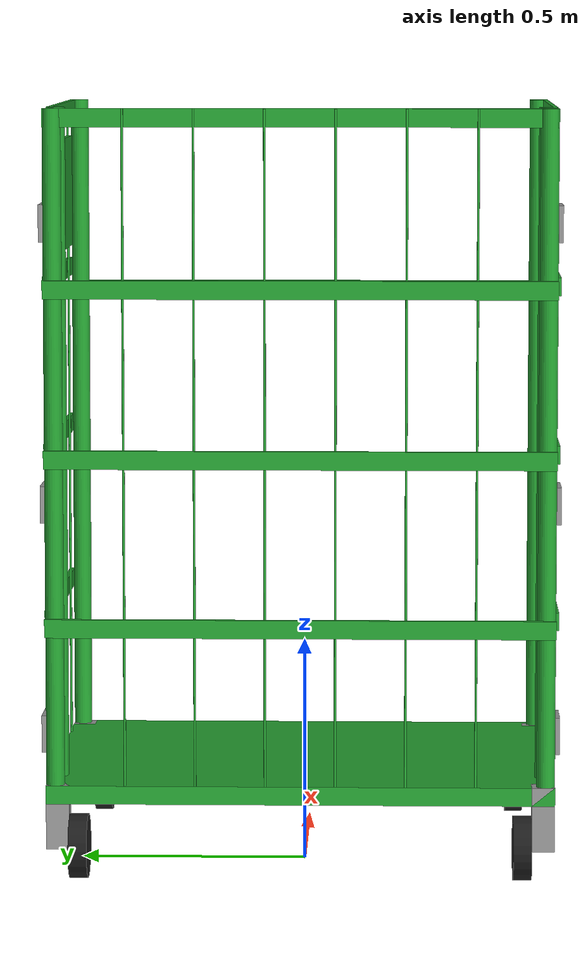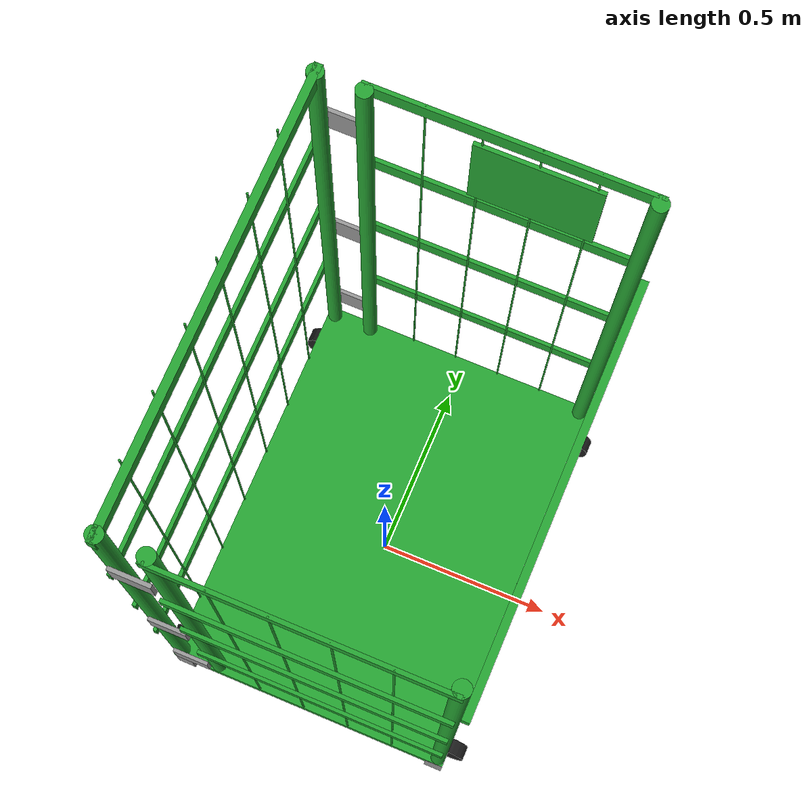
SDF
<?xml version='1.0'?>
<sdf version='1.6'>
  <model name='warehouse_trolley_final'>
    <link name='link_0'>
      <pose frame=''>0 0 0.22 0 -0 0</pose>
      <inertial>
        <mass>1</mass>
        <inertia>
          <ixx>0.166667</ixx>
          <ixy>0</ixy>
          <ixz>0</ixz>
          <iyy>0.166667</iyy>
          <iyz>0</iyz>
          <izz>0.166667</izz>
        </inertia>
        <pose frame=''>0 0 0 0 -0 0</pose>
      </inertial>
      <self_collide>0</self_collide>
      <kinematic>0</kinematic>
      <gravity>1</gravity>
      <visual name='visual'>
        <pose frame=''>0 0 0 0 -0 0</pose>
        <geometry>
          <box>
            <size>0.8 1.1 0.04</size>
          </box>
        </geometry>
        <material>
          <lighting>1</lighting>
          <script>
            <uri>file://media/materials/scripts/gazebo.material</uri>
            <name>Gazebo/Green</name>
          </script>
          <ambient>0 0.4 0 0</ambient>
          <diffuse>0 0.4 0 0</diffuse>
          <specular>0.1 0.1 0.1 1</specular>
          <emissive>0 0 0 1</emissive>
          <shader type='vertex'>
            <normal_map>__default__</normal_map>
          </shader>
        </material>
        <cast_shadows>1</cast_shadows>
        <transparency>0</transparency>
      </visual>
      <collision name='collision'>
        <laser_retro>0</laser_retro>
        <max_contacts>10</max_contacts>
        <pose frame=''>0 0 0 0 -0 0</pose>
        <geometry>
          <box>
            <size>0.8 1.1 0.04</size>
          </box>
        </geometry>
        <surface>
          <friction>
            <ode>
              <mu>1</mu>
              <mu2>1</mu2>
              <fdir1>0 0 0</fdir1>
              <slip1>0</slip1>
              <slip2>0</slip2>
            </ode>
            <torsional>
              <coefficient>1</coefficient>
              <patch_radius>0</patch_radius>
              <surface_radius>0</surface_radius>
              <use_patch_radius>1</use_patch_radius>
              <ode>
                <slip>0</slip>
              </ode>
            </torsional>
          </friction>
          <bounce>
            <restitution_coefficient>0</restitution_coefficient>
            <threshold>1e+06</threshold>
          </bounce>
          <contact>
            <collide_without_contact>0</collide_without_contact>
            <collide_without_contact_bitmask>1</collide_without_contact_bitmask>
            <collide_bitmask>1</collide_bitmask>
            <ode>
              <soft_cfm>0</soft_cfm>
              <soft_erp>0.2</soft_erp>
              <kp>1e+13</kp>
              <kd>1</kd>
              <max_vel>0.01</max_vel>
              <min_depth>0</min_depth>
            </ode>
            <bullet>
              <split_impulse>1</split_impulse>
              <split_impulse_penetration_threshold>-0.01</split_impulse_penetration_threshold>
              <soft_cfm>0</soft_cfm>
              <soft_erp>0.2</soft_erp>
              <kp>1e+13</kp>
              <kd>1</kd>
            </bullet>
          </contact>
        </surface>
      </collision>
    </link>
    <link name='link_0_0'>
      <pose frame=''>-0.375 -0.525 0.17 0 -0 0</pose>
      <inertial>
        <mass>1</mass>
        <inertia>
          <ixx>0.166667</ixx>
          <ixy>0</ixy>
          <ixz>0</ixz>
          <iyy>0.166667</iyy>
          <iyz>0</iyz>
          <izz>0.166667</izz>
        </inertia>
        <pose frame=''>0 0 0 0 -0 0</pose>
      </inertial>
      <self_collide>0</self_collide>
      <kinematic>0</kinematic>
      <visual name='visual'>
        <pose frame=''>0 0 0 0 -0 0</pose>
        <geometry>
          <box>
            <size>0.05 0.05 0.14</size>
          </box>
        </geometry>
        <material>
          <lighting>1</lighting>
          <script>
            <uri>file://media/materials/scripts/gazebo.material</uri>
            <name>Gazebo/Grey</name>
          </script>
          <ambient>0.3 0.3 0.3 1</ambient>
          <diffuse>0.7 0.7 0.7 1</diffuse>
          <specular>0.01 0.01 0.01 1</specular>
          <emissive>0 0 0 1</emissive>
          <shader type='vertex'>
            <normal_map>__default__</normal_map>
          </shader>
        </material>
        <cast_shadows>1</cast_shadows>
        <transparency>0</transparency>
      </visual>
      <collision name='collision'>
        <laser_retro>0</laser_retro>
        <max_contacts>10</max_contacts>
        <pose frame=''>0 0 0 0 -0 0</pose>
        <geometry>
          <box>
            <size>0.05 0.05 0.14</size>
          </box>
        </geometry>
        <surface>
          <friction>
            <ode>
              <mu>1</mu>
              <mu2>1</mu2>
              <fdir1>0 0 0</fdir1>
              <slip1>0</slip1>
              <slip2>0</slip2>
            </ode>
            <torsional>
              <coefficient>1</coefficient>
              <patch_radius>0</patch_radius>
              <surface_radius>0</surface_radius>
              <use_patch_radius>1</use_patch_radius>
              <ode>
                <slip>0</slip>
              </ode>
            </torsional>
          </friction>
          <bounce>
            <restitution_coefficient>0</restitution_coefficient>
            <threshold>1e+06</threshold>
          </bounce>
          <contact>
            <collide_without_contact>0</collide_without_contact>
            <collide_without_contact_bitmask>1</collide_without_contact_bitmask>
            <collide_bitmask>1</collide_bitmask>
            <ode>
              <soft_cfm>0</soft_cfm>
              <soft_erp>0.2</soft_erp>
              <kp>1e+13</kp>
              <kd>1</kd>
              <max_vel>0.01</max_vel>
              <min_depth>0</min_depth>
            </ode>
            <bullet>
              <split_impulse>1</split_impulse>
              <split_impulse_penetration_threshold>-0.01</split_impulse_penetration_threshold>
              <soft_cfm>0</soft_cfm>
              <soft_erp>0.2</soft_erp>
              <kp>1e+13</kp>
              <kd>1</kd>
            </bullet>
          </contact>
        </surface>
      </collision>
    </link>
    <link name='link_0_0_clone'>
      <pose frame=''>0.375 -0.525 0.17 0 -0 0</pose>
      <inertial>
        <mass>1</mass>
        <inertia>
          <ixx>0.166667</ixx>
          <ixy>0</ixy>
          <ixz>0</ixz>
          <iyy>0.166667</iyy>
          <iyz>0</iyz>
          <izz>0.166667</izz>
        </inertia>
        <pose frame=''>0 0 0 0 -0 0</pose>
      </inertial>
      <self_collide>0</self_collide>
      <kinematic>0</kinematic>
      <visual name='visual_0'>
        <pose frame=''>0 0 0 0 -0 0</pose>
        <geometry>
          <box>
            <size>0.05 0.05 0.14</size>
          </box>
        </geometry>
        <material>
          <lighting>1</lighting>
          <script>
            <uri>file://media/materials/scripts/gazebo.material</uri>
            <name>Gazebo/Grey</name>
          </script>
          <ambient>0.3 0.3 0.3 1</ambient>
          <diffuse>0.7 0.7 0.7 1</diffuse>
          <specular>0.01 0.01 0.01 1</specular>
          <emissive>0 0 0 1</emissive>
          <shader type='vertex'>
            <normal_map>__default__</normal_map>
          </shader>
        </material>
        <cast_shadows>1</cast_shadows>
        <transparency>0</transparency>
      </visual>
      <collision name='collision'>
        <laser_retro>0</laser_retro>
        <max_contacts>10</max_contacts>
        <pose frame=''>0 0 0 0 -0 0</pose>
        <geometry>
          <box>
            <size>0.05 0.05 0.14</size>
          </box>
        </geometry>
        <surface>
          <friction>
            <ode>
              <mu>1</mu>
              <mu2>1</mu2>
              <fdir1>0 0 0</fdir1>
              <slip1>0</slip1>
              <slip2>0</slip2>
            </ode>
            <torsional>
              <coefficient>1</coefficient>
              <patch_radius>0</patch_radius>
              <surface_radius>0</surface_radius>
              <use_patch_radius>1</use_patch_radius>
              <ode>
                <slip>0</slip>
              </ode>
            </torsional>
          </friction>
          <bounce>
            <restitution_coefficient>0</restitution_coefficient>
            <threshold>1e+06</threshold>
          </bounce>
          <contact>
            <collide_without_contact>0</collide_without_contact>
            <collide_without_contact_bitmask>1</collide_without_contact_bitmask>
            <collide_bitmask>1</collide_bitmask>
            <ode>
              <soft_cfm>0</soft_cfm>
              <soft_erp>0.2</soft_erp>
              <kp>1e+13</kp>
              <kd>1</kd>
              <max_vel>0.01</max_vel>
              <min_depth>0</min_depth>
            </ode>
            <bullet>
              <split_impulse>1</split_impulse>
              <split_impulse_penetration_threshold>-0.01</split_impulse_penetration_threshold>
              <soft_cfm>0</soft_cfm>
              <soft_erp>0.2</soft_erp>
              <kp>1e+13</kp>
              <kd>1</kd>
            </bullet>
          </contact>
        </surface>
      </collision>
    </link>
    <link name='link_0_0_clone_0'>
      <pose frame=''>-0.375 0.525 0.17 0 -0 0</pose>
      <inertial>
        <mass>1</mass>
        <inertia>
          <ixx>0.166667</ixx>
          <ixy>0</ixy>
          <ixz>0</ixz>
          <iyy>0.166667</iyy>
          <iyz>0</iyz>
          <izz>0.166667</izz>
        </inertia>
        <pose frame=''>0 0 0 0 -0 0</pose>
      </inertial>
      <self_collide>0</self_collide>
      <kinematic>0</kinematic>
      <visual name='visual_0'>
        <pose frame=''>0 0 0 0 -0 0</pose>
        <geometry>
          <box>
            <size>0.05 0.05 0.14</size>
          </box>
        </geometry>
        <material>
          <lighting>1</lighting>
          <script>
            <uri>file://media/materials/scripts/gazebo.material</uri>
            <name>Gazebo/Grey</name>
          </script>
          <ambient>0.3 0.3 0.3 1</ambient>
          <diffuse>0.7 0.7 0.7 1</diffuse>
          <specular>0.01 0.01 0.01 1</specular>
          <emissive>0 0 0 1</emissive>
          <shader type='vertex'>
            <normal_map>__default__</normal_map>
          </shader>
        </material>
        <cast_shadows>1</cast_shadows>
        <transparency>0</transparency>
      </visual>
      <collision name='collision'>
        <laser_retro>0</laser_retro>
        <max_contacts>10</max_contacts>
        <pose frame=''>0 0 0 0 -0 0</pose>
        <geometry>
          <box>
            <size>0.05 0.05 0.14</size>
          </box>
        </geometry>
        <surface>
          <friction>
            <ode>
              <mu>1</mu>
              <mu2>1</mu2>
              <fdir1>0 0 0</fdir1>
              <slip1>0</slip1>
              <slip2>0</slip2>
            </ode>
            <torsional>
              <coefficient>1</coefficient>
              <patch_radius>0</patch_radius>
              <surface_radius>0</surface_radius>
              <use_patch_radius>1</use_patch_radius>
              <ode>
                <slip>0</slip>
              </ode>
            </torsional>
          </friction>
          <bounce>
            <restitution_coefficient>0</restitution_coefficient>
            <threshold>1e+06</threshold>
          </bounce>
          <contact>
            <collide_without_contact>0</collide_without_contact>
            <collide_without_contact_bitmask>1</collide_without_contact_bitmask>
            <collide_bitmask>1</collide_bitmask>
            <ode>
              <soft_cfm>0</soft_cfm>
              <soft_erp>0.2</soft_erp>
              <kp>1e+13</kp>
              <kd>1</kd>
              <max_vel>0.01</max_vel>
              <min_depth>0</min_depth>
            </ode>
            <bullet>
              <split_impulse>1</split_impulse>
              <split_impulse_penetration_threshold>-0.01</split_impulse_penetration_threshold>
              <soft_cfm>0</soft_cfm>
              <soft_erp>0.2</soft_erp>
              <kp>1e+13</kp>
              <kd>1</kd>
            </bullet>
          </contact>
        </surface>
      </collision>
    </link>
    <link name='link_0_0_clone_0_clone'>
      <pose frame=''>-0.328097 0.555 0.35 0 -0 0</pose>
      <inertial>
        <mass>1</mass>
        <inertia>
          <ixx>0.166667</ixx>
          <ixy>0</ixy>
          <ixz>0</ixz>
          <iyy>0.166667</iyy>
          <iyz>0</iyz>
          <izz>0.166667</izz>
        </inertia>
        <pose frame=''>0 0 0 0 -0 0</pose>
      </inertial>
      <self_collide>0</self_collide>
      <kinematic>0</kinematic>
      <gravity>1</gravity>
      <visual name='visual_0'>
        <pose frame=''>0 0 0 0 -0 0</pose>
        <geometry>
          <box>
            <size>0.1 0.01 0.08</size>
          </box>
        </geometry>
        <material>
          <lighting>1</lighting>
          <script>
            <uri>file://media/materials/scripts/gazebo.material</uri>
            <name>Gazebo/Grey</name>
          </script>
          <ambient>0.3 0.3 0.3 1</ambient>
          <diffuse>0.7 0.7 0.7 1</diffuse>
          <specular>0.01 0.01 0.01 1</specular>
          <emissive>0 0 0 1</emissive>
          <shader type='vertex'>
            <normal_map>__default__</normal_map>
          </shader>
        </material>
        <cast_shadows>1</cast_shadows>
        <transparency>0</transparency>
      </visual>
      <collision name='collision'>
        <laser_retro>0</laser_retro>
        <max_contacts>10</max_contacts>
        <pose frame=''>0 0 0 0 -0 0</pose>
        <geometry>
          <box>
            <size>0.1 0.01 0.08</size>
          </box>
        </geometry>
        <surface>
          <friction>
            <ode>
              <mu>1</mu>
              <mu2>1</mu2>
              <fdir1>0 0 0</fdir1>
              <slip1>0</slip1>
              <slip2>0</slip2>
            </ode>
            <torsional>
              <coefficient>1</coefficient>
              <patch_radius>0</patch_radius>
              <surface_radius>0</surface_radius>
              <use_patch_radius>1</use_patch_radius>
              <ode>
                <slip>0</slip>
              </ode>
            </torsional>
          </friction>
          <bounce>
            <restitution_coefficient>0</restitution_coefficient>
            <threshold>1e+06</threshold>
          </bounce>
          <contact>
            <collide_without_contact>0</collide_without_contact>
            <collide_without_contact_bitmask>1</collide_without_contact_bitmask>
            <collide_bitmask>1</collide_bitmask>
            <ode>
              <soft_cfm>0</soft_cfm>
              <soft_erp>0.2</soft_erp>
              <kp>1e+13</kp>
              <kd>1</kd>
              <max_vel>0.01</max_vel>
              <min_depth>0</min_depth>
            </ode>
            <bullet>
              <split_impulse>1</split_impulse>
              <split_impulse_penetration_threshold>-0.01</split_impulse_penetration_threshold>
              <soft_cfm>0</soft_cfm>
              <soft_erp>0.2</soft_erp>
              <kp>1e+13</kp>
              <kd>1</kd>
            </bullet>
          </contact>
        </surface>
      </collision>
    </link>
    <link name='link_0_0_clone_0_clone_clone'>
      <pose frame=''>-0.328097 0.555 0.85 0 -0 0</pose>
      <inertial>
        <mass>1</mass>
        <inertia>
          <ixx>0.166667</ixx>
          <ixy>0</ixy>
          <ixz>0</ixz>
          <iyy>0.166667</iyy>
          <iyz>0</iyz>
          <izz>0.166667</izz>
        </inertia>
        <pose frame=''>0 0 0 0 -0 0</pose>
      </inertial>
      <self_collide>0</self_collide>
      <kinematic>0</kinematic>
      <gravity>1</gravity>
      <visual name='visual_0'>
        <pose frame=''>0 0 0 0 -0 0</pose>
        <geometry>
          <box>
            <size>0.1 0.01 0.08</size>
          </box>
        </geometry>
        <material>
          <lighting>1</lighting>
          <script>
            <uri>file://media/materials/scripts/gazebo.material</uri>
            <name>Gazebo/Grey</name>
          </script>
          <ambient>0.3 0.3 0.3 1</ambient>
          <diffuse>0.7 0.7 0.7 1</diffuse>
          <specular>0.01 0.01 0.01 1</specular>
          <emissive>0 0 0 1</emissive>
          <shader type='vertex'>
            <normal_map>__default__</normal_map>
          </shader>
        </material>
        <cast_shadows>1</cast_shadows>
        <transparency>0</transparency>
      </visual>
      <collision name='collision'>
        <laser_retro>0</laser_retro>
        <max_contacts>10</max_contacts>
        <pose frame=''>0 0 0 0 -0 0</pose>
        <geometry>
          <box>
            <size>0.1 0.01 0.08</size>
          </box>
        </geometry>
        <surface>
          <friction>
            <ode>
              <mu>1</mu>
              <mu2>1</mu2>
              <fdir1>0 0 0</fdir1>
              <slip1>0</slip1>
              <slip2>0</slip2>
            </ode>
            <torsional>
              <coefficient>1</coefficient>
              <patch_radius>0</patch_radius>
              <surface_radius>0</surface_radius>
              <use_patch_radius>1</use_patch_radius>
              <ode>
                <slip>0</slip>
              </ode>
            </torsional>
          </friction>
          <bounce>
            <restitution_coefficient>0</restitution_coefficient>
            <threshold>1e+06</threshold>
          </bounce>
          <contact>
            <collide_without_contact>0</collide_without_contact>
            <collide_without_contact_bitmask>1</collide_without_contact_bitmask>
            <collide_bitmask>1</collide_bitmask>
            <ode>
              <soft_cfm>0</soft_cfm>
              <soft_erp>0.2</soft_erp>
              <kp>1e+13</kp>
              <kd>1</kd>
              <max_vel>0.01</max_vel>
              <min_depth>0</min_depth>
            </ode>
            <bullet>
              <split_impulse>1</split_impulse>
              <split_impulse_penetration_threshold>-0.01</split_impulse_penetration_threshold>
              <soft_cfm>0</soft_cfm>
              <soft_erp>0.2</soft_erp>
              <kp>1e+13</kp>
              <kd>1</kd>
            </bullet>
          </contact>
        </surface>
      </collision>
    </link>
    <link name='link_0_0_clone_0_clone_clone_0'>
      <pose frame=''>-0.328097 0.555 1.455 0 -0 0</pose>
      <inertial>
        <mass>1</mass>
        <inertia>
          <ixx>0.166667</ixx>
          <ixy>0</ixy>
          <ixz>0</ixz>
          <iyy>0.166667</iyy>
          <iyz>0</iyz>
          <izz>0.166667</izz>
        </inertia>
        <pose frame=''>0 0 0 0 -0 0</pose>
      </inertial>
      <self_collide>0</self_collide>
      <kinematic>0</kinematic>
      <gravity>1</gravity>
      <visual name='visual_0'>
        <pose frame=''>0 0 0 0 -0 0</pose>
        <geometry>
          <box>
            <size>0.1 0.01 0.08</size>
          </box>
        </geometry>
        <material>
          <lighting>1</lighting>
          <script>
            <uri>file://media/materials/scripts/gazebo.material</uri>
            <name>Gazebo/Grey</name>
          </script>
          <ambient>0.3 0.3 0.3 1</ambient>
          <diffuse>0.7 0.7 0.7 1</diffuse>
          <specular>0.01 0.01 0.01 1</specular>
          <emissive>0 0 0 1</emissive>
          <shader type='vertex'>
            <normal_map>__default__</normal_map>
          </shader>
        </material>
        <cast_shadows>1</cast_shadows>
        <transparency>0</transparency>
      </visual>
      <collision name='collision'>
        <laser_retro>0</laser_retro>
        <max_contacts>10</max_contacts>
        <pose frame=''>0 0 0 0 -0 0</pose>
        <geometry>
          <box>
            <size>0.1 0.01 0.08</size>
          </box>
        </geometry>
        <surface>
          <friction>
            <ode>
              <mu>1</mu>
              <mu2>1</mu2>
              <fdir1>0 0 0</fdir1>
              <slip1>0</slip1>
              <slip2>0</slip2>
            </ode>
            <torsional>
              <coefficient>1</coefficient>
              <patch_radius>0</patch_radius>
              <surface_radius>0</surface_radius>
              <use_patch_radius>1</use_patch_radius>
              <ode>
                <slip>0</slip>
              </ode>
            </torsional>
          </friction>
          <bounce>
            <restitution_coefficient>0</restitution_coefficient>
            <threshold>1e+06</threshold>
          </bounce>
          <contact>
            <collide_without_contact>0</collide_without_contact>
            <collide_without_contact_bitmask>1</collide_without_contact_bitmask>
            <collide_bitmask>1</collide_bitmask>
            <ode>
              <soft_cfm>0</soft_cfm>
              <soft_erp>0.2</soft_erp>
              <kp>1e+13</kp>
              <kd>1</kd>
              <max_vel>0.01</max_vel>
              <min_depth>0</min_depth>
            </ode>
            <bullet>
              <split_impulse>1</split_impulse>
              <split_impulse_penetration_threshold>-0.01</split_impulse_penetration_threshold>
              <soft_cfm>0</soft_cfm>
              <soft_erp>0.2</soft_erp>
              <kp>1e+13</kp>
              <kd>1</kd>
            </bullet>
          </contact>
        </surface>
      </collision>
    </link>
    <link name='link_0_0_clone_0_clone_clone_2'>
      <pose frame=''>-0.328097 -0.555 1.455 0 -0 0</pose>
      <inertial>
        <mass>1</mass>
        <inertia>
          <ixx>0.166667</ixx>
          <ixy>0</ixy>
          <ixz>0</ixz>
          <iyy>0.166667</iyy>
          <iyz>0</iyz>
          <izz>0.166667</izz>
        </inertia>
        <pose frame=''>0 0 0 0 -0 0</pose>
      </inertial>
      <self_collide>0</self_collide>
      <kinematic>0</kinematic>
      <gravity>1</gravity>
      <visual name='visual_0'>
        <pose frame=''>0 0 0 0 -0 0</pose>
        <geometry>
          <box>
            <size>0.1 0.01 0.08</size>
          </box>
        </geometry>
        <material>
          <lighting>1</lighting>
          <script>
            <uri>file://media/materials/scripts/gazebo.material</uri>
            <name>Gazebo/Grey</name>
          </script>
          <ambient>0.3 0.3 0.3 1</ambient>
          <diffuse>0.7 0.7 0.7 1</diffuse>
          <specular>0.01 0.01 0.01 1</specular>
          <emissive>0 0 0 1</emissive>
          <shader type='vertex'>
            <normal_map>__default__</normal_map>
          </shader>
        </material>
        <cast_shadows>1</cast_shadows>
        <transparency>0</transparency>
      </visual>
      <collision name='collision'>
        <laser_retro>0</laser_retro>
        <max_contacts>10</max_contacts>
        <pose frame=''>0 0 0 0 -0 0</pose>
        <geometry>
          <box>
            <size>0.1 0.01 0.08</size>
          </box>
        </geometry>
        <surface>
          <friction>
            <ode>
              <mu>1</mu>
              <mu2>1</mu2>
              <fdir1>0 0 0</fdir1>
              <slip1>0</slip1>
              <slip2>0</slip2>
            </ode>
            <torsional>
              <coefficient>1</coefficient>
              <patch_radius>0</patch_radius>
              <surface_radius>0</surface_radius>
              <use_patch_radius>1</use_patch_radius>
              <ode>
                <slip>0</slip>
              </ode>
            </torsional>
          </friction>
          <bounce>
            <restitution_coefficient>0</restitution_coefficient>
            <threshold>1e+06</threshold>
          </bounce>
          <contact>
            <collide_without_contact>0</collide_without_contact>
            <collide_without_contact_bitmask>1</collide_without_contact_bitmask>
            <collide_bitmask>1</collide_bitmask>
            <ode>
              <soft_cfm>0</soft_cfm>
              <soft_erp>0.2</soft_erp>
              <kp>1e+13</kp>
              <kd>1</kd>
              <max_vel>0.01</max_vel>
              <min_depth>0</min_depth>
            </ode>
            <bullet>
              <split_impulse>1</split_impulse>
              <split_impulse_penetration_threshold>-0.01</split_impulse_penetration_threshold>
              <soft_cfm>0</soft_cfm>
              <soft_erp>0.2</soft_erp>
              <kp>1e+13</kp>
              <kd>1</kd>
            </bullet>
          </contact>
        </surface>
      </collision>
    </link>
    <link name='link_0_0_clone_0_clone_clone_2_clone'>
      <pose frame=''>-0.328097 -0.555 0.35 0 -0 0</pose>
      <inertial>
        <mass>1</mass>
        <inertia>
          <ixx>0.166667</ixx>
          <ixy>0</ixy>
          <ixz>0</ixz>
          <iyy>0.166667</iyy>
          <iyz>0</iyz>
          <izz>0.166667</izz>
        </inertia>
        <pose frame=''>0 0 0 0 -0 0</pose>
      </inertial>
      <self_collide>0</self_collide>
      <kinematic>0</kinematic>
      <gravity>1</gravity>
      <visual name='visual_0'>
        <pose frame=''>0 0 0 0 -0 0</pose>
        <geometry>
          <box>
            <size>0.1 0.01 0.08</size>
          </box>
        </geometry>
        <material>
          <lighting>1</lighting>
          <script>
            <uri>file://media/materials/scripts/gazebo.material</uri>
            <name>Gazebo/Grey</name>
          </script>
          <ambient>0.3 0.3 0.3 1</ambient>
          <diffuse>0.7 0.7 0.7 1</diffuse>
          <specular>0.01 0.01 0.01 1</specular>
          <emissive>0 0 0 1</emissive>
          <shader type='vertex'>
            <normal_map>__default__</normal_map>
          </shader>
        </material>
        <cast_shadows>1</cast_shadows>
        <transparency>0</transparency>
      </visual>
      <collision name='collision'>
        <laser_retro>0</laser_retro>
        <max_contacts>10</max_contacts>
        <pose frame=''>0 0 0 0 -0 0</pose>
        <geometry>
          <box>
            <size>0.1 0.01 0.08</size>
          </box>
        </geometry>
        <surface>
          <friction>
            <ode>
              <mu>1</mu>
              <mu2>1</mu2>
              <fdir1>0 0 0</fdir1>
              <slip1>0</slip1>
              <slip2>0</slip2>
            </ode>
            <torsional>
              <coefficient>1</coefficient>
              <patch_radius>0</patch_radius>
              <surface_radius>0</surface_radius>
              <use_patch_radius>1</use_patch_radius>
              <ode>
                <slip>0</slip>
              </ode>
            </torsional>
          </friction>
          <bounce>
            <restitution_coefficient>0</restitution_coefficient>
            <threshold>1e+06</threshold>
          </bounce>
          <contact>
            <collide_without_contact>0</collide_without_contact>
            <collide_without_contact_bitmask>1</collide_without_contact_bitmask>
            <collide_bitmask>1</collide_bitmask>
            <ode>
              <soft_cfm>0</soft_cfm>
              <soft_erp>0.2</soft_erp>
              <kp>1e+13</kp>
              <kd>1</kd>
              <max_vel>0.01</max_vel>
              <min_depth>0</min_depth>
            </ode>
            <bullet>
              <split_impulse>1</split_impulse>
              <split_impulse_penetration_threshold>-0.01</split_impulse_penetration_threshold>
              <soft_cfm>0</soft_cfm>
              <soft_erp>0.2</soft_erp>
              <kp>1e+13</kp>
              <kd>1</kd>
            </bullet>
          </contact>
        </surface>
      </collision>
    </link>
    <link name='link_0_0_clone_0_clone_clone_3'>
      <pose frame=''>-0.328097 -0.555 0.85 0 -0 0</pose>
      <inertial>
        <mass>1</mass>
        <inertia>
          <ixx>0.166667</ixx>
          <ixy>0</ixy>
          <ixz>0</ixz>
          <iyy>0.166667</iyy>
          <iyz>0</iyz>
          <izz>0.166667</izz>
        </inertia>
        <pose frame=''>0 0 0 0 -0 0</pose>
      </inertial>
      <self_collide>0</self_collide>
      <kinematic>0</kinematic>
      <gravity>1</gravity>
      <visual name='visual_0'>
        <pose frame=''>0 0 0 0 -0 0</pose>
        <geometry>
          <box>
            <size>0.1 0.01 0.08</size>
          </box>
        </geometry>
        <material>
          <lighting>1</lighting>
          <script>
            <uri>file://media/materials/scripts/gazebo.material</uri>
            <name>Gazebo/Grey</name>
          </script>
          <ambient>0.3 0.3 0.3 1</ambient>
          <diffuse>0.7 0.7 0.7 1</diffuse>
          <specular>0.01 0.01 0.01 1</specular>
          <emissive>0 0 0 1</emissive>
          <shader type='vertex'>
            <normal_map>__default__</normal_map>
          </shader>
        </material>
        <cast_shadows>1</cast_shadows>
        <transparency>0</transparency>
      </visual>
      <collision name='collision'>
        <laser_retro>0</laser_retro>
        <max_contacts>10</max_contacts>
        <pose frame=''>0 0 0 0 -0 0</pose>
        <geometry>
          <box>
            <size>0.1 0.01 0.08</size>
          </box>
        </geometry>
        <surface>
          <friction>
            <ode>
              <mu>1</mu>
              <mu2>1</mu2>
              <fdir1>0 0 0</fdir1>
              <slip1>0</slip1>
              <slip2>0</slip2>
            </ode>
            <torsional>
              <coefficient>1</coefficient>
              <patch_radius>0</patch_radius>
              <surface_radius>0</surface_radius>
              <use_patch_radius>1</use_patch_radius>
              <ode>
                <slip>0</slip>
              </ode>
            </torsional>
          </friction>
          <bounce>
            <restitution_coefficient>0</restitution_coefficient>
            <threshold>1e+06</threshold>
          </bounce>
          <contact>
            <collide_without_contact>0</collide_without_contact>
            <collide_without_contact_bitmask>1</collide_without_contact_bitmask>
            <collide_bitmask>1</collide_bitmask>
            <ode>
              <soft_cfm>0</soft_cfm>
              <soft_erp>0.2</soft_erp>
              <kp>1e+13</kp>
              <kd>1</kd>
              <max_vel>0.01</max_vel>
              <min_depth>0</min_depth>
            </ode>
            <bullet>
              <split_impulse>1</split_impulse>
              <split_impulse_penetration_threshold>-0.01</split_impulse_penetration_threshold>
              <soft_cfm>0</soft_cfm>
              <soft_erp>0.2</soft_erp>
              <kp>1e+13</kp>
              <kd>1</kd>
            </bullet>
          </contact>
        </surface>
      </collision>
    </link>
    <link name='link_0_0_clone_1'>
      <pose frame=''>0.375 0.525 0.17 0 -0 0</pose>
      <inertial>
        <mass>1</mass>
        <inertia>
          <ixx>0.166667</ixx>
          <ixy>0</ixy>
          <ixz>0</ixz>
          <iyy>0.166667</iyy>
          <iyz>0</iyz>
          <izz>0.166667</izz>
        </inertia>
        <pose frame=''>0 0 0 0 -0 0</pose>
      </inertial>
      <self_collide>0</self_collide>
      <kinematic>0</kinematic>
      <visual name='visual_0'>
        <pose frame=''>0 0 0 0 -0 0</pose>
        <geometry>
          <box>
            <size>0.05 0.05 0.14</size>
          </box>
        </geometry>
        <material>
          <lighting>1</lighting>
          <script>
            <uri>file://media/materials/scripts/gazebo.material</uri>
            <name>Gazebo/Grey</name>
          </script>
          <ambient>0.3 0.3 0.3 1</ambient>
          <diffuse>0.7 0.7 0.7 1</diffuse>
          <specular>0.01 0.01 0.01 1</specular>
          <emissive>0 0 0 1</emissive>
          <shader type='vertex'>
            <normal_map>__default__</normal_map>
          </shader>
        </material>
        <cast_shadows>1</cast_shadows>
        <transparency>0</transparency>
      </visual>
      <collision name='collision'>
        <laser_retro>0</laser_retro>
        <max_contacts>10</max_contacts>
        <pose frame=''>0 0 0 0 -0 0</pose>
        <geometry>
          <box>
            <size>0.05 0.05 0.14</size>
          </box>
        </geometry>
        <surface>
          <friction>
            <ode>
              <mu>1</mu>
              <mu2>1</mu2>
              <fdir1>0 0 0</fdir1>
              <slip1>0</slip1>
              <slip2>0</slip2>
            </ode>
            <torsional>
              <coefficient>1</coefficient>
              <patch_radius>0</patch_radius>
              <surface_radius>0</surface_radius>
              <use_patch_radius>1</use_patch_radius>
              <ode>
                <slip>0</slip>
              </ode>
            </torsional>
          </friction>
          <bounce>
            <restitution_coefficient>0</restitution_coefficient>
            <threshold>1e+06</threshold>
          </bounce>
          <contact>
            <collide_without_contact>0</collide_without_contact>
            <collide_without_contact_bitmask>1</collide_without_contact_bitmask>
            <collide_bitmask>1</collide_bitmask>
            <ode>
              <soft_cfm>0</soft_cfm>
              <soft_erp>0.2</soft_erp>
              <kp>1e+13</kp>
              <kd>1</kd>
              <max_vel>0.01</max_vel>
              <min_depth>0</min_depth>
            </ode>
            <bullet>
              <split_impulse>1</split_impulse>
              <split_impulse_penetration_threshold>-0.01</split_impulse_penetration_threshold>
              <soft_cfm>0</soft_cfm>
              <soft_erp>0.2</soft_erp>
              <kp>1e+13</kp>
              <kd>1</kd>
            </bullet>
          </contact>
        </surface>
      </collision>
    </link>
    <link name='link_0_1'>
      <pose frame=''>0.38 -0.53 0.95 0 -0 0</pose>
      <inertial>
        <mass>1</mass>
        <inertia>
          <ixx>0.145833</ixx>
          <ixy>0</ixy>
          <ixz>0</ixz>
          <iyy>0.145833</iyy>
          <iyz>0</iyz>
          <izz>0.125</izz>
        </inertia>
        <pose frame=''>0 0 0 0 -0 0</pose>
      </inertial>
      <self_collide>0</self_collide>
      <kinematic>0</kinematic>
      <visual name='visual'>
        <pose frame=''>0 0 0 0 -0 0</pose>
        <geometry>
          <cylinder>
            <radius>0.02</radius>
            <length>1.5</length>
          </cylinder>
        </geometry>
        <material>
          <lighting>1</lighting>
          <script>
            <uri>file://media/materials/scripts/gazebo.material</uri>
            <name>Gazebo/Green</name>
          </script>
          <ambient>0 0.4 0 0</ambient>
          <diffuse>0 0.4 0 0</diffuse>
          <specular>0.1 0.1 0.1 1</specular>
          <emissive>0 0 0 1</emissive>
          <shader type='vertex'>
            <normal_map>__default__</normal_map>
          </shader>
        </material>
        <cast_shadows>1</cast_shadows>
        <transparency>0</transparency>
      </visual>
      <collision name='collision'>
        <laser_retro>0</laser_retro>
        <max_contacts>10</max_contacts>
        <pose frame=''>0 0 0 0 -0 0</pose>
        <geometry>
          <cylinder>
            <radius>0.02</radius>
            <length>1.5</length>
          </cylinder>
        </geometry>
        <surface>
          <friction>
            <ode>
              <mu>1</mu>
              <mu2>1</mu2>
              <fdir1>0 0 0</fdir1>
              <slip1>0</slip1>
              <slip2>0</slip2>
            </ode>
            <torsional>
              <coefficient>1</coefficient>
              <patch_radius>0</patch_radius>
              <surface_radius>0</surface_radius>
              <use_patch_radius>1</use_patch_radius>
              <ode>
                <slip>0</slip>
              </ode>
            </torsional>
          </friction>
          <bounce>
            <restitution_coefficient>0</restitution_coefficient>
            <threshold>1e+06</threshold>
          </bounce>
          <contact>
            <collide_without_contact>0</collide_without_contact>
            <collide_without_contact_bitmask>1</collide_without_contact_bitmask>
            <collide_bitmask>1</collide_bitmask>
            <ode>
              <soft_cfm>0</soft_cfm>
              <soft_erp>0.2</soft_erp>
              <kp>1e+13</kp>
              <kd>1</kd>
              <max_vel>0.01</max_vel>
              <min_depth>0</min_depth>
            </ode>
            <bullet>
              <split_impulse>1</split_impulse>
              <split_impulse_penetration_threshold>-0.01</split_impulse_penetration_threshold>
              <soft_cfm>0</soft_cfm>
              <soft_erp>0.2</soft_erp>
              <kp>1e+13</kp>
              <kd>1</kd>
            </bullet>
          </contact>
        </surface>
      </collision>
    </link>
    <link name='link_0_1_clone'>
      <pose frame=''>-0.27 -0.53 0.95 0 -0 0</pose>
      <inertial>
        <mass>1</mass>
        <inertia>
          <ixx>0.145833</ixx>
          <ixy>0</ixy>
          <ixz>0</ixz>
          <iyy>0.145833</iyy>
          <iyz>0</iyz>
          <izz>0.125</izz>
        </inertia>
        <pose frame=''>0 0 0 0 -0 0</pose>
      </inertial>
      <self_collide>0</self_collide>
      <kinematic>0</kinematic>
      <visual name='visual'>
        <pose frame=''>0 0 0 0 -0 0</pose>
        <geometry>
          <cylinder>
            <radius>0.02</radius>
            <length>1.5</length>
          </cylinder>
        </geometry>
        <material>
          <lighting>1</lighting>
          <script>
            <uri>file://media/materials/scripts/gazebo.material</uri>
            <name>Gazebo/Green</name>
          </script>
          <ambient>0 0.4 0 0</ambient>
          <diffuse>0 0.4 0 0</diffuse>
          <specular>0.1 0.1 0.1 1</specular>
          <emissive>0 0 0 1</emissive>
          <shader type='vertex'>
            <normal_map>__default__</normal_map>
          </shader>
        </material>
        <cast_shadows>1</cast_shadows>
        <transparency>0</transparency>
      </visual>
      <collision name='collision'>
        <laser_retro>0</laser_retro>
        <max_contacts>10</max_contacts>
        <pose frame=''>0 0 0 0 -0 0</pose>
        <geometry>
          <cylinder>
            <radius>0.02</radius>
            <length>1.5</length>
          </cylinder>
        </geometry>
        <surface>
          <friction>
            <ode>
              <mu>1</mu>
              <mu2>1</mu2>
              <fdir1>0 0 0</fdir1>
              <slip1>0</slip1>
              <slip2>0</slip2>
            </ode>
            <torsional>
              <coefficient>1</coefficient>
              <patch_radius>0</patch_radius>
              <surface_radius>0</surface_radius>
              <use_patch_radius>1</use_patch_radius>
              <ode>
                <slip>0</slip>
              </ode>
            </torsional>
          </friction>
          <bounce>
            <restitution_coefficient>0</restitution_coefficient>
            <threshold>1e+06</threshold>
          </bounce>
          <contact>
            <collide_without_contact>0</collide_without_contact>
            <collide_without_contact_bitmask>1</collide_without_contact_bitmask>
            <collide_bitmask>1</collide_bitmask>
            <ode>
              <soft_cfm>0</soft_cfm>
              <soft_erp>0.2</soft_erp>
              <kp>1e+13</kp>
              <kd>1</kd>
              <max_vel>0.01</max_vel>
              <min_depth>0</min_depth>
            </ode>
            <bullet>
              <split_impulse>1</split_impulse>
              <split_impulse_penetration_threshold>-0.01</split_impulse_penetration_threshold>
              <soft_cfm>0</soft_cfm>
              <soft_erp>0.2</soft_erp>
              <kp>1e+13</kp>
              <kd>1</kd>
            </bullet>
          </contact>
        </surface>
      </collision>
    </link>
    <link name='link_0_1_clone_0'>
      <pose frame=''>-0.38 -0.53 0.95 0 -0 0</pose>
      <inertial>
        <mass>1</mass>
        <inertia>
          <ixx>0.145833</ixx>
          <ixy>0</ixy>
          <ixz>0</ixz>
          <iyy>0.145833</iyy>
          <iyz>0</iyz>
          <izz>0.125</izz>
        </inertia>
        <pose frame=''>0 0 0 0 -0 0</pose>
      </inertial>
      <self_collide>0</self_collide>
      <kinematic>0</kinematic>
      <visual name='visual'>
        <pose frame=''>0 0 0 0 -0 0</pose>
        <geometry>
          <cylinder>
            <radius>0.02</radius>
            <length>1.5</length>
          </cylinder>
        </geometry>
        <material>
          <lighting>1</lighting>
          <script>
            <uri>file://media/materials/scripts/gazebo.material</uri>
            <name>Gazebo/Green</name>
          </script>
          <ambient>0 0.4 0 0</ambient>
          <diffuse>0 0.4 0 0</diffuse>
          <specular>0.1 0.1 0.1 1</specular>
          <emissive>0 0 0 1</emissive>
          <shader type='vertex'>
            <normal_map>__default__</normal_map>
          </shader>
        </material>
        <cast_shadows>1</cast_shadows>
        <transparency>0</transparency>
      </visual>
      <collision name='collision'>
        <laser_retro>0</laser_retro>
        <max_contacts>10</max_contacts>
        <pose frame=''>0 0 0 0 -0 0</pose>
        <geometry>
          <cylinder>
            <radius>0.02</radius>
            <length>1.5</length>
          </cylinder>
        </geometry>
        <surface>
          <friction>
            <ode>
              <mu>1</mu>
              <mu2>1</mu2>
              <fdir1>0 0 0</fdir1>
              <slip1>0</slip1>
              <slip2>0</slip2>
            </ode>
            <torsional>
              <coefficient>1</coefficient>
              <patch_radius>0</patch_radius>
              <surface_radius>0</surface_radius>
              <use_patch_radius>1</use_patch_radius>
              <ode>
                <slip>0</slip>
              </ode>
            </torsional>
          </friction>
          <bounce>
            <restitution_coefficient>0</restitution_coefficient>
            <threshold>1e+06</threshold>
          </bounce>
          <contact>
            <collide_without_contact>0</collide_without_contact>
            <collide_without_contact_bitmask>1</collide_without_contact_bitmask>
            <collide_bitmask>1</collide_bitmask>
            <ode>
              <soft_cfm>0</soft_cfm>
              <soft_erp>0.2</soft_erp>
              <kp>1e+13</kp>
              <kd>1</kd>
              <max_vel>0.01</max_vel>
              <min_depth>0</min_depth>
            </ode>
            <bullet>
              <split_impulse>1</split_impulse>
              <split_impulse_penetration_threshold>-0.01</split_impulse_penetration_threshold>
              <soft_cfm>0</soft_cfm>
              <soft_erp>0.2</soft_erp>
              <kp>1e+13</kp>
              <kd>1</kd>
            </bullet>
          </contact>
        </surface>
      </collision>
    </link>
    <link name='link_0_1_clone_1'>
      <pose frame=''>-0.38 0.53 0.95 0 -0 0</pose>
      <inertial>
        <mass>1</mass>
        <inertia>
          <ixx>0.145833</ixx>
          <ixy>0</ixy>
          <ixz>0</ixz>
          <iyy>0.145833</iyy>
          <iyz>0</iyz>
          <izz>0.125</izz>
        </inertia>
        <pose frame=''>0 0 0 0 -0 0</pose>
      </inertial>
      <self_collide>0</self_collide>
      <kinematic>0</kinematic>
      <visual name='visual'>
        <pose frame=''>0 0 0 0 -0 0</pose>
        <geometry>
          <cylinder>
            <radius>0.02</radius>
            <length>1.5</length>
          </cylinder>
        </geometry>
        <material>
          <lighting>1</lighting>
          <script>
            <uri>file://media/materials/scripts/gazebo.material</uri>
            <name>Gazebo/Green</name>
          </script>
          <ambient>0 0.4 0 0</ambient>
          <diffuse>0 0.4 0 0</diffuse>
          <specular>0.1 0.1 0.1 1</specular>
          <emissive>0 0 0 1</emissive>
          <shader type='vertex'>
            <normal_map>__default__</normal_map>
          </shader>
        </material>
        <cast_shadows>1</cast_shadows>
        <transparency>0</transparency>
      </visual>
      <collision name='collision'>
        <laser_retro>0</laser_retro>
        <max_contacts>10</max_contacts>
        <pose frame=''>0 0 0 0 -0 0</pose>
        <geometry>
          <cylinder>
            <radius>0.02</radius>
            <length>1.5</length>
          </cylinder>
        </geometry>
        <surface>
          <friction>
            <ode>
              <mu>1</mu>
              <mu2>1</mu2>
              <fdir1>0 0 0</fdir1>
              <slip1>0</slip1>
              <slip2>0</slip2>
            </ode>
            <torsional>
              <coefficient>1</coefficient>
              <patch_radius>0</patch_radius>
              <surface_radius>0</surface_radius>
              <use_patch_radius>1</use_patch_radius>
              <ode>
                <slip>0</slip>
              </ode>
            </torsional>
          </friction>
          <bounce>
            <restitution_coefficient>0</restitution_coefficient>
            <threshold>1e+06</threshold>
          </bounce>
          <contact>
            <collide_without_contact>0</collide_without_contact>
            <collide_without_contact_bitmask>1</collide_without_contact_bitmask>
            <collide_bitmask>1</collide_bitmask>
            <ode>
              <soft_cfm>0</soft_cfm>
              <soft_erp>0.2</soft_erp>
              <kp>1e+13</kp>
              <kd>1</kd>
              <max_vel>0.01</max_vel>
              <min_depth>0</min_depth>
            </ode>
            <bullet>
              <split_impulse>1</split_impulse>
              <split_impulse_penetration_threshold>-0.01</split_impulse_penetration_threshold>
              <soft_cfm>0</soft_cfm>
              <soft_erp>0.2</soft_erp>
              <kp>1e+13</kp>
              <kd>1</kd>
            </bullet>
          </contact>
        </surface>
      </collision>
    </link>
    <link name='link_0_1_clone_2'>
      <pose frame=''>-0.14 -0.5475 0.95 0 -0 0</pose>
      <inertial>
        <mass>1</mass>
        <inertia>
          <ixx>0.145833</ixx>
          <ixy>0</ixy>
          <ixz>0</ixz>
          <iyy>0.145833</iyy>
          <iyz>0</iyz>
          <izz>0.125</izz>
        </inertia>
        <pose frame=''>0 0 0 0 -0 0</pose>
      </inertial>
      <self_collide>0</self_collide>
      <kinematic>0</kinematic>
      <visual name='visual'>
        <pose frame=''>0 0 0 0 -0 0</pose>
        <geometry>
          <cylinder>
            <radius>0.0025</radius>
            <length>1.5</length>
          </cylinder>
        </geometry>
        <material>
          <lighting>1</lighting>
          <script>
            <uri>file://media/materials/scripts/gazebo.material</uri>
            <name>Gazebo/Green</name>
          </script>
          <ambient>0 0.4 0 0</ambient>
          <diffuse>0 0.4 0 0</diffuse>
          <specular>0.1 0.1 0.1 1</specular>
          <emissive>0 0 0 1</emissive>
          <shader type='vertex'>
            <normal_map>__default__</normal_map>
          </shader>
        </material>
        <cast_shadows>1</cast_shadows>
        <transparency>0</transparency>
      </visual>
      <collision name='collision'>
        <laser_retro>0</laser_retro>
        <max_contacts>10</max_contacts>
        <pose frame=''>0 0 0 0 -0 0</pose>
        <geometry>
          <cylinder>
            <radius>0.0025</radius>
            <length>1.5</length>
          </cylinder>
        </geometry>
        <surface>
          <friction>
            <ode>
              <mu>1</mu>
              <mu2>1</mu2>
              <fdir1>0 0 0</fdir1>
              <slip1>0</slip1>
              <slip2>0</slip2>
            </ode>
            <torsional>
              <coefficient>1</coefficient>
              <patch_radius>0</patch_radius>
              <surface_radius>0</surface_radius>
              <use_patch_radius>1</use_patch_radius>
              <ode>
                <slip>0</slip>
              </ode>
            </torsional>
          </friction>
          <bounce>
            <restitution_coefficient>0</restitution_coefficient>
            <threshold>1e+06</threshold>
          </bounce>
          <contact>
            <collide_without_contact>0</collide_without_contact>
            <collide_without_contact_bitmask>1</collide_without_contact_bitmask>
            <collide_bitmask>1</collide_bitmask>
            <ode>
              <soft_cfm>0</soft_cfm>
              <soft_erp>0.2</soft_erp>
              <kp>1e+13</kp>
              <kd>1</kd>
              <max_vel>0.01</max_vel>
              <min_depth>0</min_depth>
            </ode>
            <bullet>
              <split_impulse>1</split_impulse>
              <split_impulse_penetration_threshold>-0.01</split_impulse_penetration_threshold>
              <soft_cfm>0</soft_cfm>
              <soft_erp>0.2</soft_erp>
              <kp>1e+13</kp>
              <kd>1</kd>
            </bullet>
          </contact>
        </surface>
      </collision>
    </link>
    <link name='link_0_1_clone_2_clone'>
      <pose frame=''>0.25 -0.5475 0.95 0 -0 0</pose>
      <inertial>
        <mass>1</mass>
        <inertia>
          <ixx>0.145833</ixx>
          <ixy>0</ixy>
          <ixz>0</ixz>
          <iyy>0.145833</iyy>
          <iyz>0</iyz>
          <izz>0.125</izz>
        </inertia>
        <pose frame=''>0 0 0 0 -0 0</pose>
      </inertial>
      <self_collide>0</self_collide>
      <kinematic>0</kinematic>
      <visual name='visual'>
        <pose frame=''>0 0 0 0 -0 0</pose>
        <geometry>
          <cylinder>
            <radius>0.0025</radius>
            <length>1.5</length>
          </cylinder>
        </geometry>
        <material>
          <lighting>1</lighting>
          <script>
            <uri>file://media/materials/scripts/gazebo.material</uri>
            <name>Gazebo/Green</name>
          </script>
          <ambient>0 0.4 0 0</ambient>
          <diffuse>0 0.4 0 0</diffuse>
          <specular>0.1 0.1 0.1 1</specular>
          <emissive>0 0 0 1</emissive>
          <shader type='vertex'>
            <normal_map>__default__</normal_map>
          </shader>
        </material>
        <cast_shadows>1</cast_shadows>
        <transparency>0</transparency>
      </visual>
      <collision name='collision'>
        <laser_retro>0</laser_retro>
        <max_contacts>10</max_contacts>
        <pose frame=''>0 0 0 0 -0 0</pose>
        <geometry>
          <cylinder>
            <radius>0.0025</radius>
            <length>1.5</length>
          </cylinder>
        </geometry>
        <surface>
          <friction>
            <ode>
              <mu>1</mu>
              <mu2>1</mu2>
              <fdir1>0 0 0</fdir1>
              <slip1>0</slip1>
              <slip2>0</slip2>
            </ode>
            <torsional>
              <coefficient>1</coefficient>
              <patch_radius>0</patch_radius>
              <surface_radius>0</surface_radius>
              <use_patch_radius>1</use_patch_radius>
              <ode>
                <slip>0</slip>
              </ode>
            </torsional>
          </friction>
          <bounce>
            <restitution_coefficient>0</restitution_coefficient>
            <threshold>1e+06</threshold>
          </bounce>
          <contact>
            <collide_without_contact>0</collide_without_contact>
            <collide_without_contact_bitmask>1</collide_without_contact_bitmask>
            <collide_bitmask>1</collide_bitmask>
            <ode>
              <soft_cfm>0</soft_cfm>
              <soft_erp>0.2</soft_erp>
              <kp>1e+13</kp>
              <kd>1</kd>
              <max_vel>0.01</max_vel>
              <min_depth>0</min_depth>
            </ode>
            <bullet>
              <split_impulse>1</split_impulse>
              <split_impulse_penetration_threshold>-0.01</split_impulse_penetration_threshold>
              <soft_cfm>0</soft_cfm>
              <soft_erp>0.2</soft_erp>
              <kp>1e+13</kp>
              <kd>1</kd>
            </bullet>
          </contact>
        </surface>
      </collision>
    </link>
    <link name='link_0_1_clone_2_clone_0'>
      <pose frame=''>0.12 -0.5475 0.95 0 -0 0</pose>
      <inertial>
        <mass>1</mass>
        <inertia>
          <ixx>0.145833</ixx>
          <ixy>0</ixy>
          <ixz>0</ixz>
          <iyy>0.145833</iyy>
          <iyz>0</iyz>
          <izz>0.125</izz>
        </inertia>
        <pose frame=''>0 0 0 0 -0 0</pose>
      </inertial>
      <self_collide>0</self_collide>
      <kinematic>0</kinematic>
      <visual name='visual'>
        <pose frame=''>0 0 0 0 -0 0</pose>
        <geometry>
          <cylinder>
            <radius>0.0025</radius>
            <length>1.5</length>
          </cylinder>
        </geometry>
        <material>
          <lighting>1</lighting>
          <script>
            <uri>file://media/materials/scripts/gazebo.material</uri>
            <name>Gazebo/Green</name>
          </script>
          <ambient>0 0.4 0 0</ambient>
          <diffuse>0 0.4 0 0</diffuse>
          <specular>0.1 0.1 0.1 1</specular>
          <emissive>0 0 0 1</emissive>
          <shader type='vertex'>
            <normal_map>__default__</normal_map>
          </shader>
        </material>
        <cast_shadows>1</cast_shadows>
        <transparency>0</transparency>
      </visual>
      <collision name='collision'>
        <laser_retro>0</laser_retro>
        <max_contacts>10</max_contacts>
        <pose frame=''>0 0 0 0 -0 0</pose>
        <geometry>
          <cylinder>
            <radius>0.0025</radius>
            <length>1.5</length>
          </cylinder>
        </geometry>
        <surface>
          <friction>
            <ode>
              <mu>1</mu>
              <mu2>1</mu2>
              <fdir1>0 0 0</fdir1>
              <slip1>0</slip1>
              <slip2>0</slip2>
            </ode>
            <torsional>
              <coefficient>1</coefficient>
              <patch_radius>0</patch_radius>
              <surface_radius>0</surface_radius>
              <use_patch_radius>1</use_patch_radius>
              <ode>
                <slip>0</slip>
              </ode>
            </torsional>
          </friction>
          <bounce>
            <restitution_coefficient>0</restitution_coefficient>
            <threshold>1e+06</threshold>
          </bounce>
          <contact>
            <collide_without_contact>0</collide_without_contact>
            <collide_without_contact_bitmask>1</collide_without_contact_bitmask>
            <collide_bitmask>1</collide_bitmask>
            <ode>
              <soft_cfm>0</soft_cfm>
              <soft_erp>0.2</soft_erp>
              <kp>1e+13</kp>
              <kd>1</kd>
              <max_vel>0.01</max_vel>
              <min_depth>0</min_depth>
            </ode>
            <bullet>
              <split_impulse>1</split_impulse>
              <split_impulse_penetration_threshold>-0.01</split_impulse_penetration_threshold>
              <soft_cfm>0</soft_cfm>
              <soft_erp>0.2</soft_erp>
              <kp>1e+13</kp>
              <kd>1</kd>
            </bullet>
          </contact>
        </surface>
      </collision>
    </link>
    <link name='link_0_1_clone_2_clone_1'>
      <pose frame=''>-0.01 -0.5475 0.95 0 -0 0</pose>
      <inertial>
        <mass>1</mass>
        <inertia>
          <ixx>0.145833</ixx>
          <ixy>0</ixy>
          <ixz>0</ixz>
          <iyy>0.145833</iyy>
          <iyz>0</iyz>
          <izz>0.125</izz>
        </inertia>
        <pose frame=''>0 0 0 0 -0 0</pose>
      </inertial>
      <self_collide>0</self_collide>
      <kinematic>0</kinematic>
      <visual name='visual'>
        <pose frame=''>0 0 0 0 -0 0</pose>
        <geometry>
          <cylinder>
            <radius>0.0025</radius>
            <length>1.5</length>
          </cylinder>
        </geometry>
        <material>
          <lighting>1</lighting>
          <script>
            <uri>file://media/materials/scripts/gazebo.material</uri>
            <name>Gazebo/Green</name>
          </script>
          <ambient>0 0.4 0 0</ambient>
          <diffuse>0 0.4 0 0</diffuse>
          <specular>0.1 0.1 0.1 1</specular>
          <emissive>0 0 0 1</emissive>
          <shader type='vertex'>
            <normal_map>__default__</normal_map>
          </shader>
        </material>
        <cast_shadows>1</cast_shadows>
        <transparency>0</transparency>
      </visual>
      <collision name='collision'>
        <laser_retro>0</laser_retro>
        <max_contacts>10</max_contacts>
        <pose frame=''>0 0 0 0 -0 0</pose>
        <geometry>
          <cylinder>
            <radius>0.0025</radius>
            <length>1.5</length>
          </cylinder>
        </geometry>
        <surface>
          <friction>
            <ode>
              <mu>1</mu>
              <mu2>1</mu2>
              <fdir1>0 0 0</fdir1>
              <slip1>0</slip1>
              <slip2>0</slip2>
            </ode>
            <torsional>
              <coefficient>1</coefficient>
              <patch_radius>0</patch_radius>
              <surface_radius>0</surface_radius>
              <use_patch_radius>1</use_patch_radius>
              <ode>
                <slip>0</slip>
              </ode>
            </torsional>
          </friction>
          <bounce>
            <restitution_coefficient>0</restitution_coefficient>
            <threshold>1e+06</threshold>
          </bounce>
          <contact>
            <collide_without_contact>0</collide_without_contact>
            <collide_without_contact_bitmask>1</collide_without_contact_bitmask>
            <collide_bitmask>1</collide_bitmask>
            <ode>
              <soft_cfm>0</soft_cfm>
              <soft_erp>0.2</soft_erp>
              <kp>1e+13</kp>
              <kd>1</kd>
              <max_vel>0.01</max_vel>
              <min_depth>0</min_depth>
            </ode>
            <bullet>
              <split_impulse>1</split_impulse>
              <split_impulse_penetration_threshold>-0.01</split_impulse_penetration_threshold>
              <soft_cfm>0</soft_cfm>
              <soft_erp>0.2</soft_erp>
              <kp>1e+13</kp>
              <kd>1</kd>
            </bullet>
          </contact>
        </surface>
      </collision>
    </link>
    <link name='link_0_1_clone_2_clone_2'>
      <pose frame=''>-0.3975 -0.0756 0.95 0 -0 0</pose>
      <inertial>
        <mass>1</mass>
        <inertia>
          <ixx>0.145833</ixx>
          <ixy>0</ixy>
          <ixz>0</ixz>
          <iyy>0.145833</iyy>
          <iyz>0</iyz>
          <izz>0.125</izz>
        </inertia>
        <pose frame=''>0 0 0 0 -0 0</pose>
      </inertial>
      <self_collide>0</self_collide>
      <kinematic>0</kinematic>
      <visual name='visual'>
        <pose frame=''>0 0 0 0 -0 0</pose>
        <geometry>
          <cylinder>
            <radius>0.0025</radius>
            <length>1.5</length>
          </cylinder>
        </geometry>
        <material>
          <lighting>1</lighting>
          <script>
            <uri>file://media/materials/scripts/gazebo.material</uri>
            <name>Gazebo/Green</name>
          </script>
          <ambient>0 0.4 0 0</ambient>
          <diffuse>0 0.4 0 0</diffuse>
          <specular>0.1 0.1 0.1 1</specular>
          <emissive>0 0 0 1</emissive>
          <shader type='vertex'>
            <normal_map>__default__</normal_map>
          </shader>
        </material>
        <cast_shadows>1</cast_shadows>
        <transparency>0</transparency>
      </visual>
      <collision name='collision'>
        <laser_retro>0</laser_retro>
        <max_contacts>10</max_contacts>
        <pose frame=''>0 0 0 0 -0 0</pose>
        <geometry>
          <cylinder>
            <radius>0.0025</radius>
            <length>1.5</length>
          </cylinder>
        </geometry>
        <surface>
          <friction>
            <ode>
              <mu>1</mu>
              <mu2>1</mu2>
              <fdir1>0 0 0</fdir1>
              <slip1>0</slip1>
              <slip2>0</slip2>
            </ode>
            <torsional>
              <coefficient>1</coefficient>
              <patch_radius>0</patch_radius>
              <surface_radius>0</surface_radius>
              <use_patch_radius>1</use_patch_radius>
              <ode>
                <slip>0</slip>
              </ode>
            </torsional>
          </friction>
          <bounce>
            <restitution_coefficient>0</restitution_coefficient>
            <threshold>1e+06</threshold>
          </bounce>
          <contact>
            <collide_without_contact>0</collide_without_contact>
            <collide_without_contact_bitmask>1</collide_without_contact_bitmask>
            <collide_bitmask>1</collide_bitmask>
            <ode>
              <soft_cfm>0</soft_cfm>
              <soft_erp>0.2</soft_erp>
              <kp>1e+13</kp>
              <kd>1</kd>
              <max_vel>0.01</max_vel>
              <min_depth>0</min_depth>
            </ode>
            <bullet>
              <split_impulse>1</split_impulse>
              <split_impulse_penetration_threshold>-0.01</split_impulse_penetration_threshold>
              <soft_cfm>0</soft_cfm>
              <soft_erp>0.2</soft_erp>
              <kp>1e+13</kp>
              <kd>1</kd>
            </bullet>
          </contact>
        </surface>
      </collision>
    </link>
    <link name='link_0_1_clone_2_clone_3'>
      <pose frame=''>-0.3975 0.0758 0.95 0 -0 0</pose>
      <inertial>
        <mass>1</mass>
        <inertia>
          <ixx>0.145833</ixx>
          <ixy>0</ixy>
          <ixz>0</ixz>
          <iyy>0.145833</iyy>
          <iyz>0</iyz>
          <izz>0.125</izz>
        </inertia>
        <pose frame=''>0 0 0 0 -0 0</pose>
      </inertial>
      <self_collide>0</self_collide>
      <kinematic>0</kinematic>
      <visual name='visual'>
        <pose frame=''>0 0 0 0 -0 0</pose>
        <geometry>
          <cylinder>
            <radius>0.0025</radius>
            <length>1.5</length>
          </cylinder>
        </geometry>
        <material>
          <lighting>1</lighting>
          <script>
            <uri>file://media/materials/scripts/gazebo.material</uri>
            <name>Gazebo/Green</name>
          </script>
          <ambient>0 0.4 0 0</ambient>
          <diffuse>0 0.4 0 0</diffuse>
          <specular>0.1 0.1 0.1 1</specular>
          <emissive>0 0 0 1</emissive>
          <shader type='vertex'>
            <normal_map>__default__</normal_map>
          </shader>
        </material>
        <cast_shadows>1</cast_shadows>
        <transparency>0</transparency>
      </visual>
      <collision name='collision'>
        <laser_retro>0</laser_retro>
        <max_contacts>10</max_contacts>
        <pose frame=''>0 0 0 0 -0 0</pose>
        <geometry>
          <cylinder>
            <radius>0.0025</radius>
            <length>1.5</length>
          </cylinder>
        </geometry>
        <surface>
          <friction>
            <ode>
              <mu>1</mu>
              <mu2>1</mu2>
              <fdir1>0 0 0</fdir1>
              <slip1>0</slip1>
              <slip2>0</slip2>
            </ode>
            <torsional>
              <coefficient>1</coefficient>
              <patch_radius>0</patch_radius>
              <surface_radius>0</surface_radius>
              <use_patch_radius>1</use_patch_radius>
              <ode>
                <slip>0</slip>
              </ode>
            </torsional>
          </friction>
          <bounce>
            <restitution_coefficient>0</restitution_coefficient>
            <threshold>1e+06</threshold>
          </bounce>
          <contact>
            <collide_without_contact>0</collide_without_contact>
            <collide_without_contact_bitmask>1</collide_without_contact_bitmask>
            <collide_bitmask>1</collide_bitmask>
            <ode>
              <soft_cfm>0</soft_cfm>
              <soft_erp>0.2</soft_erp>
              <kp>1e+13</kp>
              <kd>1</kd>
              <max_vel>0.01</max_vel>
              <min_depth>0</min_depth>
            </ode>
            <bullet>
              <split_impulse>1</split_impulse>
              <split_impulse_penetration_threshold>-0.01</split_impulse_penetration_threshold>
              <soft_cfm>0</soft_cfm>
              <soft_erp>0.2</soft_erp>
              <kp>1e+13</kp>
              <kd>1</kd>
            </bullet>
          </contact>
        </surface>
      </collision>
    </link>
    <link name='link_0_1_clone_2_clone_4'>
      <pose frame=''>-0.3975 0.2272 0.95 0 -0 0</pose>
      <inertial>
        <mass>1</mass>
        <inertia>
          <ixx>0.145833</ixx>
          <ixy>0</ixy>
          <ixz>0</ixz>
          <iyy>0.145833</iyy>
          <iyz>0</iyz>
          <izz>0.125</izz>
        </inertia>
        <pose frame=''>0 0 0 0 -0 0</pose>
      </inertial>
      <self_collide>0</self_collide>
      <kinematic>0</kinematic>
      <visual name='visual'>
        <pose frame=''>0 0 0 0 -0 0</pose>
        <geometry>
          <cylinder>
            <radius>0.0025</radius>
            <length>1.5</length>
          </cylinder>
        </geometry>
        <material>
          <lighting>1</lighting>
          <script>
            <uri>file://media/materials/scripts/gazebo.material</uri>
            <name>Gazebo/Green</name>
          </script>
          <ambient>0 0.4 0 0</ambient>
          <diffuse>0 0.4 0 0</diffuse>
          <specular>0.1 0.1 0.1 1</specular>
          <emissive>0 0 0 1</emissive>
          <shader type='vertex'>
            <normal_map>__default__</normal_map>
          </shader>
        </material>
        <cast_shadows>1</cast_shadows>
        <transparency>0</transparency>
      </visual>
      <collision name='collision'>
        <laser_retro>0</laser_retro>
        <max_contacts>10</max_contacts>
        <pose frame=''>0 0 0 0 -0 0</pose>
        <geometry>
          <cylinder>
            <radius>0.0025</radius>
            <length>1.5</length>
          </cylinder>
        </geometry>
        <surface>
          <friction>
            <ode>
              <mu>1</mu>
              <mu2>1</mu2>
              <fdir1>0 0 0</fdir1>
              <slip1>0</slip1>
              <slip2>0</slip2>
            </ode>
            <torsional>
              <coefficient>1</coefficient>
              <patch_radius>0</patch_radius>
              <surface_radius>0</surface_radius>
              <use_patch_radius>1</use_patch_radius>
              <ode>
                <slip>0</slip>
              </ode>
            </torsional>
          </friction>
          <bounce>
            <restitution_coefficient>0</restitution_coefficient>
            <threshold>1e+06</threshold>
          </bounce>
          <contact>
            <collide_without_contact>0</collide_without_contact>
            <collide_without_contact_bitmask>1</collide_without_contact_bitmask>
            <collide_bitmask>1</collide_bitmask>
            <ode>
              <soft_cfm>0</soft_cfm>
              <soft_erp>0.2</soft_erp>
              <kp>1e+13</kp>
              <kd>1</kd>
              <max_vel>0.01</max_vel>
              <min_depth>0</min_depth>
            </ode>
            <bullet>
              <split_impulse>1</split_impulse>
              <split_impulse_penetration_threshold>-0.01</split_impulse_penetration_threshold>
              <soft_cfm>0</soft_cfm>
              <soft_erp>0.2</soft_erp>
              <kp>1e+13</kp>
              <kd>1</kd>
            </bullet>
          </contact>
        </surface>
      </collision>
    </link>
    <link name='link_0_1_clone_2_clone_5'>
      <pose frame=''>-0.3975 -0.227 0.95 0 -0 0</pose>
      <inertial>
        <mass>1</mass>
        <inertia>
          <ixx>0.145833</ixx>
          <ixy>0</ixy>
          <ixz>0</ixz>
          <iyy>0.145833</iyy>
          <iyz>0</iyz>
          <izz>0.125</izz>
        </inertia>
        <pose frame=''>0 0 0 0 -0 0</pose>
      </inertial>
      <self_collide>0</self_collide>
      <kinematic>0</kinematic>
      <visual name='visual'>
        <pose frame=''>0 0 0 0 -0 0</pose>
        <geometry>
          <cylinder>
            <radius>0.0025</radius>
            <length>1.5</length>
          </cylinder>
        </geometry>
        <material>
          <lighting>1</lighting>
          <script>
            <uri>file://media/materials/scripts/gazebo.material</uri>
            <name>Gazebo/Green</name>
          </script>
          <ambient>0 0.4 0 0</ambient>
          <diffuse>0 0.4 0 0</diffuse>
          <specular>0.1 0.1 0.1 1</specular>
          <emissive>0 0 0 1</emissive>
          <shader type='vertex'>
            <normal_map>__default__</normal_map>
          </shader>
        </material>
        <cast_shadows>1</cast_shadows>
        <transparency>0</transparency>
      </visual>
      <collision name='collision'>
        <laser_retro>0</laser_retro>
        <max_contacts>10</max_contacts>
        <pose frame=''>0 0 0 0 -0 0</pose>
        <geometry>
          <cylinder>
            <radius>0.0025</radius>
            <length>1.5</length>
          </cylinder>
        </geometry>
        <surface>
          <friction>
            <ode>
              <mu>1</mu>
              <mu2>1</mu2>
              <fdir1>0 0 0</fdir1>
              <slip1>0</slip1>
              <slip2>0</slip2>
            </ode>
            <torsional>
              <coefficient>1</coefficient>
              <patch_radius>0</patch_radius>
              <surface_radius>0</surface_radius>
              <use_patch_radius>1</use_patch_radius>
              <ode>
                <slip>0</slip>
              </ode>
            </torsional>
          </friction>
          <bounce>
            <restitution_coefficient>0</restitution_coefficient>
            <threshold>1e+06</threshold>
          </bounce>
          <contact>
            <collide_without_contact>0</collide_without_contact>
            <collide_without_contact_bitmask>1</collide_without_contact_bitmask>
            <collide_bitmask>1</collide_bitmask>
            <ode>
              <soft_cfm>0</soft_cfm>
              <soft_erp>0.2</soft_erp>
              <kp>1e+13</kp>
              <kd>1</kd>
              <max_vel>0.01</max_vel>
              <min_depth>0</min_depth>
            </ode>
            <bullet>
              <split_impulse>1</split_impulse>
              <split_impulse_penetration_threshold>-0.01</split_impulse_penetration_threshold>
              <soft_cfm>0</soft_cfm>
              <soft_erp>0.2</soft_erp>
              <kp>1e+13</kp>
              <kd>1</kd>
            </bullet>
          </contact>
        </surface>
      </collision>
    </link>
    <link name='link_0_1_clone_2_clone_6'>
      <pose frame=''>-0.3975 -0.3784 0.95 0 -0 0</pose>
      <inertial>
        <mass>1</mass>
        <inertia>
          <ixx>0.145833</ixx>
          <ixy>0</ixy>
          <ixz>0</ixz>
          <iyy>0.145833</iyy>
          <iyz>0</iyz>
          <izz>0.125</izz>
        </inertia>
        <pose frame=''>0 0 0 0 -0 0</pose>
      </inertial>
      <self_collide>0</self_collide>
      <kinematic>0</kinematic>
      <visual name='visual'>
        <pose frame=''>0 0 0 0 -0 0</pose>
        <geometry>
          <cylinder>
            <radius>0.0025</radius>
            <length>1.5</length>
          </cylinder>
        </geometry>
        <material>
          <lighting>1</lighting>
          <script>
            <uri>file://media/materials/scripts/gazebo.material</uri>
            <name>Gazebo/Green</name>
          </script>
          <ambient>0 0.4 0 0</ambient>
          <diffuse>0 0.4 0 0</diffuse>
          <specular>0.1 0.1 0.1 1</specular>
          <emissive>0 0 0 1</emissive>
          <shader type='vertex'>
            <normal_map>__default__</normal_map>
          </shader>
        </material>
        <cast_shadows>1</cast_shadows>
        <transparency>0</transparency>
      </visual>
      <collision name='collision'>
        <laser_retro>0</laser_retro>
        <max_contacts>10</max_contacts>
        <pose frame=''>0 0 0 0 -0 0</pose>
        <geometry>
          <cylinder>
            <radius>0.0025</radius>
            <length>1.5</length>
          </cylinder>
        </geometry>
        <surface>
          <friction>
            <ode>
              <mu>1</mu>
              <mu2>1</mu2>
              <fdir1>0 0 0</fdir1>
              <slip1>0</slip1>
              <slip2>0</slip2>
            </ode>
            <torsional>
              <coefficient>1</coefficient>
              <patch_radius>0</patch_radius>
              <surface_radius>0</surface_radius>
              <use_patch_radius>1</use_patch_radius>
              <ode>
                <slip>0</slip>
              </ode>
            </torsional>
          </friction>
          <bounce>
            <restitution_coefficient>0</restitution_coefficient>
            <threshold>1e+06</threshold>
          </bounce>
          <contact>
            <collide_without_contact>0</collide_without_contact>
            <collide_without_contact_bitmask>1</collide_without_contact_bitmask>
            <collide_bitmask>1</collide_bitmask>
            <ode>
              <soft_cfm>0</soft_cfm>
              <soft_erp>0.2</soft_erp>
              <kp>1e+13</kp>
              <kd>1</kd>
              <max_vel>0.01</max_vel>
              <min_depth>0</min_depth>
            </ode>
            <bullet>
              <split_impulse>1</split_impulse>
              <split_impulse_penetration_threshold>-0.01</split_impulse_penetration_threshold>
              <soft_cfm>0</soft_cfm>
              <soft_erp>0.2</soft_erp>
              <kp>1e+13</kp>
              <kd>1</kd>
            </bullet>
          </contact>
        </surface>
      </collision>
    </link>
    <link name='link_0_1_clone_2_clone_7'>
      <pose frame=''>-0.3975 0.3786 0.95 0 -0 0</pose>
      <inertial>
        <mass>1</mass>
        <inertia>
          <ixx>0.145833</ixx>
          <ixy>0</ixy>
          <ixz>0</ixz>
          <iyy>0.145833</iyy>
          <iyz>0</iyz>
          <izz>0.125</izz>
        </inertia>
        <pose frame=''>0 0 0 0 -0 0</pose>
      </inertial>
      <self_collide>0</self_collide>
      <kinematic>0</kinematic>
      <visual name='visual'>
        <pose frame=''>0 0 0 0 -0 0</pose>
        <geometry>
          <cylinder>
            <radius>0.0025</radius>
            <length>1.5</length>
          </cylinder>
        </geometry>
        <material>
          <lighting>1</lighting>
          <script>
            <uri>file://media/materials/scripts/gazebo.material</uri>
            <name>Gazebo/Green</name>
          </script>
          <ambient>0 0.4 0 0</ambient>
          <diffuse>0 0.4 0 0</diffuse>
          <specular>0.1 0.1 0.1 1</specular>
          <emissive>0 0 0 1</emissive>
          <shader type='vertex'>
            <normal_map>__default__</normal_map>
          </shader>
        </material>
        <cast_shadows>1</cast_shadows>
        <transparency>0</transparency>
      </visual>
      <collision name='collision'>
        <laser_retro>0</laser_retro>
        <max_contacts>10</max_contacts>
        <pose frame=''>0 0 0 0 -0 0</pose>
        <geometry>
          <cylinder>
            <radius>0.0025</radius>
            <length>1.5</length>
          </cylinder>
        </geometry>
        <surface>
          <friction>
            <ode>
              <mu>1</mu>
              <mu2>1</mu2>
              <fdir1>0 0 0</fdir1>
              <slip1>0</slip1>
              <slip2>0</slip2>
            </ode>
            <torsional>
              <coefficient>1</coefficient>
              <patch_radius>0</patch_radius>
              <surface_radius>0</surface_radius>
              <use_patch_radius>1</use_patch_radius>
              <ode>
                <slip>0</slip>
              </ode>
            </torsional>
          </friction>
          <bounce>
            <restitution_coefficient>0</restitution_coefficient>
            <threshold>1e+06</threshold>
          </bounce>
          <contact>
            <collide_without_contact>0</collide_without_contact>
            <collide_without_contact_bitmask>1</collide_without_contact_bitmask>
            <collide_bitmask>1</collide_bitmask>
            <ode>
              <soft_cfm>0</soft_cfm>
              <soft_erp>0.2</soft_erp>
              <kp>1e+13</kp>
              <kd>1</kd>
              <max_vel>0.01</max_vel>
              <min_depth>0</min_depth>
            </ode>
            <bullet>
              <split_impulse>1</split_impulse>
              <split_impulse_penetration_threshold>-0.01</split_impulse_penetration_threshold>
              <soft_cfm>0</soft_cfm>
              <soft_erp>0.2</soft_erp>
              <kp>1e+13</kp>
              <kd>1</kd>
            </bullet>
          </contact>
        </surface>
      </collision>
    </link>
    <link name='link_0_1_clone_2_clone_clone'>
      <pose frame=''>0.25 0.5475 0.95 0 -0 0</pose>
      <inertial>
        <mass>1</mass>
        <inertia>
          <ixx>0.145833</ixx>
          <ixy>0</ixy>
          <ixz>0</ixz>
          <iyy>0.145833</iyy>
          <iyz>0</iyz>
          <izz>0.125</izz>
        </inertia>
        <pose frame=''>0 0 0 0 -0 0</pose>
      </inertial>
      <self_collide>0</self_collide>
      <kinematic>0</kinematic>
      <visual name='visual'>
        <pose frame=''>0 0 0 0 -0 0</pose>
        <geometry>
          <cylinder>
            <radius>0.0025</radius>
            <length>1.5</length>
          </cylinder>
        </geometry>
        <material>
          <lighting>1</lighting>
          <script>
            <uri>file://media/materials/scripts/gazebo.material</uri>
            <name>Gazebo/Green</name>
          </script>
          <ambient>0 0.4 0 0</ambient>
          <diffuse>0 0.4 0 0</diffuse>
          <specular>0.1 0.1 0.1 1</specular>
          <emissive>0 0 0 1</emissive>
          <shader type='vertex'>
            <normal_map>__default__</normal_map>
          </shader>
        </material>
        <cast_shadows>1</cast_shadows>
        <transparency>0</transparency>
      </visual>
      <collision name='collision'>
        <laser_retro>0</laser_retro>
        <max_contacts>10</max_contacts>
        <pose frame=''>0 0 0 0 -0 0</pose>
        <geometry>
          <cylinder>
            <radius>0.0025</radius>
            <length>1.5</length>
          </cylinder>
        </geometry>
        <surface>
          <friction>
            <ode>
              <mu>1</mu>
              <mu2>1</mu2>
              <fdir1>0 0 0</fdir1>
              <slip1>0</slip1>
              <slip2>0</slip2>
            </ode>
            <torsional>
              <coefficient>1</coefficient>
              <patch_radius>0</patch_radius>
              <surface_radius>0</surface_radius>
              <use_patch_radius>1</use_patch_radius>
              <ode>
                <slip>0</slip>
              </ode>
            </torsional>
          </friction>
          <bounce>
            <restitution_coefficient>0</restitution_coefficient>
            <threshold>1e+06</threshold>
          </bounce>
          <contact>
            <collide_without_contact>0</collide_without_contact>
            <collide_without_contact_bitmask>1</collide_without_contact_bitmask>
            <collide_bitmask>1</collide_bitmask>
            <ode>
              <soft_cfm>0</soft_cfm>
              <soft_erp>0.2</soft_erp>
              <kp>1e+13</kp>
              <kd>1</kd>
              <max_vel>0.01</max_vel>
              <min_depth>0</min_depth>
            </ode>
            <bullet>
              <split_impulse>1</split_impulse>
              <split_impulse_penetration_threshold>-0.01</split_impulse_penetration_threshold>
              <soft_cfm>0</soft_cfm>
              <soft_erp>0.2</soft_erp>
              <kp>1e+13</kp>
              <kd>1</kd>
            </bullet>
          </contact>
        </surface>
      </collision>
    </link>
    <link name='link_0_1_clone_2_clone_clone_0'>
      <pose frame=''>0.12 0.5475 0.95 0 -0 0</pose>
      <inertial>
        <mass>1</mass>
        <inertia>
          <ixx>0.145833</ixx>
          <ixy>0</ixy>
          <ixz>0</ixz>
          <iyy>0.145833</iyy>
          <iyz>0</iyz>
          <izz>0.125</izz>
        </inertia>
        <pose frame=''>0 0 0 0 -0 0</pose>
      </inertial>
      <self_collide>0</self_collide>
      <kinematic>0</kinematic>
      <visual name='visual'>
        <pose frame=''>0 0 0 0 -0 0</pose>
        <geometry>
          <cylinder>
            <radius>0.0025</radius>
            <length>1.5</length>
          </cylinder>
        </geometry>
        <material>
          <lighting>1</lighting>
          <script>
            <uri>file://media/materials/scripts/gazebo.material</uri>
            <name>Gazebo/Green</name>
          </script>
          <ambient>0 0.4 0 0</ambient>
          <diffuse>0 0.4 0 0</diffuse>
          <specular>0.1 0.1 0.1 1</specular>
          <emissive>0 0 0 1</emissive>
          <shader type='vertex'>
            <normal_map>__default__</normal_map>
          </shader>
        </material>
        <cast_shadows>1</cast_shadows>
        <transparency>0</transparency>
      </visual>
      <collision name='collision'>
        <laser_retro>0</laser_retro>
        <max_contacts>10</max_contacts>
        <pose frame=''>0 0 0 0 -0 0</pose>
        <geometry>
          <cylinder>
            <radius>0.0025</radius>
            <length>1.5</length>
          </cylinder>
        </geometry>
        <surface>
          <friction>
            <ode>
              <mu>1</mu>
              <mu2>1</mu2>
              <fdir1>0 0 0</fdir1>
              <slip1>0</slip1>
              <slip2>0</slip2>
            </ode>
            <torsional>
              <coefficient>1</coefficient>
              <patch_radius>0</patch_radius>
              <surface_radius>0</surface_radius>
              <use_patch_radius>1</use_patch_radius>
              <ode>
                <slip>0</slip>
              </ode>
            </torsional>
          </friction>
          <bounce>
            <restitution_coefficient>0</restitution_coefficient>
            <threshold>1e+06</threshold>
          </bounce>
          <contact>
            <collide_without_contact>0</collide_without_contact>
            <collide_without_contact_bitmask>1</collide_without_contact_bitmask>
            <collide_bitmask>1</collide_bitmask>
            <ode>
              <soft_cfm>0</soft_cfm>
              <soft_erp>0.2</soft_erp>
              <kp>1e+13</kp>
              <kd>1</kd>
              <max_vel>0.01</max_vel>
              <min_depth>0</min_depth>
            </ode>
            <bullet>
              <split_impulse>1</split_impulse>
              <split_impulse_penetration_threshold>-0.01</split_impulse_penetration_threshold>
              <soft_cfm>0</soft_cfm>
              <soft_erp>0.2</soft_erp>
              <kp>1e+13</kp>
              <kd>1</kd>
            </bullet>
          </contact>
        </surface>
      </collision>
    </link>
    <link name='link_0_1_clone_2_clone_clone_0_clone'>
      <pose frame=''>-0.01 0.5475 0.95 0 -0 0</pose>
      <inertial>
        <mass>1</mass>
        <inertia>
          <ixx>0.145833</ixx>
          <ixy>0</ixy>
          <ixz>0</ixz>
          <iyy>0.145833</iyy>
          <iyz>0</iyz>
          <izz>0.125</izz>
        </inertia>
        <pose frame=''>0 0 0 0 -0 0</pose>
      </inertial>
      <self_collide>0</self_collide>
      <kinematic>0</kinematic>
      <visual name='visual'>
        <pose frame=''>0 0 0 0 -0 0</pose>
        <geometry>
          <cylinder>
            <radius>0.0025</radius>
            <length>1.5</length>
          </cylinder>
        </geometry>
        <material>
          <lighting>1</lighting>
          <script>
            <uri>file://media/materials/scripts/gazebo.material</uri>
            <name>Gazebo/Green</name>
          </script>
          <ambient>0 0.4 0 0</ambient>
          <diffuse>0 0.4 0 0</diffuse>
          <specular>0.1 0.1 0.1 1</specular>
          <emissive>0 0 0 1</emissive>
          <shader type='vertex'>
            <normal_map>__default__</normal_map>
          </shader>
        </material>
        <cast_shadows>1</cast_shadows>
        <transparency>0</transparency>
      </visual>
      <collision name='collision'>
        <laser_retro>0</laser_retro>
        <max_contacts>10</max_contacts>
        <pose frame=''>0 0 0 0 -0 0</pose>
        <geometry>
          <cylinder>
            <radius>0.0025</radius>
            <length>1.5</length>
          </cylinder>
        </geometry>
        <surface>
          <friction>
            <ode>
              <mu>1</mu>
              <mu2>1</mu2>
              <fdir1>0 0 0</fdir1>
              <slip1>0</slip1>
              <slip2>0</slip2>
            </ode>
            <torsional>
              <coefficient>1</coefficient>
              <patch_radius>0</patch_radius>
              <surface_radius>0</surface_radius>
              <use_patch_radius>1</use_patch_radius>
              <ode>
                <slip>0</slip>
              </ode>
            </torsional>
          </friction>
          <bounce>
            <restitution_coefficient>0</restitution_coefficient>
            <threshold>1e+06</threshold>
          </bounce>
          <contact>
            <collide_without_contact>0</collide_without_contact>
            <collide_without_contact_bitmask>1</collide_without_contact_bitmask>
            <collide_bitmask>1</collide_bitmask>
            <ode>
              <soft_cfm>0</soft_cfm>
              <soft_erp>0.2</soft_erp>
              <kp>1e+13</kp>
              <kd>1</kd>
              <max_vel>0.01</max_vel>
              <min_depth>0</min_depth>
            </ode>
            <bullet>
              <split_impulse>1</split_impulse>
              <split_impulse_penetration_threshold>-0.01</split_impulse_penetration_threshold>
              <soft_cfm>0</soft_cfm>
              <soft_erp>0.2</soft_erp>
              <kp>1e+13</kp>
              <kd>1</kd>
            </bullet>
          </contact>
        </surface>
      </collision>
    </link>
    <link name='link_0_1_clone_2_clone_clone_1'>
      <pose frame=''>-0.14 0.5475 0.95 0 -0 0</pose>
      <inertial>
        <mass>1</mass>
        <inertia>
          <ixx>0.145833</ixx>
          <ixy>0</ixy>
          <ixz>0</ixz>
          <iyy>0.145833</iyy>
          <iyz>0</iyz>
          <izz>0.125</izz>
        </inertia>
        <pose frame=''>0 0 0 0 -0 0</pose>
      </inertial>
      <self_collide>0</self_collide>
      <kinematic>0</kinematic>
      <visual name='visual'>
        <pose frame=''>0 0 0 0 -0 0</pose>
        <geometry>
          <cylinder>
            <radius>0.0025</radius>
            <length>1.5</length>
          </cylinder>
        </geometry>
        <material>
          <lighting>1</lighting>
          <script>
            <uri>file://media/materials/scripts/gazebo.material</uri>
            <name>Gazebo/Green</name>
          </script>
          <ambient>0 0.4 0 0</ambient>
          <diffuse>0 0.4 0 0</diffuse>
          <specular>0.1 0.1 0.1 1</specular>
          <emissive>0 0 0 1</emissive>
          <shader type='vertex'>
            <normal_map>__default__</normal_map>
          </shader>
        </material>
        <cast_shadows>1</cast_shadows>
        <transparency>0</transparency>
      </visual>
      <collision name='collision'>
        <laser_retro>0</laser_retro>
        <max_contacts>10</max_contacts>
        <pose frame=''>0 0 0 0 -0 0</pose>
        <geometry>
          <cylinder>
            <radius>0.0025</radius>
            <length>1.5</length>
          </cylinder>
        </geometry>
        <surface>
          <friction>
            <ode>
              <mu>1</mu>
              <mu2>1</mu2>
              <fdir1>0 0 0</fdir1>
              <slip1>0</slip1>
              <slip2>0</slip2>
            </ode>
            <torsional>
              <coefficient>1</coefficient>
              <patch_radius>0</patch_radius>
              <surface_radius>0</surface_radius>
              <use_patch_radius>1</use_patch_radius>
              <ode>
                <slip>0</slip>
              </ode>
            </torsional>
          </friction>
          <bounce>
            <restitution_coefficient>0</restitution_coefficient>
            <threshold>1e+06</threshold>
          </bounce>
          <contact>
            <collide_without_contact>0</collide_without_contact>
            <collide_without_contact_bitmask>1</collide_without_contact_bitmask>
            <collide_bitmask>1</collide_bitmask>
            <ode>
              <soft_cfm>0</soft_cfm>
              <soft_erp>0.2</soft_erp>
              <kp>1e+13</kp>
              <kd>1</kd>
              <max_vel>0.01</max_vel>
              <min_depth>0</min_depth>
            </ode>
            <bullet>
              <split_impulse>1</split_impulse>
              <split_impulse_penetration_threshold>-0.01</split_impulse_penetration_threshold>
              <soft_cfm>0</soft_cfm>
              <soft_erp>0.2</soft_erp>
              <kp>1e+13</kp>
              <kd>1</kd>
            </bullet>
          </contact>
        </surface>
      </collision>
    </link>
    <link name='link_0_1_clone_3'>
      <pose frame=''>0.38 0.53 0.95 0 -0 0</pose>
      <inertial>
        <mass>1</mass>
        <inertia>
          <ixx>0.145833</ixx>
          <ixy>0</ixy>
          <ixz>0</ixz>
          <iyy>0.145833</iyy>
          <iyz>0</iyz>
          <izz>0.125</izz>
        </inertia>
        <pose frame=''>0 0 0 0 -0 0</pose>
      </inertial>
      <self_collide>0</self_collide>
      <kinematic>0</kinematic>
      <gravity>1</gravity>
      <visual name='visual'>
        <pose frame=''>0 0 0 0 -0 0</pose>
        <geometry>
          <cylinder>
            <radius>0.02</radius>
            <length>1.5</length>
          </cylinder>
        </geometry>
        <material>
          <lighting>1</lighting>
          <script>
            <uri>file://media/materials/scripts/gazebo.material</uri>
            <name>Gazebo/Green</name>
          </script>
          <ambient>0 0.4 0 0</ambient>
          <diffuse>0 0.4 0 0</diffuse>
          <specular>0.1 0.1 0.1 1</specular>
          <emissive>0 0 0 1</emissive>
          <shader type='vertex'>
            <normal_map>__default__</normal_map>
          </shader>
        </material>
        <cast_shadows>1</cast_shadows>
        <transparency>0</transparency>
      </visual>
      <collision name='collision'>
        <laser_retro>0</laser_retro>
        <max_contacts>10</max_contacts>
        <pose frame=''>0 0 0 0 -0 0</pose>
        <geometry>
          <cylinder>
            <radius>0.02</radius>
            <length>1.5</length>
          </cylinder>
        </geometry>
        <surface>
          <friction>
            <ode>
              <mu>1</mu>
              <mu2>1</mu2>
              <fdir1>0 0 0</fdir1>
              <slip1>0</slip1>
              <slip2>0</slip2>
            </ode>
            <torsional>
              <coefficient>1</coefficient>
              <patch_radius>0</patch_radius>
              <surface_radius>0</surface_radius>
              <use_patch_radius>1</use_patch_radius>
              <ode>
                <slip>0</slip>
              </ode>
            </torsional>
          </friction>
          <bounce>
            <restitution_coefficient>0</restitution_coefficient>
            <threshold>1e+06</threshold>
          </bounce>
          <contact>
            <collide_without_contact>0</collide_without_contact>
            <collide_without_contact_bitmask>1</collide_without_contact_bitmask>
            <collide_bitmask>1</collide_bitmask>
            <ode>
              <soft_cfm>0</soft_cfm>
              <soft_erp>0.2</soft_erp>
              <kp>1e+13</kp>
              <kd>1</kd>
              <max_vel>0.01</max_vel>
              <min_depth>0</min_depth>
            </ode>
            <bullet>
              <split_impulse>1</split_impulse>
              <split_impulse_penetration_threshold>-0.01</split_impulse_penetration_threshold>
              <soft_cfm>0</soft_cfm>
              <soft_erp>0.2</soft_erp>
              <kp>1e+13</kp>
              <kd>1</kd>
            </bullet>
          </contact>
        </surface>
      </collision>
    </link>
    <link name='link_0_1_clone_clone'>
      <pose frame=''>-0.27 0.53 0.95 0 -0 0</pose>
      <inertial>
        <mass>1</mass>
        <inertia>
          <ixx>0.145833</ixx>
          <ixy>0</ixy>
          <ixz>0</ixz>
          <iyy>0.145833</iyy>
          <iyz>0</iyz>
          <izz>0.125</izz>
        </inertia>
        <pose frame=''>0 0 0 0 -0 0</pose>
      </inertial>
      <self_collide>0</self_collide>
      <kinematic>0</kinematic>
      <gravity>1</gravity>
      <visual name='visual'>
        <pose frame=''>0 0 0 0 -0 0</pose>
        <geometry>
          <cylinder>
            <radius>0.02</radius>
            <length>1.5</length>
          </cylinder>
        </geometry>
        <material>
          <lighting>1</lighting>
          <script>
            <uri>file://media/materials/scripts/gazebo.material</uri>
            <name>Gazebo/Green</name>
          </script>
          <ambient>0 0.4 0 0</ambient>
          <diffuse>0 0.4 0 0</diffuse>
          <specular>0.1 0.1 0.1 1</specular>
          <emissive>0 0 0 1</emissive>
          <shader type='vertex'>
            <normal_map>__default__</normal_map>
          </shader>
        </material>
        <cast_shadows>1</cast_shadows>
        <transparency>0</transparency>
      </visual>
      <collision name='collision'>
        <laser_retro>0</laser_retro>
        <max_contacts>10</max_contacts>
        <pose frame=''>0 0 0 0 -0 0</pose>
        <geometry>
          <cylinder>
            <radius>0.02</radius>
            <length>1.5</length>
          </cylinder>
        </geometry>
        <surface>
          <friction>
            <ode>
              <mu>1</mu>
              <mu2>1</mu2>
              <fdir1>0 0 0</fdir1>
              <slip1>0</slip1>
              <slip2>0</slip2>
            </ode>
            <torsional>
              <coefficient>1</coefficient>
              <patch_radius>0</patch_radius>
              <surface_radius>0</surface_radius>
              <use_patch_radius>1</use_patch_radius>
              <ode>
                <slip>0</slip>
              </ode>
            </torsional>
          </friction>
          <bounce>
            <restitution_coefficient>0</restitution_coefficient>
            <threshold>1e+06</threshold>
          </bounce>
          <contact>
            <collide_without_contact>0</collide_without_contact>
            <collide_without_contact_bitmask>1</collide_without_contact_bitmask>
            <collide_bitmask>1</collide_bitmask>
            <ode>
              <soft_cfm>0</soft_cfm>
              <soft_erp>0.2</soft_erp>
              <kp>1e+13</kp>
              <kd>1</kd>
              <max_vel>0.01</max_vel>
              <min_depth>0</min_depth>
            </ode>
            <bullet>
              <split_impulse>1</split_impulse>
              <split_impulse_penetration_threshold>-0.01</split_impulse_penetration_threshold>
              <soft_cfm>0</soft_cfm>
              <soft_erp>0.2</soft_erp>
              <kp>1e+13</kp>
              <kd>1</kd>
            </bullet>
          </contact>
        </surface>
      </collision>
    </link>
    <link name='link_0_clone'>
      <pose frame=''>-0.405 0 0.585 0 -0 0</pose>
      <inertial>
        <mass>1</mass>
        <inertia>
          <ixx>0.166667</ixx>
          <ixy>0</ixy>
          <ixz>0</ixz>
          <iyy>0.166667</iyy>
          <iyz>0</iyz>
          <izz>0.166667</izz>
        </inertia>
        <pose frame=''>0 0 0 0 -0 0</pose>
      </inertial>
      <self_collide>0</self_collide>
      <kinematic>0</kinematic>
      <visual name='visual'>
        <pose frame=''>0 0 0 0 -0 0</pose>
        <geometry>
          <box>
            <size>0.01 1.1 0.04</size>
          </box>
        </geometry>
        <material>
          <lighting>1</lighting>
          <script>
            <uri>file://media/materials/scripts/gazebo.material</uri>
            <name>Gazebo/Green</name>
          </script>
          <ambient>0 0.4 0 0</ambient>
          <diffuse>0 0.4 0 0</diffuse>
          <specular>0.1 0.1 0.1 1</specular>
          <emissive>0 0 0 1</emissive>
          <shader type='vertex'>
            <normal_map>__default__</normal_map>
          </shader>
        </material>
        <cast_shadows>1</cast_shadows>
        <transparency>0</transparency>
      </visual>
      <collision name='collision'>
        <laser_retro>0</laser_retro>
        <max_contacts>10</max_contacts>
        <pose frame=''>0 0 0 0 -0 0</pose>
        <geometry>
          <box>
            <size>0.01 1.1 0.04</size>
          </box>
        </geometry>
        <surface>
          <friction>
            <ode>
              <mu>1</mu>
              <mu2>1</mu2>
              <fdir1>0 0 0</fdir1>
              <slip1>0</slip1>
              <slip2>0</slip2>
            </ode>
            <torsional>
              <coefficient>1</coefficient>
              <patch_radius>0</patch_radius>
              <surface_radius>0</surface_radius>
              <use_patch_radius>1</use_patch_radius>
              <ode>
                <slip>0</slip>
              </ode>
            </torsional>
          </friction>
          <bounce>
            <restitution_coefficient>0</restitution_coefficient>
            <threshold>1e+06</threshold>
          </bounce>
          <contact>
            <collide_without_contact>0</collide_without_contact>
            <collide_without_contact_bitmask>1</collide_without_contact_bitmask>
            <collide_bitmask>1</collide_bitmask>
            <ode>
              <soft_cfm>0</soft_cfm>
              <soft_erp>0.2</soft_erp>
              <kp>1e+13</kp>
              <kd>1</kd>
              <max_vel>0.01</max_vel>
              <min_depth>0</min_depth>
            </ode>
            <bullet>
              <split_impulse>1</split_impulse>
              <split_impulse_penetration_threshold>-0.01</split_impulse_penetration_threshold>
              <soft_cfm>0</soft_cfm>
              <soft_erp>0.2</soft_erp>
              <kp>1e+13</kp>
              <kd>1</kd>
            </bullet>
          </contact>
        </surface>
      </collision>
    </link>
    <link name='link_0_clone_0'>
      <pose frame=''>0.053658 0.545 1.68 0 -0 0</pose>
      <inertial>
        <mass>1.03622</mass>
        <inertia>
          <ixx>0.172704</ixx>
          <ixy>0</ixy>
          <ixz>0</ixz>
          <iyy>0.179073</iyy>
          <iyz>0</iyz>
          <izz>0.179073</izz>
        </inertia>
        <pose frame=''>0 0 0 0 -0 0</pose>
      </inertial>
      <self_collide>0</self_collide>
      <kinematic>0</kinematic>
      <gravity>1</gravity>
      <visual name='visual'>
        <pose frame=''>0 0 0 0 -0 0</pose>
        <geometry>
          <box>
            <size>0.673547 0.01 0.04</size>
          </box>
        </geometry>
        <material>
          <lighting>1</lighting>
          <script>
            <uri>file://media/materials/scripts/gazebo.material</uri>
            <name>Gazebo/Green</name>
          </script>
          <ambient>0 0.4 0 0</ambient>
          <diffuse>0 0.4 0 0</diffuse>
          <specular>0.1 0.1 0.1 1</specular>
          <emissive>0 0 0 1</emissive>
          <shader type='vertex'>
            <normal_map>__default__</normal_map>
          </shader>
        </material>
        <cast_shadows>1</cast_shadows>
        <transparency>0</transparency>
      </visual>
      <collision name='collision'>
        <laser_retro>0</laser_retro>
        <max_contacts>10</max_contacts>
        <pose frame=''>0 0 0 0 -0 0</pose>
        <geometry>
          <box>
            <size>0.673547 0.01 0.04</size>
          </box>
        </geometry>
        <surface>
          <friction>
            <ode>
              <mu>1</mu>
              <mu2>1</mu2>
              <fdir1>0 0 0</fdir1>
              <slip1>0</slip1>
              <slip2>0</slip2>
            </ode>
            <torsional>
              <coefficient>1</coefficient>
              <patch_radius>0</patch_radius>
              <surface_radius>0</surface_radius>
              <use_patch_radius>1</use_patch_radius>
              <ode>
                <slip>0</slip>
              </ode>
            </torsional>
          </friction>
          <bounce>
            <restitution_coefficient>0</restitution_coefficient>
            <threshold>1e+06</threshold>
          </bounce>
          <contact>
            <collide_without_contact>0</collide_without_contact>
            <collide_without_contact_bitmask>1</collide_without_contact_bitmask>
            <collide_bitmask>1</collide_bitmask>
            <ode>
              <soft_cfm>0</soft_cfm>
              <soft_erp>0.2</soft_erp>
              <kp>1e+13</kp>
              <kd>1</kd>
              <max_vel>0.01</max_vel>
              <min_depth>0</min_depth>
            </ode>
            <bullet>
              <split_impulse>1</split_impulse>
              <split_impulse_penetration_threshold>-0.01</split_impulse_penetration_threshold>
              <soft_cfm>0</soft_cfm>
              <soft_erp>0.2</soft_erp>
              <kp>1e+13</kp>
              <kd>1</kd>
            </bullet>
          </contact>
        </surface>
      </collision>
    </link>
    <link name='link_0_clone_0_clone'>
      <pose frame=''>0.053658 0.555 1.315 0 -0 0</pose>
      <inertial>
        <mass>1.03622</mass>
        <inertia>
          <ixx>0.172704</ixx>
          <ixy>0</ixy>
          <ixz>0</ixz>
          <iyy>0.179073</iyy>
          <iyz>0</iyz>
          <izz>0.179073</izz>
        </inertia>
        <pose frame=''>0 0 0 0 -0 0</pose>
      </inertial>
      <self_collide>0</self_collide>
      <kinematic>0</kinematic>
      <gravity>1</gravity>
      <visual name='visual'>
        <pose frame=''>0 0 0 0 -0 0</pose>
        <geometry>
          <box>
            <size>0.673547 0.01 0.04</size>
          </box>
        </geometry>
        <material>
          <lighting>1</lighting>
          <script>
            <uri>file://media/materials/scripts/gazebo.material</uri>
            <name>Gazebo/Green</name>
          </script>
          <ambient>0 0.4 0 0</ambient>
          <diffuse>0 0.4 0 0</diffuse>
          <specular>0.1 0.1 0.1 1</specular>
          <emissive>0 0 0 1</emissive>
          <shader type='vertex'>
            <normal_map>__default__</normal_map>
          </shader>
        </material>
        <cast_shadows>1</cast_shadows>
        <transparency>0</transparency>
      </visual>
      <collision name='collision'>
        <laser_retro>0</laser_retro>
        <max_contacts>10</max_contacts>
        <pose frame=''>0 0 0 0 -0 0</pose>
        <geometry>
          <box>
            <size>0.673547 0.01 0.04</size>
          </box>
        </geometry>
        <surface>
          <friction>
            <ode>
              <mu>1</mu>
              <mu2>1</mu2>
              <fdir1>0 0 0</fdir1>
              <slip1>0</slip1>
              <slip2>0</slip2>
            </ode>
            <torsional>
              <coefficient>1</coefficient>
              <patch_radius>0</patch_radius>
              <surface_radius>0</surface_radius>
              <use_patch_radius>1</use_patch_radius>
              <ode>
                <slip>0</slip>
              </ode>
            </torsional>
          </friction>
          <bounce>
            <restitution_coefficient>0</restitution_coefficient>
            <threshold>1e+06</threshold>
          </bounce>
          <contact>
            <collide_without_contact>0</collide_without_contact>
            <collide_without_contact_bitmask>1</collide_without_contact_bitmask>
            <collide_bitmask>1</collide_bitmask>
            <ode>
              <soft_cfm>0</soft_cfm>
              <soft_erp>0.2</soft_erp>
              <kp>1e+13</kp>
              <kd>1</kd>
              <max_vel>0.01</max_vel>
              <min_depth>0</min_depth>
            </ode>
            <bullet>
              <split_impulse>1</split_impulse>
              <split_impulse_penetration_threshold>-0.01</split_impulse_penetration_threshold>
              <soft_cfm>0</soft_cfm>
              <soft_erp>0.2</soft_erp>
              <kp>1e+13</kp>
              <kd>1</kd>
            </bullet>
          </contact>
        </surface>
      </collision>
    </link>
    <link name='link_0_clone_0_clone_0'>
      <pose frame=''>0.053658 -0.545 1.68 0 -0 0</pose>
      <inertial>
        <mass>1.03622</mass>
        <inertia>
          <ixx>0.172704</ixx>
          <ixy>0</ixy>
          <ixz>0</ixz>
          <iyy>0.179073</iyy>
          <iyz>0</iyz>
          <izz>0.179073</izz>
        </inertia>
        <pose frame=''>0 0 0 0 -0 0</pose>
      </inertial>
      <self_collide>0</self_collide>
      <kinematic>0</kinematic>
      <gravity>1</gravity>
      <visual name='visual'>
        <pose frame=''>0 0 0 0 -0 0</pose>
        <geometry>
          <box>
            <size>0.673547 0.01 0.04</size>
          </box>
        </geometry>
        <material>
          <lighting>1</lighting>
          <script>
            <uri>file://media/materials/scripts/gazebo.material</uri>
            <name>Gazebo/Green</name>
          </script>
          <ambient>0 0.4 0 0</ambient>
          <diffuse>0 0.4 0 0</diffuse>
          <specular>0.1 0.1 0.1 1</specular>
          <emissive>0 0 0 1</emissive>
          <shader type='vertex'>
            <normal_map>__default__</normal_map>
          </shader>
        </material>
        <cast_shadows>1</cast_shadows>
        <transparency>0</transparency>
      </visual>
      <collision name='collision'>
        <laser_retro>0</laser_retro>
        <max_contacts>10</max_contacts>
        <pose frame=''>0 0 0 0 -0 0</pose>
        <geometry>
          <box>
            <size>0.673547 0.01 0.04</size>
          </box>
        </geometry>
        <surface>
          <friction>
            <ode>
              <mu>1</mu>
              <mu2>1</mu2>
              <fdir1>0 0 0</fdir1>
              <slip1>0</slip1>
              <slip2>0</slip2>
            </ode>
            <torsional>
              <coefficient>1</coefficient>
              <patch_radius>0</patch_radius>
              <surface_radius>0</surface_radius>
              <use_patch_radius>1</use_patch_radius>
              <ode>
                <slip>0</slip>
              </ode>
            </torsional>
          </friction>
          <bounce>
            <restitution_coefficient>0</restitution_coefficient>
            <threshold>1e+06</threshold>
          </bounce>
          <contact>
            <collide_without_contact>0</collide_without_contact>
            <collide_without_contact_bitmask>1</collide_without_contact_bitmask>
            <collide_bitmask>1</collide_bitmask>
            <ode>
              <soft_cfm>0</soft_cfm>
              <soft_erp>0.2</soft_erp>
              <kp>1e+13</kp>
              <kd>1</kd>
              <max_vel>0.01</max_vel>
              <min_depth>0</min_depth>
            </ode>
            <bullet>
              <split_impulse>1</split_impulse>
              <split_impulse_penetration_threshold>-0.01</split_impulse_penetration_threshold>
              <soft_cfm>0</soft_cfm>
              <soft_erp>0.2</soft_erp>
              <kp>1e+13</kp>
              <kd>1</kd>
            </bullet>
          </contact>
        </surface>
      </collision>
    </link>
    <link name='link_0_clone_0_clone_0_clone'>
      <pose frame=''>0.053658 -0.555 1.315 0 -0 0</pose>
      <inertial>
        <mass>1.03622</mass>
        <inertia>
          <ixx>0.172704</ixx>
          <ixy>0</ixy>
          <ixz>0</ixz>
          <iyy>0.179073</iyy>
          <iyz>0</iyz>
          <izz>0.179073</izz>
        </inertia>
        <pose frame=''>0 0 0 0 -0 0</pose>
      </inertial>
      <self_collide>0</self_collide>
      <kinematic>0</kinematic>
      <gravity>1</gravity>
      <visual name='visual'>
        <pose frame=''>0 0 0 0 -0 0</pose>
        <geometry>
          <box>
            <size>0.673547 0.01 0.04</size>
          </box>
        </geometry>
        <material>
          <lighting>1</lighting>
          <script>
            <uri>file://media/materials/scripts/gazebo.material</uri>
            <name>Gazebo/Green</name>
          </script>
          <ambient>0 0.4 0 0</ambient>
          <diffuse>0 0.4 0 0</diffuse>
          <specular>0.1 0.1 0.1 1</specular>
          <emissive>0 0 0 1</emissive>
          <shader type='vertex'>
            <normal_map>__default__</normal_map>
          </shader>
        </material>
        <cast_shadows>1</cast_shadows>
        <transparency>0</transparency>
      </visual>
      <collision name='collision'>
        <laser_retro>0</laser_retro>
        <max_contacts>10</max_contacts>
        <pose frame=''>0 0 0 0 -0 0</pose>
        <geometry>
          <box>
            <size>0.673547 0.01 0.04</size>
          </box>
        </geometry>
        <surface>
          <friction>
            <ode>
              <mu>1</mu>
              <mu2>1</mu2>
              <fdir1>0 0 0</fdir1>
              <slip1>0</slip1>
              <slip2>0</slip2>
            </ode>
            <torsional>
              <coefficient>1</coefficient>
              <patch_radius>0</patch_radius>
              <surface_radius>0</surface_radius>
              <use_patch_radius>1</use_patch_radius>
              <ode>
                <slip>0</slip>
              </ode>
            </torsional>
          </friction>
          <bounce>
            <restitution_coefficient>0</restitution_coefficient>
            <threshold>1e+06</threshold>
          </bounce>
          <contact>
            <collide_without_contact>0</collide_without_contact>
            <collide_without_contact_bitmask>1</collide_without_contact_bitmask>
            <collide_bitmask>1</collide_bitmask>
            <ode>
              <soft_cfm>0</soft_cfm>
              <soft_erp>0.2</soft_erp>
              <kp>1e+13</kp>
              <kd>1</kd>
              <max_vel>0.01</max_vel>
              <min_depth>0</min_depth>
            </ode>
            <bullet>
              <split_impulse>1</split_impulse>
              <split_impulse_penetration_threshold>-0.01</split_impulse_penetration_threshold>
              <soft_cfm>0</soft_cfm>
              <soft_erp>0.2</soft_erp>
              <kp>1e+13</kp>
              <kd>1</kd>
            </bullet>
          </contact>
        </surface>
      </collision>
    </link>
    <link name='link_0_clone_0_clone_0_clone_clone'>
      <pose frame=''>0.053658 -0.555 0.95 0 -0 0</pose>
      <inertial>
        <mass>1.03622</mass>
        <inertia>
          <ixx>0.172704</ixx>
          <ixy>0</ixy>
          <ixz>0</ixz>
          <iyy>0.179073</iyy>
          <iyz>0</iyz>
          <izz>0.179073</izz>
        </inertia>
        <pose frame=''>0 0 0 0 -0 0</pose>
      </inertial>
      <self_collide>0</self_collide>
      <kinematic>0</kinematic>
      <gravity>1</gravity>
      <visual name='visual'>
        <pose frame=''>0 0 0 0 -0 0</pose>
        <geometry>
          <box>
            <size>0.673547 0.01 0.04</size>
          </box>
        </geometry>
        <material>
          <lighting>1</lighting>
          <script>
            <uri>file://media/materials/scripts/gazebo.material</uri>
            <name>Gazebo/Green</name>
          </script>
          <ambient>0 0.4 0 0</ambient>
          <diffuse>0 0.4 0 0</diffuse>
          <specular>0.1 0.1 0.1 1</specular>
          <emissive>0 0 0 1</emissive>
          <shader type='vertex'>
            <normal_map>__default__</normal_map>
          </shader>
        </material>
        <cast_shadows>1</cast_shadows>
        <transparency>0</transparency>
      </visual>
      <collision name='collision'>
        <laser_retro>0</laser_retro>
        <max_contacts>10</max_contacts>
        <pose frame=''>0 0 0 0 -0 0</pose>
        <geometry>
          <box>
            <size>0.673547 0.01 0.04</size>
          </box>
        </geometry>
        <surface>
          <friction>
            <ode>
              <mu>1</mu>
              <mu2>1</mu2>
              <fdir1>0 0 0</fdir1>
              <slip1>0</slip1>
              <slip2>0</slip2>
            </ode>
            <torsional>
              <coefficient>1</coefficient>
              <patch_radius>0</patch_radius>
              <surface_radius>0</surface_radius>
              <use_patch_radius>1</use_patch_radius>
              <ode>
                <slip>0</slip>
              </ode>
            </torsional>
          </friction>
          <bounce>
            <restitution_coefficient>0</restitution_coefficient>
            <threshold>1e+06</threshold>
          </bounce>
          <contact>
            <collide_without_contact>0</collide_without_contact>
            <collide_without_contact_bitmask>1</collide_without_contact_bitmask>
            <collide_bitmask>1</collide_bitmask>
            <ode>
              <soft_cfm>0</soft_cfm>
              <soft_erp>0.2</soft_erp>
              <kp>1e+13</kp>
              <kd>1</kd>
              <max_vel>0.01</max_vel>
              <min_depth>0</min_depth>
            </ode>
            <bullet>
              <split_impulse>1</split_impulse>
              <split_impulse_penetration_threshold>-0.01</split_impulse_penetration_threshold>
              <soft_cfm>0</soft_cfm>
              <soft_erp>0.2</soft_erp>
              <kp>1e+13</kp>
              <kd>1</kd>
            </bullet>
          </contact>
        </surface>
      </collision>
    </link>
    <link name='link_0_clone_0_clone_0_clone_clone_0'>
      <pose frame=''>0.053658 -0.555 0.585 0 -0 0</pose>
      <inertial>
        <mass>1.03622</mass>
        <inertia>
          <ixx>0.172704</ixx>
          <ixy>0</ixy>
          <ixz>0</ixz>
          <iyy>0.179073</iyy>
          <iyz>0</iyz>
          <izz>0.179073</izz>
        </inertia>
        <pose frame=''>0 0 0 0 -0 0</pose>
      </inertial>
      <self_collide>0</self_collide>
      <kinematic>0</kinematic>
      <gravity>1</gravity>
      <visual name='visual'>
        <pose frame=''>0 0 0 0 -0 0</pose>
        <geometry>
          <box>
            <size>0.673547 0.01 0.04</size>
          </box>
        </geometry>
        <material>
          <lighting>1</lighting>
          <script>
            <uri>file://media/materials/scripts/gazebo.material</uri>
            <name>Gazebo/Green</name>
          </script>
          <ambient>0 0.4 0 0</ambient>
          <diffuse>0 0.4 0 0</diffuse>
          <specular>0.1 0.1 0.1 1</specular>
          <emissive>0 0 0 1</emissive>
          <shader type='vertex'>
            <normal_map>__default__</normal_map>
          </shader>
        </material>
        <cast_shadows>1</cast_shadows>
        <transparency>0</transparency>
      </visual>
      <collision name='collision'>
        <laser_retro>0</laser_retro>
        <max_contacts>10</max_contacts>
        <pose frame=''>0 0 0 0 -0 0</pose>
        <geometry>
          <box>
            <size>0.673547 0.01 0.04</size>
          </box>
        </geometry>
        <surface>
          <friction>
            <ode>
              <mu>1</mu>
              <mu2>1</mu2>
              <fdir1>0 0 0</fdir1>
              <slip1>0</slip1>
              <slip2>0</slip2>
            </ode>
            <torsional>
              <coefficient>1</coefficient>
              <patch_radius>0</patch_radius>
              <surface_radius>0</surface_radius>
              <use_patch_radius>1</use_patch_radius>
              <ode>
                <slip>0</slip>
              </ode>
            </torsional>
          </friction>
          <bounce>
            <restitution_coefficient>0</restitution_coefficient>
            <threshold>1e+06</threshold>
          </bounce>
          <contact>
            <collide_without_contact>0</collide_without_contact>
            <collide_without_contact_bitmask>1</collide_without_contact_bitmask>
            <collide_bitmask>1</collide_bitmask>
            <ode>
              <soft_cfm>0</soft_cfm>
              <soft_erp>0.2</soft_erp>
              <kp>1e+13</kp>
              <kd>1</kd>
              <max_vel>0.01</max_vel>
              <min_depth>0</min_depth>
            </ode>
            <bullet>
              <split_impulse>1</split_impulse>
              <split_impulse_penetration_threshold>-0.01</split_impulse_penetration_threshold>
              <soft_cfm>0</soft_cfm>
              <soft_erp>0.2</soft_erp>
              <kp>1e+13</kp>
              <kd>1</kd>
            </bullet>
          </contact>
        </surface>
      </collision>
    </link>
    <link name='link_0_clone_0_clone_clone'>
      <pose frame=''>0.053658 0.555 0.95 0 -0 0</pose>
      <inertial>
        <mass>1.03622</mass>
        <inertia>
          <ixx>0.172704</ixx>
          <ixy>0</ixy>
          <ixz>0</ixz>
          <iyy>0.179073</iyy>
          <iyz>0</iyz>
          <izz>0.179073</izz>
        </inertia>
        <pose frame=''>0 0 0 0 -0 0</pose>
      </inertial>
      <self_collide>0</self_collide>
      <kinematic>0</kinematic>
      <gravity>1</gravity>
      <visual name='visual'>
        <pose frame=''>0 0 0 0 -0 0</pose>
        <geometry>
          <box>
            <size>0.673547 0.01 0.04</size>
          </box>
        </geometry>
        <material>
          <lighting>1</lighting>
          <script>
            <uri>file://media/materials/scripts/gazebo.material</uri>
            <name>Gazebo/Green</name>
          </script>
          <ambient>0 0.4 0 0</ambient>
          <diffuse>0 0.4 0 0</diffuse>
          <specular>0.1 0.1 0.1 1</specular>
          <emissive>0 0 0 1</emissive>
          <shader type='vertex'>
            <normal_map>__default__</normal_map>
          </shader>
        </material>
        <cast_shadows>1</cast_shadows>
        <transparency>0</transparency>
      </visual>
      <collision name='collision'>
        <laser_retro>0</laser_retro>
        <max_contacts>10</max_contacts>
        <pose frame=''>0 0 0 0 -0 0</pose>
        <geometry>
          <box>
            <size>0.673547 0.01 0.04</size>
          </box>
        </geometry>
        <surface>
          <friction>
            <ode>
              <mu>1</mu>
              <mu2>1</mu2>
              <fdir1>0 0 0</fdir1>
              <slip1>0</slip1>
              <slip2>0</slip2>
            </ode>
            <torsional>
              <coefficient>1</coefficient>
              <patch_radius>0</patch_radius>
              <surface_radius>0</surface_radius>
              <use_patch_radius>1</use_patch_radius>
              <ode>
                <slip>0</slip>
              </ode>
            </torsional>
          </friction>
          <bounce>
            <restitution_coefficient>0</restitution_coefficient>
            <threshold>1e+06</threshold>
          </bounce>
          <contact>
            <collide_without_contact>0</collide_without_contact>
            <collide_without_contact_bitmask>1</collide_without_contact_bitmask>
            <collide_bitmask>1</collide_bitmask>
            <ode>
              <soft_cfm>0</soft_cfm>
              <soft_erp>0.2</soft_erp>
              <kp>1e+13</kp>
              <kd>1</kd>
              <max_vel>0.01</max_vel>
              <min_depth>0</min_depth>
            </ode>
            <bullet>
              <split_impulse>1</split_impulse>
              <split_impulse_penetration_threshold>-0.01</split_impulse_penetration_threshold>
              <soft_cfm>0</soft_cfm>
              <soft_erp>0.2</soft_erp>
              <kp>1e+13</kp>
              <kd>1</kd>
            </bullet>
          </contact>
        </surface>
      </collision>
    </link>
    <link name='link_0_clone_0_clone_clone_0'>
      <pose frame=''>0.12 0.545 1.49576 0 -0 0</pose>
      <inertial>
        <mass>1.03622</mass>
        <inertia>
          <ixx>0.172704</ixx>
          <ixy>0</ixy>
          <ixz>0</ixz>
          <iyy>0.179073</iyy>
          <iyz>0</iyz>
          <izz>0.179073</izz>
        </inertia>
        <pose frame=''>0 0 0 0 -0 0</pose>
      </inertial>
      <self_collide>0</self_collide>
      <kinematic>0</kinematic>
      <gravity>1</gravity>
      <visual name='visual'>
        <pose frame=''>0 0 0 0 -0 0</pose>
        <geometry>
          <box>
            <size>0.3 0.01 0.25</size>
          </box>
        </geometry>
        <material>
          <lighting>1</lighting>
          <script>
            <uri>file://media/materials/scripts/gazebo.material</uri>
            <name>Gazebo/Green</name>
          </script>
          <ambient>0 0.4 0 0</ambient>
          <diffuse>0 0.4 0 0</diffuse>
          <specular>0.1 0.1 0.1 1</specular>
          <emissive>0 0 0 1</emissive>
          <shader type='vertex'>
            <normal_map>__default__</normal_map>
          </shader>
        </material>
        <cast_shadows>1</cast_shadows>
        <transparency>0</transparency>
      </visual>
      <collision name='collision'>
        <laser_retro>0</laser_retro>
        <max_contacts>10</max_contacts>
        <pose frame=''>0 0 0 0 -0 0</pose>
        <geometry>
          <box>
            <size>0.3 0.01 0.25</size>
          </box>
        </geometry>
        <surface>
          <friction>
            <ode>
              <mu>1</mu>
              <mu2>1</mu2>
              <fdir1>0 0 0</fdir1>
              <slip1>0</slip1>
              <slip2>0</slip2>
            </ode>
            <torsional>
              <coefficient>1</coefficient>
              <patch_radius>0</patch_radius>
              <surface_radius>0</surface_radius>
              <use_patch_radius>1</use_patch_radius>
              <ode>
                <slip>0</slip>
              </ode>
            </torsional>
          </friction>
          <bounce>
            <restitution_coefficient>0</restitution_coefficient>
            <threshold>1e+06</threshold>
          </bounce>
          <contact>
            <collide_without_contact>0</collide_without_contact>
            <collide_without_contact_bitmask>1</collide_without_contact_bitmask>
            <collide_bitmask>1</collide_bitmask>
            <ode>
              <soft_cfm>0</soft_cfm>
              <soft_erp>0.2</soft_erp>
              <kp>1e+13</kp>
              <kd>1</kd>
              <max_vel>0.01</max_vel>
              <min_depth>0</min_depth>
            </ode>
            <bullet>
              <split_impulse>1</split_impulse>
              <split_impulse_penetration_threshold>-0.01</split_impulse_penetration_threshold>
              <soft_cfm>0</soft_cfm>
              <soft_erp>0.2</soft_erp>
              <kp>1e+13</kp>
              <kd>1</kd>
            </bullet>
          </contact>
        </surface>
      </collision>
    </link>
    <link name='link_0_clone_0_clone_clone_clone'>
      <pose frame=''>0.053658 0.555 0.585 0 -0 0</pose>
      <inertial>
        <mass>1.03622</mass>
        <inertia>
          <ixx>0.172704</ixx>
          <ixy>0</ixy>
          <ixz>0</ixz>
          <iyy>0.179073</iyy>
          <iyz>0</iyz>
          <izz>0.179073</izz>
        </inertia>
        <pose frame=''>0 0 0 0 -0 0</pose>
      </inertial>
      <self_collide>0</self_collide>
      <kinematic>0</kinematic>
      <gravity>1</gravity>
      <visual name='visual'>
        <pose frame=''>0 0 0 0 -0 0</pose>
        <geometry>
          <box>
            <size>0.673547 0.01 0.04</size>
          </box>
        </geometry>
        <material>
          <lighting>1</lighting>
          <script>
            <uri>file://media/materials/scripts/gazebo.material</uri>
            <name>Gazebo/Green</name>
          </script>
          <ambient>0 0.4 0 0</ambient>
          <diffuse>0 0.4 0 0</diffuse>
          <specular>0.1 0.1 0.1 1</specular>
          <emissive>0 0 0 1</emissive>
          <shader type='vertex'>
            <normal_map>__default__</normal_map>
          </shader>
        </material>
        <cast_shadows>1</cast_shadows>
        <transparency>0</transparency>
      </visual>
      <collision name='collision'>
        <laser_retro>0</laser_retro>
        <max_contacts>10</max_contacts>
        <pose frame=''>0 0 0 0 -0 0</pose>
        <geometry>
          <box>
            <size>0.673547 0.01 0.04</size>
          </box>
        </geometry>
        <surface>
          <friction>
            <ode>
              <mu>1</mu>
              <mu2>1</mu2>
              <fdir1>0 0 0</fdir1>
              <slip1>0</slip1>
              <slip2>0</slip2>
            </ode>
            <torsional>
              <coefficient>1</coefficient>
              <patch_radius>0</patch_radius>
              <surface_radius>0</surface_radius>
              <use_patch_radius>1</use_patch_radius>
              <ode>
                <slip>0</slip>
              </ode>
            </torsional>
          </friction>
          <bounce>
            <restitution_coefficient>0</restitution_coefficient>
            <threshold>1e+06</threshold>
          </bounce>
          <contact>
            <collide_without_contact>0</collide_without_contact>
            <collide_without_contact_bitmask>1</collide_without_contact_bitmask>
            <collide_bitmask>1</collide_bitmask>
            <ode>
              <soft_cfm>0</soft_cfm>
              <soft_erp>0.2</soft_erp>
              <kp>1e+13</kp>
              <kd>1</kd>
              <max_vel>0.01</max_vel>
              <min_depth>0</min_depth>
            </ode>
            <bullet>
              <split_impulse>1</split_impulse>
              <split_impulse_penetration_threshold>-0.01</split_impulse_penetration_threshold>
              <soft_cfm>0</soft_cfm>
              <soft_erp>0.2</soft_erp>
              <kp>1e+13</kp>
              <kd>1</kd>
            </bullet>
          </contact>
        </surface>
      </collision>
    </link>
    <link name='link_0_clone_clone'>
      <pose frame=''>0.41 0.003224 1.26 0 -0 0</pose>
      <inertial>
        <mass>0.978648</mass>
        <inertia>
          <ixx>0.159663</ixx>
          <ixy>0</ixy>
          <ixz>0</ixz>
          <iyy>0.163108</iyy>
          <iyz>0</iyz>
          <izz>0.159663</izz>
        </inertia>
        <pose frame=''>0 0 0 0 -0 0</pose>
      </inertial>
      <self_collide>0</self_collide>
      <kinematic>0</kinematic>
      <visual name='visual'>
        <pose frame=''>0 0 0 0 -0 0</pose>
        <geometry>
          <box>
            <size>0.02 1.07651 0.04</size>
          </box>
        </geometry>
        <material>
          <lighting>1</lighting>
          <script>
            <uri>file://media/materials/scripts/gazebo.material</uri>
            <name>Gazebo/Green</name>
          </script>
          <ambient>0 0.4 0 0</ambient>
          <diffuse>0 0.4 0 0</diffuse>
          <specular>0.1 0.1 0.1 1</specular>
          <emissive>0 0 0 1</emissive>
          <shader type='vertex'>
            <normal_map>__default__</normal_map>
          </shader>
        </material>
        <cast_shadows>1</cast_shadows>
        <transparency>0</transparency>
      </visual>
      <collision name='collision'>
        <laser_retro>0</laser_retro>
        <max_contacts>10</max_contacts>
        <pose frame=''>0 0 0 0 -0 0</pose>
        <geometry>
          <box>
            <size>0.02 1.07651 0.04</size>
          </box>
        </geometry>
        <surface>
          <friction>
            <ode>
              <mu>1</mu>
              <mu2>1</mu2>
              <fdir1>0 0 0</fdir1>
              <slip1>0</slip1>
              <slip2>0</slip2>
            </ode>
            <torsional>
              <coefficient>1</coefficient>
              <patch_radius>0</patch_radius>
              <surface_radius>0</surface_radius>
              <use_patch_radius>1</use_patch_radius>
              <ode>
                <slip>0</slip>
              </ode>
            </torsional>
          </friction>
          <bounce>
            <restitution_coefficient>0</restitution_coefficient>
            <threshold>1e+06</threshold>
          </bounce>
          <contact>
            <collide_without_contact>0</collide_without_contact>
            <collide_without_contact_bitmask>1</collide_without_contact_bitmask>
            <collide_bitmask>1</collide_bitmask>
            <ode>
              <soft_cfm>0</soft_cfm>
              <soft_erp>0.2</soft_erp>
              <kp>1e+13</kp>
              <kd>1</kd>
              <max_vel>0.01</max_vel>
              <min_depth>0</min_depth>
            </ode>
            <bullet>
              <split_impulse>1</split_impulse>
              <split_impulse_penetration_threshold>-0.01</split_impulse_penetration_threshold>
              <soft_cfm>0</soft_cfm>
              <soft_erp>0.2</soft_erp>
              <kp>1e+13</kp>
              <kd>1</kd>
            </bullet>
          </contact>
        </surface>
      </collision>
    </link>
    <link name='link_0_clone_clone_0'>
      <pose frame=''>-0.405 0 0.95 0 -0 0</pose>
      <inertial>
        <mass>1</mass>
        <inertia>
          <ixx>0.166667</ixx>
          <ixy>0</ixy>
          <ixz>0</ixz>
          <iyy>0.166667</iyy>
          <iyz>0</iyz>
          <izz>0.166667</izz>
        </inertia>
        <pose frame=''>0 0 0 0 -0 0</pose>
      </inertial>
      <self_collide>0</self_collide>
      <kinematic>0</kinematic>
      <visual name='visual'>
        <pose frame=''>0 0 0 0 -0 0</pose>
        <geometry>
          <box>
            <size>0.01 1.1 0.04</size>
          </box>
        </geometry>
        <material>
          <lighting>1</lighting>
          <script>
            <uri>file://media/materials/scripts/gazebo.material</uri>
            <name>Gazebo/Green</name>
          </script>
          <ambient>0 0.4 0 0</ambient>
          <diffuse>0 0.4 0 0</diffuse>
          <specular>0.1 0.1 0.1 1</specular>
          <emissive>0 0 0 1</emissive>
          <shader type='vertex'>
            <normal_map>__default__</normal_map>
          </shader>
        </material>
        <cast_shadows>1</cast_shadows>
        <transparency>0</transparency>
      </visual>
      <collision name='collision'>
        <laser_retro>0</laser_retro>
        <max_contacts>10</max_contacts>
        <pose frame=''>0 0 0 0 -0 0</pose>
        <geometry>
          <box>
            <size>0.01 1.1 0.04</size>
          </box>
        </geometry>
        <surface>
          <friction>
            <ode>
              <mu>1</mu>
              <mu2>1</mu2>
              <fdir1>0 0 0</fdir1>
              <slip1>0</slip1>
              <slip2>0</slip2>
            </ode>
            <torsional>
              <coefficient>1</coefficient>
              <patch_radius>0</patch_radius>
              <surface_radius>0</surface_radius>
              <use_patch_radius>1</use_patch_radius>
              <ode>
                <slip>0</slip>
              </ode>
            </torsional>
          </friction>
          <bounce>
            <restitution_coefficient>0</restitution_coefficient>
            <threshold>1e+06</threshold>
          </bounce>
          <contact>
            <collide_without_contact>0</collide_without_contact>
            <collide_without_contact_bitmask>1</collide_without_contact_bitmask>
            <collide_bitmask>1</collide_bitmask>
            <ode>
              <soft_cfm>0</soft_cfm>
              <soft_erp>0.2</soft_erp>
              <kp>1e+13</kp>
              <kd>1</kd>
              <max_vel>0.01</max_vel>
              <min_depth>0</min_depth>
            </ode>
            <bullet>
              <split_impulse>1</split_impulse>
              <split_impulse_penetration_threshold>-0.01</split_impulse_penetration_threshold>
              <soft_cfm>0</soft_cfm>
              <soft_erp>0.2</soft_erp>
              <kp>1e+13</kp>
              <kd>1</kd>
            </bullet>
          </contact>
        </surface>
      </collision>
    </link>
    <link name='link_0_clone_clone_1'>
      <pose frame=''>-0.38 0 1.68 0 -0 0</pose>
      <inertial>
        <mass>1</mass>
        <inertia>
          <ixx>0.166667</ixx>
          <ixy>0</ixy>
          <ixz>0</ixz>
          <iyy>0.166667</iyy>
          <iyz>0</iyz>
          <izz>0.166667</izz>
        </inertia>
        <pose frame=''>0 0 0 0 -0 0</pose>
      </inertial>
      <self_collide>0</self_collide>
      <kinematic>0</kinematic>
      <visual name='visual'>
        <pose frame=''>0 0 0 0 -0 0</pose>
        <geometry>
          <box>
            <size>0.02 1.1 0.04</size>
          </box>
        </geometry>
        <material>
          <lighting>1</lighting>
          <script>
            <uri>file://media/materials/scripts/gazebo.material</uri>
            <name>Gazebo/Green</name>
          </script>
          <ambient>0 0.4 0 0</ambient>
          <diffuse>0 0.4 0 0</diffuse>
          <specular>0.1 0.1 0.1 1</specular>
          <emissive>0 0 0 1</emissive>
          <shader type='vertex'>
            <normal_map>__default__</normal_map>
          </shader>
        </material>
        <cast_shadows>1</cast_shadows>
        <transparency>0</transparency>
      </visual>
      <collision name='collision'>
        <laser_retro>0</laser_retro>
        <max_contacts>10</max_contacts>
        <pose frame=''>0 0 0 0 -0 0</pose>
        <geometry>
          <box>
            <size>0.02 1.1 0.04</size>
          </box>
        </geometry>
        <surface>
          <friction>
            <ode>
              <mu>1</mu>
              <mu2>1</mu2>
              <fdir1>0 0 0</fdir1>
              <slip1>0</slip1>
              <slip2>0</slip2>
            </ode>
            <torsional>
              <coefficient>1</coefficient>
              <patch_radius>0</patch_radius>
              <surface_radius>0</surface_radius>
              <use_patch_radius>1</use_patch_radius>
              <ode>
                <slip>0</slip>
              </ode>
            </torsional>
          </friction>
          <bounce>
            <restitution_coefficient>0</restitution_coefficient>
            <threshold>1e+06</threshold>
          </bounce>
          <contact>
            <collide_without_contact>0</collide_without_contact>
            <collide_without_contact_bitmask>1</collide_without_contact_bitmask>
            <collide_bitmask>1</collide_bitmask>
            <ode>
              <soft_cfm>0</soft_cfm>
              <soft_erp>0.2</soft_erp>
              <kp>1e+13</kp>
              <kd>1</kd>
              <max_vel>0.01</max_vel>
              <min_depth>0</min_depth>
            </ode>
            <bullet>
              <split_impulse>1</split_impulse>
              <split_impulse_penetration_threshold>-0.01</split_impulse_penetration_threshold>
              <soft_cfm>0</soft_cfm>
              <soft_erp>0.2</soft_erp>
              <kp>1e+13</kp>
              <kd>1</kd>
            </bullet>
          </contact>
        </surface>
      </collision>
    </link>
    <link name='link_0_clone_clone_2'>
      <pose frame=''>-0.405 0 1.315 0 -0 0</pose>
      <inertial>
        <mass>1</mass>
        <inertia>
          <ixx>0.166667</ixx>
          <ixy>0</ixy>
          <ixz>0</ixz>
          <iyy>0.166667</iyy>
          <iyz>0</iyz>
          <izz>0.166667</izz>
        </inertia>
        <pose frame=''>0 0 0 0 -0 0</pose>
      </inertial>
      <self_collide>0</self_collide>
      <kinematic>0</kinematic>
      <visual name='visual'>
        <pose frame=''>0 0 0 0 -0 0</pose>
        <geometry>
          <box>
            <size>0.01 1.1 0.04</size>
          </box>
        </geometry>
        <material>
          <lighting>1</lighting>
          <script>
            <uri>file://media/materials/scripts/gazebo.material</uri>
            <name>Gazebo/Green</name>
          </script>
          <ambient>0 0.4 0 0</ambient>
          <diffuse>0 0.4 0 0</diffuse>
          <specular>0.1 0.1 0.1 1</specular>
          <emissive>0 0 0 1</emissive>
          <shader type='vertex'>
            <normal_map>__default__</normal_map>
          </shader>
        </material>
        <cast_shadows>1</cast_shadows>
        <transparency>0</transparency>
      </visual>
      <collision name='collision'>
        <laser_retro>0</laser_retro>
        <max_contacts>10</max_contacts>
        <pose frame=''>0 0 0 0 -0 0</pose>
        <geometry>
          <box>
            <size>0.01 1.1 0.04</size>
          </box>
        </geometry>
        <surface>
          <friction>
            <ode>
              <mu>1</mu>
              <mu2>1</mu2>
              <fdir1>0 0 0</fdir1>
              <slip1>0</slip1>
              <slip2>0</slip2>
            </ode>
            <torsional>
              <coefficient>1</coefficient>
              <patch_radius>0</patch_radius>
              <surface_radius>0</surface_radius>
              <use_patch_radius>1</use_patch_radius>
              <ode>
                <slip>0</slip>
              </ode>
            </torsional>
          </friction>
          <bounce>
            <restitution_coefficient>0</restitution_coefficient>
            <threshold>1e+06</threshold>
          </bounce>
          <contact>
            <collide_without_contact>0</collide_without_contact>
            <collide_without_contact_bitmask>1</collide_without_contact_bitmask>
            <collide_bitmask>1</collide_bitmask>
            <ode>
              <soft_cfm>0</soft_cfm>
              <soft_erp>0.2</soft_erp>
              <kp>1e+13</kp>
              <kd>1</kd>
              <max_vel>0.01</max_vel>
              <min_depth>0</min_depth>
            </ode>
            <bullet>
              <split_impulse>1</split_impulse>
              <split_impulse_penetration_threshold>-0.01</split_impulse_penetration_threshold>
              <soft_cfm>0</soft_cfm>
              <soft_erp>0.2</soft_erp>
              <kp>1e+13</kp>
              <kd>1</kd>
            </bullet>
          </contact>
        </surface>
      </collision>
    </link>
    <link name='link_1'>
      <pose frame=''>0.375 -0.48 0.104087 1.5707 -0 0</pose>
      <inertial>
        <mass>1</mass>
        <inertia>
          <ixx>0.145833</ixx>
          <ixy>0</ixy>
          <ixz>0</ixz>
          <iyy>0.145833</iyy>
          <iyz>0</iyz>
          <izz>0.125</izz>
        </inertia>
        <pose frame=''>0 0 0 0 -0 0</pose>
      </inertial>
      <self_collide>0</self_collide>
      <kinematic>0</kinematic>
      <visual name='visual'>
        <pose frame=''>0 0 0 0 -0 0</pose>
        <geometry>
          <cylinder>
            <radius>0.07</radius>
            <length>0.04</length>
          </cylinder>
        </geometry>
        <material>
          <lighting>1</lighting>
          <script>
            <uri>file://media/materials/scripts/gazebo.material</uri>
            <name>Gazebo/Black</name>
          </script>
          <ambient>0 0 0 1</ambient>
          <diffuse>0 0 0 1</diffuse>
          <specular>0.1 0.1 0.1 1</specular>
          <emissive>0 0 0 1</emissive>
          <shader type='vertex'>
            <normal_map>__default__</normal_map>
          </shader>
        </material>
        <cast_shadows>1</cast_shadows>
        <transparency>0</transparency>
      </visual>
      <collision name='collision'>
        <laser_retro>0</laser_retro>
        <max_contacts>10</max_contacts>
        <pose frame=''>0 0 0 0 -0 0</pose>
        <geometry>
          <cylinder>
            <radius>0.07</radius>
            <length>0.04</length>
          </cylinder>
        </geometry>
        <surface>
          <friction>
            <ode>
              <mu>1</mu>
              <mu2>1</mu2>
              <fdir1>0 0 0</fdir1>
              <slip1>0</slip1>
              <slip2>0</slip2>
            </ode>
            <torsional>
              <coefficient>1</coefficient>
              <patch_radius>0</patch_radius>
              <surface_radius>0</surface_radius>
              <use_patch_radius>1</use_patch_radius>
              <ode>
                <slip>0</slip>
              </ode>
            </torsional>
          </friction>
          <bounce>
            <restitution_coefficient>0</restitution_coefficient>
            <threshold>1e+06</threshold>
          </bounce>
          <contact>
            <collide_without_contact>0</collide_without_contact>
            <collide_without_contact_bitmask>1</collide_without_contact_bitmask>
            <collide_bitmask>1</collide_bitmask>
            <ode>
              <soft_cfm>0</soft_cfm>
              <soft_erp>0.2</soft_erp>
              <kp>1e+13</kp>
              <kd>1</kd>
              <max_vel>0.01</max_vel>
              <min_depth>0</min_depth>
            </ode>
            <bullet>
              <split_impulse>1</split_impulse>
              <split_impulse_penetration_threshold>-0.01</split_impulse_penetration_threshold>
              <soft_cfm>0</soft_cfm>
              <soft_erp>0.2</soft_erp>
              <kp>1e+13</kp>
              <kd>1</kd>
            </bullet>
          </contact>
        </surface>
      </collision>
    </link>
    <link name='link_1_clone'>
      <pose frame=''>0.375 0.479993 0.104087 1.5707 -0 0</pose>
      <inertial>
        <mass>1</mass>
        <inertia>
          <ixx>0.145833</ixx>
          <ixy>0</ixy>
          <ixz>0</ixz>
          <iyy>0.145833</iyy>
          <iyz>0</iyz>
          <izz>0.125</izz>
        </inertia>
        <pose frame=''>0 0 0 0 -0 0</pose>
      </inertial>
      <self_collide>0</self_collide>
      <kinematic>0</kinematic>
      <visual name='visual'>
        <pose frame=''>0 0 0 0 -0 0</pose>
        <geometry>
          <cylinder>
            <radius>0.07</radius>
            <length>0.04</length>
          </cylinder>
        </geometry>
        <material>
          <lighting>1</lighting>
          <script>
            <uri>file://media/materials/scripts/gazebo.material</uri>
            <name>Gazebo/Black</name>
          </script>
          <ambient>0 0 0 1</ambient>
          <diffuse>0 0 0 1</diffuse>
          <specular>0.1 0.1 0.1 1</specular>
          <emissive>0 0 0 1</emissive>
          <shader type='vertex'>
            <normal_map>__default__</normal_map>
          </shader>
        </material>
        <cast_shadows>1</cast_shadows>
        <transparency>0</transparency>
      </visual>
      <collision name='collision'>
        <laser_retro>0</laser_retro>
        <max_contacts>10</max_contacts>
        <pose frame=''>0 0 0 0 -0 0</pose>
        <geometry>
          <cylinder>
            <radius>0.07</radius>
            <length>0.04</length>
          </cylinder>
        </geometry>
        <surface>
          <friction>
            <ode>
              <mu>1</mu>
              <mu2>1</mu2>
              <fdir1>0 0 0</fdir1>
              <slip1>0</slip1>
              <slip2>0</slip2>
            </ode>
            <torsional>
              <coefficient>1</coefficient>
              <patch_radius>0</patch_radius>
              <surface_radius>0</surface_radius>
              <use_patch_radius>1</use_patch_radius>
              <ode>
                <slip>0</slip>
              </ode>
            </torsional>
          </friction>
          <bounce>
            <restitution_coefficient>0</restitution_coefficient>
            <threshold>1e+06</threshold>
          </bounce>
          <contact>
            <collide_without_contact>0</collide_without_contact>
            <collide_without_contact_bitmask>1</collide_without_contact_bitmask>
            <collide_bitmask>1</collide_bitmask>
            <ode>
              <soft_cfm>0</soft_cfm>
              <soft_erp>0.2</soft_erp>
              <kp>1e+13</kp>
              <kd>1</kd>
              <max_vel>0.01</max_vel>
              <min_depth>0</min_depth>
            </ode>
            <bullet>
              <split_impulse>1</split_impulse>
              <split_impulse_penetration_threshold>-0.01</split_impulse_penetration_threshold>
              <soft_cfm>0</soft_cfm>
              <soft_erp>0.2</soft_erp>
              <kp>1e+13</kp>
              <kd>1</kd>
            </bullet>
          </contact>
        </surface>
      </collision>
    </link>
    <link name='link_1_clone_0'>
      <pose frame=''>-0.375 -0.479993 0.104087 1.5707 -0 0</pose>
      <inertial>
        <mass>1</mass>
        <inertia>
          <ixx>0.145833</ixx>
          <ixy>0</ixy>
          <ixz>0</ixz>
          <iyy>0.145833</iyy>
          <iyz>0</iyz>
          <izz>0.125</izz>
        </inertia>
        <pose frame=''>0 0 0 0 -0 0</pose>
      </inertial>
      <self_collide>0</self_collide>
      <kinematic>0</kinematic>
      <visual name='visual'>
        <pose frame=''>0 0 0 0 -0 0</pose>
        <geometry>
          <cylinder>
            <radius>0.07</radius>
            <length>0.04</length>
          </cylinder>
        </geometry>
        <material>
          <lighting>1</lighting>
          <script>
            <uri>file://media/materials/scripts/gazebo.material</uri>
            <name>Gazebo/Black</name>
          </script>
          <ambient>0 0 0 1</ambient>
          <diffuse>0 0 0 1</diffuse>
          <specular>0.1 0.1 0.1 1</specular>
          <emissive>0 0 0 1</emissive>
          <shader type='vertex'>
            <normal_map>__default__</normal_map>
          </shader>
        </material>
        <cast_shadows>1</cast_shadows>
        <transparency>0</transparency>
      </visual>
      <collision name='collision'>
        <laser_retro>0</laser_retro>
        <max_contacts>10</max_contacts>
        <pose frame=''>0 0 0 0 -0 0</pose>
        <geometry>
          <cylinder>
            <radius>0.07</radius>
            <length>0.04</length>
          </cylinder>
        </geometry>
        <surface>
          <friction>
            <ode>
              <mu>1</mu>
              <mu2>1</mu2>
              <fdir1>0 0 0</fdir1>
              <slip1>0</slip1>
              <slip2>0</slip2>
            </ode>
            <torsional>
              <coefficient>1</coefficient>
              <patch_radius>0</patch_radius>
              <surface_radius>0</surface_radius>
              <use_patch_radius>1</use_patch_radius>
              <ode>
                <slip>0</slip>
              </ode>
            </torsional>
          </friction>
          <bounce>
            <restitution_coefficient>0</restitution_coefficient>
            <threshold>1e+06</threshold>
          </bounce>
          <contact>
            <collide_without_contact>0</collide_without_contact>
            <collide_without_contact_bitmask>1</collide_without_contact_bitmask>
            <collide_bitmask>1</collide_bitmask>
            <ode>
              <soft_cfm>0</soft_cfm>
              <soft_erp>0.2</soft_erp>
              <kp>1e+13</kp>
              <kd>1</kd>
              <max_vel>0.01</max_vel>
              <min_depth>0</min_depth>
            </ode>
            <bullet>
              <split_impulse>1</split_impulse>
              <split_impulse_penetration_threshold>-0.01</split_impulse_penetration_threshold>
              <soft_cfm>0</soft_cfm>
              <soft_erp>0.2</soft_erp>
              <kp>1e+13</kp>
              <kd>1</kd>
            </bullet>
          </contact>
        </surface>
      </collision>
    </link>
    <link name='link_1_clone_1'>
      <pose frame=''>-0.375 0.479993 0.104087 1.5707 -0 0</pose>
      <inertial>
        <mass>1</mass>
        <inertia>
          <ixx>0.145833</ixx>
          <ixy>0</ixy>
          <ixz>0</ixz>
          <iyy>0.145833</iyy>
          <iyz>0</iyz>
          <izz>0.125</izz>
        </inertia>
        <pose frame=''>0 0 0 0 -0 0</pose>
      </inertial>
      <self_collide>0</self_collide>
      <kinematic>0</kinematic>
      <visual name='visual'>
        <pose frame=''>0 0 0 0 -0 0</pose>
        <geometry>
          <cylinder>
            <radius>0.07</radius>
            <length>0.04</length>
          </cylinder>
        </geometry>
        <material>
          <lighting>1</lighting>
          <script>
            <uri>file://media/materials/scripts/gazebo.material</uri>
            <name>Gazebo/Black</name>
          </script>
          <ambient>0 0 0 1</ambient>
          <diffuse>0 0 0 1</diffuse>
          <specular>0.1 0.1 0.1 1</specular>
          <emissive>0 0 0 1</emissive>
          <shader type='vertex'>
            <normal_map>__default__</normal_map>
          </shader>
        </material>
        <cast_shadows>1</cast_shadows>
        <transparency>0</transparency>
      </visual>
      <collision name='collision'>
        <laser_retro>0</laser_retro>
        <max_contacts>10</max_contacts>
        <pose frame=''>0 0 0 0 -0 0</pose>
        <geometry>
          <cylinder>
            <radius>0.07</radius>
            <length>0.04</length>
          </cylinder>
        </geometry>
        <surface>
          <friction>
            <ode>
              <mu>1</mu>
              <mu2>1</mu2>
              <fdir1>0 0 0</fdir1>
              <slip1>0</slip1>
              <slip2>0</slip2>
            </ode>
            <torsional>
              <coefficient>1</coefficient>
              <patch_radius>0</patch_radius>
              <surface_radius>0</surface_radius>
              <use_patch_radius>1</use_patch_radius>
              <ode>
                <slip>0</slip>
              </ode>
            </torsional>
          </friction>
          <bounce>
            <restitution_coefficient>0</restitution_coefficient>
            <threshold>1e+06</threshold>
          </bounce>
          <contact>
            <collide_without_contact>0</collide_without_contact>
            <collide_without_contact_bitmask>1</collide_without_contact_bitmask>
            <collide_bitmask>1</collide_bitmask>
            <ode>
              <soft_cfm>0</soft_cfm>
              <soft_erp>0.2</soft_erp>
              <kp>1e+13</kp>
              <kd>1</kd>
              <max_vel>0.01</max_vel>
              <min_depth>0</min_depth>
            </ode>
            <bullet>
              <split_impulse>1</split_impulse>
              <split_impulse_penetration_threshold>-0.01</split_impulse_penetration_threshold>
              <soft_cfm>0</soft_cfm>
              <soft_erp>0.2</soft_erp>
              <kp>1e+13</kp>
              <kd>1</kd>
            </bullet>
          </contact>
        </surface>
      </collision>
    </link>
    <joint name='link_0_0_JOINT_1' type='fixed'>
      <parent>link_0_0</parent>
      <child>link_0</child>
      <pose frame=''>0 0 0 0 -0 0</pose>
      <physics>
        <ode>
          <limit>
            <cfm>0</cfm>
            <erp>0.2</erp>
          </limit>
          <suspension>
            <cfm>0</cfm>
            <erp>0.2</erp>
          </suspension>
        </ode>
      </physics>
    </joint>
    <joint name='link_0_0_JOINT_2' type='revolute'>
      <parent>link_0_0</parent>
      <child>link_1_clone_0</child>
      <pose frame=''>0 0 0 0 -0 0</pose>
      <axis>
        <xyz>0 0 1</xyz>
        <use_parent_model_frame>0</use_parent_model_frame>
        <limit>
          <lower>-1.79769e+308</lower>
          <upper>1.79769e+308</upper>
          <effort>-1</effort>
          <velocity>-1</velocity>
        </limit>
        <dynamics>
          <spring_reference>0</spring_reference>
          <spring_stiffness>0</spring_stiffness>
          <damping>0</damping>
          <friction>0</friction>
        </dynamics>
      </axis>
      <physics>
        <ode>
          <limit>
            <cfm>0</cfm>
            <erp>0.2</erp>
          </limit>
          <suspension>
            <cfm>0</cfm>
            <erp>0.2</erp>
          </suspension>
        </ode>
      </physics>
    </joint>
    <joint name='link_0_0_clone_0_JOINT_1' type='revolute'>
      <parent>link_0_0_clone_0</parent>
      <child>link_1_clone_1</child>
      <pose frame=''>0 0 0 0 -0 0</pose>
      <axis>
        <xyz>0 0 1</xyz>
        <use_parent_model_frame>0</use_parent_model_frame>
        <limit>
          <lower>-1.79769e+308</lower>
          <upper>1.79769e+308</upper>
          <effort>-1</effort>
          <velocity>-1</velocity>
        </limit>
        <dynamics>
          <spring_reference>0</spring_reference>
          <spring_stiffness>0</spring_stiffness>
          <damping>0</damping>
          <friction>0</friction>
        </dynamics>
      </axis>
      <physics>
        <ode>
          <limit>
            <cfm>0</cfm>
            <erp>0.2</erp>
          </limit>
          <suspension>
            <cfm>0</cfm>
            <erp>0.2</erp>
          </suspension>
        </ode>
      </physics>
    </joint>
    <joint name='link_0_0_clone_0_JOINT_6' type='fixed'>
      <parent>link_0_0_clone_0</parent>
      <child>link_0</child>
      <pose frame=''>0 0 0 0 -0 0</pose>
      <physics>
        <ode>
          <limit>
            <cfm>0</cfm>
            <erp>0.2</erp>
          </limit>
          <suspension>
            <cfm>0</cfm>
            <erp>0.2</erp>
          </suspension>
        </ode>
      </physics>
    </joint>
    <joint name='link_0_0_clone_0_clone_JOINT_41' type='fixed'>
      <parent>link_0_0_clone_0_clone</parent>
      <child>link_0_1_clone_clone</child>
      <pose frame=''>0 0 0 0 -0 0</pose>
      <physics>
        <ode>
          <limit>
            <cfm>0</cfm>
            <erp>0.2</erp>
          </limit>
          <suspension>
            <cfm>0</cfm>
            <erp>0.2</erp>
          </suspension>
        </ode>
      </physics>
    </joint>
    <joint name='link_0_0_clone_0_clone_JOINT_42' type='fixed'>
      <parent>link_0_0_clone_0_clone</parent>
      <child>link_0_1_clone_1</child>
      <pose frame=''>0 0 0 0 -0 0</pose>
      <physics>
        <ode>
          <limit>
            <cfm>0</cfm>
            <erp>0.2</erp>
          </limit>
          <suspension>
            <cfm>0</cfm>
            <erp>0.2</erp>
          </suspension>
        </ode>
      </physics>
    </joint>
    <joint name='link_0_0_clone_0_clone_clone_0_JOINT_49' type='fixed'>
      <parent>link_0_0_clone_0_clone_clone_0</parent>
      <child>link_0_1_clone_clone</child>
      <pose frame=''>0 0 0 0 -0 0</pose>
      <physics>
        <ode>
          <limit>
            <cfm>0</cfm>
            <erp>0.2</erp>
          </limit>
          <suspension>
            <cfm>0</cfm>
            <erp>0.2</erp>
          </suspension>
        </ode>
      </physics>
    </joint>
    <joint name='link_0_0_clone_0_clone_clone_0_JOINT_50' type='fixed'>
      <parent>link_0_0_clone_0_clone_clone_0</parent>
      <child>link_0_1_clone_1</child>
      <pose frame=''>0 0 0 0 -0 0</pose>
      <physics>
        <ode>
          <limit>
            <cfm>0</cfm>
            <erp>0.2</erp>
          </limit>
          <suspension>
            <cfm>0</cfm>
            <erp>0.2</erp>
          </suspension>
        </ode>
      </physics>
    </joint>
    <joint name='link_0_0_clone_0_clone_clone_2_JOINT_62' type='fixed'>
      <parent>link_0_0_clone_0_clone_clone_2</parent>
      <child>link_0_1_clone</child>
      <pose frame=''>0 0 0 0 -0 0</pose>
      <physics>
        <ode>
          <limit>
            <cfm>0</cfm>
            <erp>0.2</erp>
          </limit>
          <suspension>
            <cfm>0</cfm>
            <erp>0.2</erp>
          </suspension>
        </ode>
      </physics>
    </joint>
    <joint name='link_0_0_clone_0_clone_clone_2_JOINT_63' type='fixed'>
      <parent>link_0_0_clone_0_clone_clone_2</parent>
      <child>link_0_1_clone_0</child>
      <pose frame=''>0 0 0 0 -0 0</pose>
      <physics>
        <ode>
          <limit>
            <cfm>0</cfm>
            <erp>0.2</erp>
          </limit>
          <suspension>
            <cfm>0</cfm>
            <erp>0.2</erp>
          </suspension>
        </ode>
      </physics>
    </joint>
    <joint name='link_0_0_clone_0_clone_clone_2_clone_JOINT_57' type='fixed'>
      <parent>link_0_0_clone_0_clone_clone_2_clone</parent>
      <child>link_0_1_clone</child>
      <pose frame=''>0 0 0 0 -0 0</pose>
      <physics>
        <ode>
          <limit>
            <cfm>0</cfm>
            <erp>0.2</erp>
          </limit>
          <suspension>
            <cfm>0</cfm>
            <erp>0.2</erp>
          </suspension>
        </ode>
      </physics>
    </joint>
    <joint name='link_0_0_clone_0_clone_clone_2_clone_JOINT_58' type='fixed'>
      <parent>link_0_0_clone_0_clone_clone_2_clone</parent>
      <child>link_0_1_clone_0</child>
      <pose frame=''>0 0 0 0 -0 0</pose>
      <physics>
        <ode>
          <limit>
            <cfm>0</cfm>
            <erp>0.2</erp>
          </limit>
          <suspension>
            <cfm>0</cfm>
            <erp>0.2</erp>
          </suspension>
        </ode>
      </physics>
    </joint>
    <joint name='link_0_0_clone_0_clone_clone_3_JOINT_66' type='fixed'>
      <parent>link_0_0_clone_0_clone_clone_3</parent>
      <child>link_0_1_clone</child>
      <pose frame=''>0 0 0 0 -0 0</pose>
      <physics>
        <ode>
          <limit>
            <cfm>0</cfm>
            <erp>0.2</erp>
          </limit>
          <suspension>
            <cfm>0</cfm>
            <erp>0.2</erp>
          </suspension>
        </ode>
      </physics>
    </joint>
    <joint name='link_0_0_clone_0_clone_clone_3_JOINT_67' type='fixed'>
      <parent>link_0_0_clone_0_clone_clone_3</parent>
      <child>link_0_1_clone_0</child>
      <pose frame=''>0 0 0 0 -0 0</pose>
      <physics>
        <ode>
          <limit>
            <cfm>0</cfm>
            <erp>0.2</erp>
          </limit>
          <suspension>
            <cfm>0</cfm>
            <erp>0.2</erp>
          </suspension>
        </ode>
      </physics>
    </joint>
    <joint name='link_0_0_clone_0_clone_clone_JOINT_45' type='fixed'>
      <parent>link_0_0_clone_0_clone_clone</parent>
      <child>link_0_1_clone_clone</child>
      <pose frame=''>0 0 0 0 -0 0</pose>
      <physics>
        <ode>
          <limit>
            <cfm>0</cfm>
            <erp>0.2</erp>
          </limit>
          <suspension>
            <cfm>0</cfm>
            <erp>0.2</erp>
          </suspension>
        </ode>
      </physics>
    </joint>
    <joint name='link_0_0_clone_0_clone_clone_JOINT_46' type='fixed'>
      <parent>link_0_0_clone_0_clone_clone</parent>
      <child>link_0_1_clone_1</child>
      <pose frame=''>0 0 0 0 -0 0</pose>
      <physics>
        <ode>
          <limit>
            <cfm>0</cfm>
            <erp>0.2</erp>
          </limit>
          <suspension>
            <cfm>0</cfm>
            <erp>0.2</erp>
          </suspension>
        </ode>
      </physics>
    </joint>
    <joint name='link_0_0_clone_1_JOINT_0' type='revolute'>
      <parent>link_0_0_clone_1</parent>
      <child>link_1_clone</child>
      <pose frame=''>0 0 0 0 -0 0</pose>
      <axis>
        <xyz>0 0 1</xyz>
        <use_parent_model_frame>0</use_parent_model_frame>
        <limit>
          <lower>-1.79769e+308</lower>
          <upper>1.79769e+308</upper>
          <effort>-1</effort>
          <velocity>-1</velocity>
        </limit>
        <dynamics>
          <spring_reference>0</spring_reference>
          <spring_stiffness>0</spring_stiffness>
          <damping>0</damping>
          <friction>0</friction>
        </dynamics>
      </axis>
      <physics>
        <ode>
          <limit>
            <cfm>0</cfm>
            <erp>0.2</erp>
          </limit>
          <suspension>
            <cfm>0</cfm>
            <erp>0.2</erp>
          </suspension>
        </ode>
      </physics>
    </joint>
    <joint name='link_0_0_clone_1_JOINT_8' type='fixed'>
      <parent>link_0_0_clone_1</parent>
      <child>link_0</child>
      <pose frame=''>0 0 0 0 -0 0</pose>
      <physics>
        <ode>
          <limit>
            <cfm>0</cfm>
            <erp>0.2</erp>
          </limit>
          <suspension>
            <cfm>0</cfm>
            <erp>0.2</erp>
          </suspension>
        </ode>
      </physics>
    </joint>
    <joint name='link_0_0_clone_JOINT_0' type='revolute'>
      <parent>link_0_0_clone</parent>
      <child>link_1</child>
      <pose frame=''>0 0 0 0 -0 0</pose>
      <axis>
        <xyz>0 0 1</xyz>
        <use_parent_model_frame>0</use_parent_model_frame>
        <limit>
          <lower>-1.79769e+308</lower>
          <upper>1.79769e+308</upper>
          <effort>-1</effort>
          <velocity>-1</velocity>
        </limit>
        <dynamics>
          <spring_reference>0</spring_reference>
          <spring_stiffness>0</spring_stiffness>
          <damping>0</damping>
          <friction>0</friction>
        </dynamics>
      </axis>
      <physics>
        <ode>
          <limit>
            <cfm>0</cfm>
            <erp>0.2</erp>
          </limit>
          <suspension>
            <cfm>0</cfm>
            <erp>0.2</erp>
          </suspension>
        </ode>
      </physics>
    </joint>
    <joint name='link_0_0_clone_JOINT_4' type='fixed'>
      <parent>link_0_0_clone</parent>
      <child>link_0</child>
      <pose frame=''>0 0 0 0 -0 0</pose>
      <physics>
        <ode>
          <limit>
            <cfm>0</cfm>
            <erp>0.2</erp>
          </limit>
          <suspension>
            <cfm>0</cfm>
            <erp>0.2</erp>
          </suspension>
        </ode>
      </physics>
    </joint>
    <joint name='link_0_1_JOINT_1_0' type='fixed'>
      <parent>link_0_1</parent>
      <child>link_0_clone_clone</child>
      <pose frame=''>0 0 0 0 -0 0</pose>
      <physics>
        <ode>
          <limit>
            <cfm>0</cfm>
            <erp>0.2</erp>
          </limit>
          <suspension>
            <cfm>0</cfm>
            <erp>0.2</erp>
          </suspension>
        </ode>
      </physics>
    </joint>
    <joint name='link_0_1_JOINT_1' type='fixed'>
      <parent>link_0_1</parent>
      <child>link_0</child>
      <pose frame=''>0 0 0 0 -0 0</pose>
      <physics>
        <ode>
          <limit>
            <cfm>0</cfm>
            <erp>0.2</erp>
          </limit>
          <suspension>
            <cfm>0</cfm>
            <erp>0.2</erp>
          </suspension>
        </ode>
      </physics>
    </joint>
    <joint name='link_0_1_JOINT_21' type='fixed'>
      <parent>link_0_1</parent>
      <child>link_0_clone_0_clone_0</child>
      <pose frame=''>0 0 0 0 -0 0</pose>
      <physics>
        <ode>
          <limit>
            <cfm>0</cfm>
            <erp>0.2</erp>
          </limit>
          <suspension>
            <cfm>0</cfm>
            <erp>0.2</erp>
          </suspension>
        </ode>
      </physics>
    </joint>
    <joint name='link_0_1_JOINT_25' type='fixed'>
      <parent>link_0_1</parent>
      <child>link_0_clone_0_clone_0_clone</child>
      <pose frame=''>0 0 0 0 -0 0</pose>
      <physics>
        <ode>
          <limit>
            <cfm>0</cfm>
            <erp>0.2</erp>
          </limit>
          <suspension>
            <cfm>0</cfm>
            <erp>0.2</erp>
          </suspension>
        </ode>
      </physics>
    </joint>
    <joint name='link_0_1_JOINT_29' type='fixed'>
      <parent>link_0_1</parent>
      <child>link_0_clone_0_clone_0_clone_clone</child>
      <pose frame=''>0 0 0 0 -0 0</pose>
      <physics>
        <ode>
          <limit>
            <cfm>0</cfm>
            <erp>0.2</erp>
          </limit>
          <suspension>
            <cfm>0</cfm>
            <erp>0.2</erp>
          </suspension>
        </ode>
      </physics>
    </joint>
    <joint name='link_0_1_JOINT_33' type='fixed'>
      <parent>link_0_1</parent>
      <child>link_0_clone_0_clone_0_clone_clone_0</child>
      <pose frame=''>0 0 0 0 -0 0</pose>
      <physics>
        <ode>
          <limit>
            <cfm>0</cfm>
            <erp>0.2</erp>
          </limit>
          <suspension>
            <cfm>0</cfm>
            <erp>0.2</erp>
          </suspension>
        </ode>
      </physics>
    </joint>
    <joint name='link_0_1_clone_0_JOINT_10' type='fixed'>
      <parent>link_0_1_clone_0</parent>
      <child>link_0_clone_clone_2</child>
      <pose frame=''>0 0 0 0 -0 0</pose>
      <physics>
        <ode>
          <limit>
            <cfm>0</cfm>
            <erp>0.2</erp>
          </limit>
          <suspension>
            <cfm>0</cfm>
            <erp>0.2</erp>
          </suspension>
        </ode>
      </physics>
    </joint>
    <joint name='link_0_1_clone_0_JOINT_12' type='fixed'>
      <parent>link_0_1_clone_0</parent>
      <child>link_0</child>
      <pose frame=''>0 0 0 0 -0 0</pose>
      <physics>
        <ode>
          <limit>
            <cfm>0</cfm>
            <erp>0.2</erp>
          </limit>
          <suspension>
            <cfm>0</cfm>
            <erp>0.2</erp>
          </suspension>
        </ode>
      </physics>
    </joint>
    <joint name='link_0_1_clone_0_JOINT_15' type='fixed'>
      <parent>link_0_1_clone_0</parent>
      <child>link_0_clone</child>
      <pose frame=''>0 0 0 0 -0 0</pose>
      <physics>
        <ode>
          <limit>
            <cfm>0</cfm>
            <erp>0.2</erp>
          </limit>
          <suspension>
            <cfm>0</cfm>
            <erp>0.2</erp>
          </suspension>
        </ode>
      </physics>
    </joint>
    <joint name='link_0_1_clone_0_JOINT_24' type='fixed'>
      <parent>link_0_1_clone_0</parent>
      <child>link_0_clone_clone_0</child>
      <pose frame=''>0 0 0 0 -0 0</pose>
      <physics>
        <ode>
          <limit>
            <cfm>0</cfm>
            <erp>0.2</erp>
          </limit>
          <suspension>
            <cfm>0</cfm>
            <erp>0.2</erp>
          </suspension>
        </ode>
      </physics>
    </joint>
    <joint name='link_0_1_clone_0_JOINT_56' type='fixed'>
      <parent>link_0_1_clone_0</parent>
      <child>link_0_0_clone_0_clone_clone_2_clone</child>
      <pose frame=''>0 0 0 0 -0 0</pose>
      <physics>
        <ode>
          <limit>
            <cfm>0</cfm>
            <erp>0.2</erp>
          </limit>
          <suspension>
            <cfm>0</cfm>
            <erp>0.2</erp>
          </suspension>
        </ode>
      </physics>
    </joint>
    <joint name='link_0_1_clone_0_JOINT_61' type='fixed'>
      <parent>link_0_1_clone_0</parent>
      <child>link_0_0_clone_0_clone_clone_2</child>
      <pose frame=''>0 0 0 0 -0 0</pose>
      <physics>
        <ode>
          <limit>
            <cfm>0</cfm>
            <erp>0.2</erp>
          </limit>
          <suspension>
            <cfm>0</cfm>
            <erp>0.2</erp>
          </suspension>
        </ode>
      </physics>
    </joint>
    <joint name='link_0_1_clone_0_JOINT_65' type='fixed'>
      <parent>link_0_1_clone_0</parent>
      <child>link_0_0_clone_0_clone_clone_3</child>
      <pose frame=''>0 0 0 0 -0 0</pose>
      <physics>
        <ode>
          <limit>
            <cfm>0</cfm>
            <erp>0.2</erp>
          </limit>
          <suspension>
            <cfm>0</cfm>
            <erp>0.2</erp>
          </suspension>
        </ode>
      </physics>
    </joint>
    <joint name='link_0_1_clone_0_JOINT_6' type='fixed'>
      <parent>link_0_1_clone_0</parent>
      <child>link_0_clone_clone_1</child>
      <pose frame=''>0 0 0 0 -0 0</pose>
      <physics>
        <ode>
          <limit>
            <cfm>0</cfm>
            <erp>0.2</erp>
          </limit>
          <suspension>
            <cfm>0</cfm>
            <erp>0.2</erp>
          </suspension>
        </ode>
      </physics>
    </joint>
    <joint name='link_0_1_clone_1_JOINT_10' type='fixed'>
      <parent>link_0_1_clone_1</parent>
      <child>link_0</child>
      <pose frame=''>0 0 0 0 -0 0</pose>
      <physics>
        <ode>
          <limit>
            <cfm>0</cfm>
            <erp>0.2</erp>
          </limit>
          <suspension>
            <cfm>0</cfm>
            <erp>0.2</erp>
          </suspension>
        </ode>
      </physics>
    </joint>
    <joint name='link_0_1_clone_1_JOINT_11' type='fixed'>
      <parent>link_0_1_clone_1</parent>
      <child>link_0_clone_clone_2</child>
      <pose frame=''>0 0 0 0 -0 0</pose>
      <physics>
        <ode>
          <limit>
            <cfm>0</cfm>
            <erp>0.2</erp>
          </limit>
          <suspension>
            <cfm>0</cfm>
            <erp>0.2</erp>
          </suspension>
        </ode>
      </physics>
    </joint>
    <joint name='link_0_1_clone_1_JOINT_16' type='fixed'>
      <parent>link_0_1_clone_1</parent>
      <child>link_0_clone</child>
      <pose frame=''>0 0 0 0 -0 0</pose>
      <physics>
        <ode>
          <limit>
            <cfm>0</cfm>
            <erp>0.2</erp>
          </limit>
          <suspension>
            <cfm>0</cfm>
            <erp>0.2</erp>
          </suspension>
        </ode>
      </physics>
    </joint>
    <joint name='link_0_1_clone_1_JOINT_25' type='fixed'>
      <parent>link_0_1_clone_1</parent>
      <child>link_0_clone_clone_0</child>
      <pose frame=''>0 0 0 0 -0 0</pose>
      <physics>
        <ode>
          <limit>
            <cfm>0</cfm>
            <erp>0.2</erp>
          </limit>
          <suspension>
            <cfm>0</cfm>
            <erp>0.2</erp>
          </suspension>
        </ode>
      </physics>
    </joint>
    <joint name='link_0_1_clone_1_JOINT_40' type='fixed'>
      <parent>link_0_1_clone_1</parent>
      <child>link_0_0_clone_0_clone</child>
      <pose frame=''>0 0 0 0 -0 0</pose>
      <physics>
        <ode>
          <limit>
            <cfm>0</cfm>
            <erp>0.2</erp>
          </limit>
          <suspension>
            <cfm>0</cfm>
            <erp>0.2</erp>
          </suspension>
        </ode>
      </physics>
    </joint>
    <joint name='link_0_1_clone_1_JOINT_44' type='fixed'>
      <parent>link_0_1_clone_1</parent>
      <child>link_0_0_clone_0_clone_clone</child>
      <pose frame=''>0 0 0 0 -0 0</pose>
      <physics>
        <ode>
          <limit>
            <cfm>0</cfm>
            <erp>0.2</erp>
          </limit>
          <suspension>
            <cfm>0</cfm>
            <erp>0.2</erp>
          </suspension>
        </ode>
      </physics>
    </joint>
    <joint name='link_0_1_clone_1_JOINT_48' type='fixed'>
      <parent>link_0_1_clone_1</parent>
      <child>link_0_0_clone_0_clone_clone_0</child>
      <pose frame=''>0 0 0 0 -0 0</pose>
      <physics>
        <ode>
          <limit>
            <cfm>0</cfm>
            <erp>0.2</erp>
          </limit>
          <suspension>
            <cfm>0</cfm>
            <erp>0.2</erp>
          </suspension>
        </ode>
      </physics>
    </joint>
    <joint name='link_0_1_clone_1_JOINT_5' type='fixed'>
      <parent>link_0_1_clone_1</parent>
      <child>link_0_clone_clone_1</child>
      <pose frame=''>0 0 0 0 -0 0</pose>
      <physics>
        <ode>
          <limit>
            <cfm>0</cfm>
            <erp>0.2</erp>
          </limit>
          <suspension>
            <cfm>0</cfm>
            <erp>0.2</erp>
          </suspension>
        </ode>
      </physics>
    </joint>
    <joint name='link_0_1_clone_2_JOINT_1' type='fixed'>
      <parent>link_0_1_clone_2</parent>
      <child>link_0</child>
      <pose frame=''>0 0 0 0 -0 0</pose>
      <physics>
        <ode>
          <limit>
            <cfm>0</cfm>
            <erp>0.2</erp>
          </limit>
          <suspension>
            <cfm>0</cfm>
            <erp>0.2</erp>
          </suspension>
        </ode>
      </physics>
    </joint>
    <joint name='link_0_1_clone_2_clone_0_JOINT_5' type='fixed'>
      <parent>link_0_1_clone_2_clone_0</parent>
      <child>link_0</child>
      <pose frame=''>0 0 0 0 -0 0</pose>
      <physics>
        <ode>
          <limit>
            <cfm>0</cfm>
            <erp>0.2</erp>
          </limit>
          <suspension>
            <cfm>0</cfm>
            <erp>0.2</erp>
          </suspension>
        </ode>
      </physics>
    </joint>
    <joint name='link_0_1_clone_2_clone_1_JOINT_7' type='fixed'>
      <parent>link_0_1_clone_2_clone_1</parent>
      <child>link_0</child>
      <pose frame=''>0 0 0 0 -0 0</pose>
      <physics>
        <ode>
          <limit>
            <cfm>0</cfm>
            <erp>0.2</erp>
          </limit>
          <suspension>
            <cfm>0</cfm>
            <erp>0.2</erp>
          </suspension>
        </ode>
      </physics>
    </joint>
    <joint name='link_0_1_clone_2_clone_2_JOINT_20' type='fixed'>
      <parent>link_0_1_clone_2_clone_2</parent>
      <child>link_0</child>
      <pose frame=''>0 0 0 0 -0 0</pose>
      <physics>
        <ode>
          <limit>
            <cfm>0</cfm>
            <erp>0.2</erp>
          </limit>
          <suspension>
            <cfm>0</cfm>
            <erp>0.2</erp>
          </suspension>
        </ode>
      </physics>
    </joint>
    <joint name='link_0_1_clone_2_clone_3_JOINT_18' type='fixed'>
      <parent>link_0_1_clone_2_clone_3</parent>
      <child>link_0</child>
      <pose frame=''>0 0 0 0 -0 0</pose>
      <physics>
        <ode>
          <limit>
            <cfm>0</cfm>
            <erp>0.2</erp>
          </limit>
          <suspension>
            <cfm>0</cfm>
            <erp>0.2</erp>
          </suspension>
        </ode>
      </physics>
    </joint>
    <joint name='link_0_1_clone_2_clone_4_JOINT_16' type='fixed'>
      <parent>link_0_1_clone_2_clone_4</parent>
      <child>link_0</child>
      <pose frame=''>0 0 0 0 -0 0</pose>
      <physics>
        <ode>
          <limit>
            <cfm>0</cfm>
            <erp>0.2</erp>
          </limit>
          <suspension>
            <cfm>0</cfm>
            <erp>0.2</erp>
          </suspension>
        </ode>
      </physics>
    </joint>
    <joint name='link_0_1_clone_2_clone_5_JOINT_22' type='fixed'>
      <parent>link_0_1_clone_2_clone_5</parent>
      <child>link_0</child>
      <pose frame=''>0 0 0 0 -0 0</pose>
      <physics>
        <ode>
          <limit>
            <cfm>0</cfm>
            <erp>0.2</erp>
          </limit>
          <suspension>
            <cfm>0</cfm>
            <erp>0.2</erp>
          </suspension>
        </ode>
      </physics>
    </joint>
    <joint name='link_0_1_clone_2_clone_6_JOINT_24' type='fixed'>
      <parent>link_0_1_clone_2_clone_6</parent>
      <child>link_0</child>
      <pose frame=''>0 0 0 0 -0 0</pose>
      <physics>
        <ode>
          <limit>
            <cfm>0</cfm>
            <erp>0.2</erp>
          </limit>
          <suspension>
            <cfm>0</cfm>
            <erp>0.2</erp>
          </suspension>
        </ode>
      </physics>
    </joint>
    <joint name='link_0_1_clone_2_clone_7_JOINT_14' type='fixed'>
      <parent>link_0_1_clone_2_clone_7</parent>
      <child>link_0</child>
      <pose frame=''>0 0 0 0 -0 0</pose>
      <physics>
        <ode>
          <limit>
            <cfm>0</cfm>
            <erp>0.2</erp>
          </limit>
          <suspension>
            <cfm>0</cfm>
            <erp>0.2</erp>
          </suspension>
        </ode>
      </physics>
    </joint>
    <joint name='link_0_1_clone_2_clone_JOINT_3' type='fixed'>
      <parent>link_0_1_clone_2_clone</parent>
      <child>link_0</child>
      <pose frame=''>0 0 0 0 -0 0</pose>
      <physics>
        <ode>
          <limit>
            <cfm>0</cfm>
            <erp>0.2</erp>
          </limit>
          <suspension>
            <cfm>0</cfm>
            <erp>0.2</erp>
          </suspension>
        </ode>
      </physics>
    </joint>
    <joint name='link_0_1_clone_2_clone_clone_0_JOINT_37' type='fixed'>
      <parent>link_0_1_clone_2_clone_clone_0</parent>
      <child>link_0_clone_0_clone_clone_0</child>
      <pose frame=''>0 0 0 0 -0 0</pose>
      <physics>
        <ode>
          <limit>
            <cfm>0</cfm>
            <erp>0.2</erp>
          </limit>
          <suspension>
            <cfm>0</cfm>
            <erp>0.2</erp>
          </suspension>
        </ode>
      </physics>
    </joint>
    <joint name='link_0_1_clone_2_clone_clone_0_JOINT_4' type='fixed'>
      <parent>link_0_1_clone_2_clone_clone_0</parent>
      <child>link_0</child>
      <pose frame=''>0 0 0 0 -0 0</pose>
      <physics>
        <ode>
          <limit>
            <cfm>0</cfm>
            <erp>0.2</erp>
          </limit>
          <suspension>
            <cfm>0</cfm>
            <erp>0.2</erp>
          </suspension>
        </ode>
      </physics>
    </joint>
    <joint name='link_0_1_clone_2_clone_clone_0_clone_JOINT_11' type='fixed'>
      <parent>link_0_1_clone_2_clone_clone_0_clone</parent>
      <child>link_0</child>
      <pose frame=''>0 0 0 0 -0 0</pose>
      <physics>
        <ode>
          <limit>
            <cfm>0</cfm>
            <erp>0.2</erp>
          </limit>
          <suspension>
            <cfm>0</cfm>
            <erp>0.2</erp>
          </suspension>
        </ode>
      </physics>
    </joint>
    <joint name='link_0_1_clone_2_clone_clone_1_JOINT_9' type='fixed'>
      <parent>link_0_1_clone_2_clone_clone_1</parent>
      <child>link_0</child>
      <pose frame=''>0 0 0 0 -0 0</pose>
      <physics>
        <ode>
          <limit>
            <cfm>0</cfm>
            <erp>0.2</erp>
          </limit>
          <suspension>
            <cfm>0</cfm>
            <erp>0.2</erp>
          </suspension>
        </ode>
      </physics>
    </joint>
    <joint name='link_0_1_clone_2_clone_clone_JOINT_2' type='fixed'>
      <parent>link_0_1_clone_2_clone_clone</parent>
      <child>link_0</child>
      <pose frame=''>0 0 0 0 -0 0</pose>
      <physics>
        <ode>
          <limit>
            <cfm>0</cfm>
            <erp>0.2</erp>
          </limit>
          <suspension>
            <cfm>0</cfm>
            <erp>0.2</erp>
          </suspension>
        </ode>
      </physics>
    </joint>
    <joint name='link_0_1_clone_3_JOINT_0' type='fixed'>
      <parent>link_0_1_clone_3</parent>
      <child>link_0_clone_clone</child>
      <pose frame=''>0 0 0 0 -0 0</pose>
      <physics>
        <ode>
          <limit>
            <cfm>0</cfm>
            <erp>0.2</erp>
          </limit>
          <suspension>
            <cfm>0</cfm>
            <erp>0.2</erp>
          </suspension>
        </ode>
      </physics>
    </joint>
    <joint name='link_0_1_clone_3_JOINT_12' type='fixed'>
      <parent>link_0_1_clone_3</parent>
      <child>link_0_clone_0_clone_clone</child>
      <pose frame=''>0 0 0 0 -0 0</pose>
      <physics>
        <ode>
          <limit>
            <cfm>0</cfm>
            <erp>0.2</erp>
          </limit>
          <suspension>
            <cfm>0</cfm>
            <erp>0.2</erp>
          </suspension>
        </ode>
      </physics>
    </joint>
    <joint name='link_0_1_clone_3_JOINT_16' type='fixed'>
      <parent>link_0_1_clone_3</parent>
      <child>link_0_clone_0_clone_clone_clone</child>
      <pose frame=''>0 0 0 0 -0 0</pose>
      <physics>
        <ode>
          <limit>
            <cfm>0</cfm>
            <erp>0.2</erp>
          </limit>
          <suspension>
            <cfm>0</cfm>
            <erp>0.2</erp>
          </suspension>
        </ode>
      </physics>
    </joint>
    <joint name='link_0_1_clone_3_JOINT_1' type='fixed'>
      <parent>link_0_1_clone_3</parent>
      <child>link_0_clone_0</child>
      <pose frame=''>0 0 0 0 -0 0</pose>
      <physics>
        <ode>
          <limit>
            <cfm>0</cfm>
            <erp>0.2</erp>
          </limit>
          <suspension>
            <cfm>0</cfm>
            <erp>0.2</erp>
          </suspension>
        </ode>
      </physics>
    </joint>
    <joint name='link_0_1_clone_3_JOINT_8_0' type='fixed'>
      <parent>link_0_1_clone_3</parent>
      <child>link_0_clone_0_clone</child>
      <pose frame=''>0 0 0 0 -0 0</pose>
      <physics>
        <ode>
          <limit>
            <cfm>0</cfm>
            <erp>0.2</erp>
          </limit>
          <suspension>
            <cfm>0</cfm>
            <erp>0.2</erp>
          </suspension>
        </ode>
      </physics>
    </joint>
    <joint name='link_0_1_clone_3_JOINT_8' type='fixed'>
      <parent>link_0_1_clone_3</parent>
      <child>link_0</child>
      <pose frame=''>0 0 0 0 -0 0</pose>
      <physics>
        <ode>
          <limit>
            <cfm>0</cfm>
            <erp>0.2</erp>
          </limit>
          <suspension>
            <cfm>0</cfm>
            <erp>0.2</erp>
          </suspension>
        </ode>
      </physics>
    </joint>
    <joint name='link_0_1_clone_JOINT_20' type='fixed'>
      <parent>link_0_1_clone</parent>
      <child>link_0_clone_0_clone_0</child>
      <pose frame=''>0 0 0 0 -0 0</pose>
      <physics>
        <ode>
          <limit>
            <cfm>0</cfm>
            <erp>0.2</erp>
          </limit>
          <suspension>
            <cfm>0</cfm>
            <erp>0.2</erp>
          </suspension>
        </ode>
      </physics>
    </joint>
    <joint name='link_0_1_clone_JOINT_24' type='fixed'>
      <parent>link_0_1_clone</parent>
      <child>link_0_clone_0_clone_0_clone</child>
      <pose frame=''>0 0 0 0 -0 0</pose>
      <physics>
        <ode>
          <limit>
            <cfm>0</cfm>
            <erp>0.2</erp>
          </limit>
          <suspension>
            <cfm>0</cfm>
            <erp>0.2</erp>
          </suspension>
        </ode>
      </physics>
    </joint>
    <joint name='link_0_1_clone_JOINT_28' type='fixed'>
      <parent>link_0_1_clone</parent>
      <child>link_0_clone_0_clone_0_clone_clone</child>
      <pose frame=''>0 0 0 0 -0 0</pose>
      <physics>
        <ode>
          <limit>
            <cfm>0</cfm>
            <erp>0.2</erp>
          </limit>
          <suspension>
            <cfm>0</cfm>
            <erp>0.2</erp>
          </suspension>
        </ode>
      </physics>
    </joint>
    <joint name='link_0_1_clone_JOINT_32' type='fixed'>
      <parent>link_0_1_clone</parent>
      <child>link_0_clone_0_clone_0_clone_clone_0</child>
      <pose frame=''>0 0 0 0 -0 0</pose>
      <physics>
        <ode>
          <limit>
            <cfm>0</cfm>
            <erp>0.2</erp>
          </limit>
          <suspension>
            <cfm>0</cfm>
            <erp>0.2</erp>
          </suspension>
        </ode>
      </physics>
    </joint>
    <joint name='link_0_1_clone_JOINT_3' type='fixed'>
      <parent>link_0_1_clone</parent>
      <child>link_0</child>
      <pose frame=''>0 0 0 0 -0 0</pose>
      <physics>
        <ode>
          <limit>
            <cfm>0</cfm>
            <erp>0.2</erp>
          </limit>
          <suspension>
            <cfm>0</cfm>
            <erp>0.2</erp>
          </suspension>
        </ode>
      </physics>
    </joint>
    <joint name='link_0_1_clone_JOINT_55' type='fixed'>
      <parent>link_0_1_clone</parent>
      <child>link_0_0_clone_0_clone_clone_2_clone</child>
      <pose frame=''>0 0 0 0 -0 0</pose>
      <physics>
        <ode>
          <limit>
            <cfm>0</cfm>
            <erp>0.2</erp>
          </limit>
          <suspension>
            <cfm>0</cfm>
            <erp>0.2</erp>
          </suspension>
        </ode>
      </physics>
    </joint>
    <joint name='link_0_1_clone_JOINT_60' type='fixed'>
      <parent>link_0_1_clone</parent>
      <child>link_0_0_clone_0_clone_clone_2</child>
      <pose frame=''>0 0 0 0 -0 0</pose>
      <physics>
        <ode>
          <limit>
            <cfm>0</cfm>
            <erp>0.2</erp>
          </limit>
          <suspension>
            <cfm>0</cfm>
            <erp>0.2</erp>
          </suspension>
        </ode>
      </physics>
    </joint>
    <joint name='link_0_1_clone_JOINT_64' type='fixed'>
      <parent>link_0_1_clone</parent>
      <child>link_0_0_clone_0_clone_clone_3</child>
      <pose frame=''>0 0 0 0 -0 0</pose>
      <physics>
        <ode>
          <limit>
            <cfm>0</cfm>
            <erp>0.2</erp>
          </limit>
          <suspension>
            <cfm>0</cfm>
            <erp>0.2</erp>
          </suspension>
        </ode>
      </physics>
    </joint>
    <joint name='link_0_1_clone_clone_JOINT_0' type='fixed'>
      <parent>link_0_1_clone_clone</parent>
      <child>link_0_clone_0</child>
      <pose frame=''>0 0 0 0 -0 0</pose>
      <physics>
        <ode>
          <limit>
            <cfm>0</cfm>
            <erp>0.2</erp>
          </limit>
          <suspension>
            <cfm>0</cfm>
            <erp>0.2</erp>
          </suspension>
        </ode>
      </physics>
    </joint>
    <joint name='link_0_1_clone_clone_JOINT_11' type='fixed'>
      <parent>link_0_1_clone_clone</parent>
      <child>link_0_clone_0_clone_clone</child>
      <pose frame=''>0 0 0 0 -0 0</pose>
      <physics>
        <ode>
          <limit>
            <cfm>0</cfm>
            <erp>0.2</erp>
          </limit>
          <suspension>
            <cfm>0</cfm>
            <erp>0.2</erp>
          </suspension>
        </ode>
      </physics>
    </joint>
    <joint name='link_0_1_clone_clone_JOINT_15' type='fixed'>
      <parent>link_0_1_clone_clone</parent>
      <child>link_0_clone_0_clone_clone_clone</child>
      <pose frame=''>0 0 0 0 -0 0</pose>
      <physics>
        <ode>
          <limit>
            <cfm>0</cfm>
            <erp>0.2</erp>
          </limit>
          <suspension>
            <cfm>0</cfm>
            <erp>0.2</erp>
          </suspension>
        </ode>
      </physics>
    </joint>
    <joint name='link_0_1_clone_clone_JOINT_39' type='fixed'>
      <parent>link_0_1_clone_clone</parent>
      <child>link_0_0_clone_0_clone</child>
      <pose frame=''>0 0 0 0 -0 0</pose>
      <physics>
        <ode>
          <limit>
            <cfm>0</cfm>
            <erp>0.2</erp>
          </limit>
          <suspension>
            <cfm>0</cfm>
            <erp>0.2</erp>
          </suspension>
        </ode>
      </physics>
    </joint>
    <joint name='link_0_1_clone_clone_JOINT_43' type='fixed'>
      <parent>link_0_1_clone_clone</parent>
      <child>link_0_0_clone_0_clone_clone</child>
      <pose frame=''>0 0 0 0 -0 0</pose>
      <physics>
        <ode>
          <limit>
            <cfm>0</cfm>
            <erp>0.2</erp>
          </limit>
          <suspension>
            <cfm>0</cfm>
            <erp>0.2</erp>
          </suspension>
        </ode>
      </physics>
    </joint>
    <joint name='link_0_1_clone_clone_JOINT_47' type='fixed'>
      <parent>link_0_1_clone_clone</parent>
      <child>link_0_0_clone_0_clone_clone_0</child>
      <pose frame=''>0 0 0 0 -0 0</pose>
      <physics>
        <ode>
          <limit>
            <cfm>0</cfm>
            <erp>0.2</erp>
          </limit>
          <suspension>
            <cfm>0</cfm>
            <erp>0.2</erp>
          </suspension>
        </ode>
      </physics>
    </joint>
    <joint name='link_0_1_clone_clone_JOINT_5' type='fixed'>
      <parent>link_0_1_clone_clone</parent>
      <child>link_0</child>
      <pose frame=''>0 0 0 0 -0 0</pose>
      <physics>
        <ode>
          <limit>
            <cfm>0</cfm>
            <erp>0.2</erp>
          </limit>
          <suspension>
            <cfm>0</cfm>
            <erp>0.2</erp>
          </suspension>
        </ode>
      </physics>
    </joint>
    <joint name='link_0_1_clone_clone_JOINT_7' type='fixed'>
      <parent>link_0_1_clone_clone</parent>
      <child>link_0_clone_0_clone</child>
      <pose frame=''>0 0 0 0 -0 0</pose>
      <physics>
        <ode>
          <limit>
            <cfm>0</cfm>
            <erp>0.2</erp>
          </limit>
          <suspension>
            <cfm>0</cfm>
            <erp>0.2</erp>
          </suspension>
        </ode>
      </physics>
    </joint>
    <joint name='link_0_JOINT_0_0' type='fixed'>
      <parent>link_0</parent>
      <child>link_0_1</child>
      <pose frame=''>0 0 0 0 -0 0</pose>
      <physics>
        <ode>
          <limit>
            <cfm>0</cfm>
            <erp>0.2</erp>
          </limit>
          <suspension>
            <cfm>0</cfm>
            <erp>0.2</erp>
          </suspension>
        </ode>
      </physics>
    </joint>
    <joint name='link_0_JOINT_0_1' type='fixed'>
      <parent>link_0</parent>
      <child>link_0_1_clone_2</child>
      <pose frame=''>0 0 0 0 -0 0</pose>
      <physics>
        <ode>
          <limit>
            <cfm>0</cfm>
            <erp>0.2</erp>
          </limit>
          <suspension>
            <cfm>0</cfm>
            <erp>0.2</erp>
          </suspension>
        </ode>
      </physics>
    </joint>
    <joint name='link_0_JOINT_0' type='fixed'>
      <parent>link_0</parent>
      <child>link_0_0</child>
      <pose frame=''>0 0 0 0 -0 0</pose>
      <physics>
        <ode>
          <limit>
            <cfm>0</cfm>
            <erp>0.2</erp>
          </limit>
          <suspension>
            <cfm>0</cfm>
            <erp>0.2</erp>
          </suspension>
        </ode>
      </physics>
    </joint>
    <joint name='link_0_JOINT_10' type='fixed'>
      <parent>link_0</parent>
      <child>link_0_1_clone_2_clone_clone_0_clone</child>
      <pose frame=''>0 0 0 0 -0 0</pose>
      <physics>
        <ode>
          <limit>
            <cfm>0</cfm>
            <erp>0.2</erp>
          </limit>
          <suspension>
            <cfm>0</cfm>
            <erp>0.2</erp>
          </suspension>
        </ode>
      </physics>
    </joint>
    <joint name='link_0_JOINT_11' type='fixed'>
      <parent>link_0</parent>
      <child>link_0_1_clone_0</child>
      <pose frame=''>0 0 0 0 -0 0</pose>
      <physics>
        <ode>
          <limit>
            <cfm>0</cfm>
            <erp>0.2</erp>
          </limit>
          <suspension>
            <cfm>0</cfm>
            <erp>0.2</erp>
          </suspension>
        </ode>
      </physics>
    </joint>
    <joint name='link_0_JOINT_12' type='fixed'>
      <parent>link_0</parent>
      <child>link_0_1_clone_2_clone_7</child>
      <pose frame=''>0 0 0 0 -0 0</pose>
      <physics>
        <ode>
          <limit>
            <cfm>0</cfm>
            <erp>0.2</erp>
          </limit>
          <suspension>
            <cfm>0</cfm>
            <erp>0.2</erp>
          </suspension>
        </ode>
      </physics>
    </joint>
    <joint name='link_0_JOINT_15' type='fixed'>
      <parent>link_0</parent>
      <child>link_0_1_clone_2_clone_4</child>
      <pose frame=''>0 0 0 0 -0 0</pose>
      <physics>
        <ode>
          <limit>
            <cfm>0</cfm>
            <erp>0.2</erp>
          </limit>
          <suspension>
            <cfm>0</cfm>
            <erp>0.2</erp>
          </suspension>
        </ode>
      </physics>
    </joint>
    <joint name='link_0_JOINT_17' type='fixed'>
      <parent>link_0</parent>
      <child>link_0_1_clone_2_clone_3</child>
      <pose frame=''>0 0 0 0 -0 0</pose>
      <physics>
        <ode>
          <limit>
            <cfm>0</cfm>
            <erp>0.2</erp>
          </limit>
          <suspension>
            <cfm>0</cfm>
            <erp>0.2</erp>
          </suspension>
        </ode>
      </physics>
    </joint>
    <joint name='link_0_JOINT_19' type='fixed'>
      <parent>link_0</parent>
      <child>link_0_1_clone_2_clone_2</child>
      <pose frame=''>0 0 0 0 -0 0</pose>
      <physics>
        <ode>
          <limit>
            <cfm>0</cfm>
            <erp>0.2</erp>
          </limit>
          <suspension>
            <cfm>0</cfm>
            <erp>0.2</erp>
          </suspension>
        </ode>
      </physics>
    </joint>
    <joint name='link_0_JOINT_1' type='fixed'>
      <parent>link_0</parent>
      <child>link_0_1_clone_2_clone_clone</child>
      <pose frame=''>0 0 0 0 -0 0</pose>
      <physics>
        <ode>
          <limit>
            <cfm>0</cfm>
            <erp>0.2</erp>
          </limit>
          <suspension>
            <cfm>0</cfm>
            <erp>0.2</erp>
          </suspension>
        </ode>
      </physics>
    </joint>
    <joint name='link_0_JOINT_21' type='fixed'>
      <parent>link_0</parent>
      <child>link_0_1_clone_2_clone_5</child>
      <pose frame=''>0 0 0 0 -0 0</pose>
      <physics>
        <ode>
          <limit>
            <cfm>0</cfm>
            <erp>0.2</erp>
          </limit>
          <suspension>
            <cfm>0</cfm>
            <erp>0.2</erp>
          </suspension>
        </ode>
      </physics>
    </joint>
    <joint name='link_0_JOINT_23' type='fixed'>
      <parent>link_0</parent>
      <child>link_0_1_clone_2_clone_6</child>
      <pose frame=''>0 0 0 0 -0 0</pose>
      <physics>
        <ode>
          <limit>
            <cfm>0</cfm>
            <erp>0.2</erp>
          </limit>
          <suspension>
            <cfm>0</cfm>
            <erp>0.2</erp>
          </suspension>
        </ode>
      </physics>
    </joint>
    <joint name='link_0_JOINT_2_0' type='fixed'>
      <parent>link_0</parent>
      <child>link_0_1_clone</child>
      <pose frame=''>0 0 0 0 -0 0</pose>
      <physics>
        <ode>
          <limit>
            <cfm>0</cfm>
            <erp>0.2</erp>
          </limit>
          <suspension>
            <cfm>0</cfm>
            <erp>0.2</erp>
          </suspension>
        </ode>
      </physics>
    </joint>
    <joint name='link_0_JOINT_2_1' type='fixed'>
      <parent>link_0</parent>
      <child>link_0_1_clone_2_clone</child>
      <pose frame=''>0 0 0 0 -0 0</pose>
      <physics>
        <ode>
          <limit>
            <cfm>0</cfm>
            <erp>0.2</erp>
          </limit>
          <suspension>
            <cfm>0</cfm>
            <erp>0.2</erp>
          </suspension>
        </ode>
      </physics>
    </joint>
    <joint name='link_0_JOINT_2' type='fixed'>
      <parent>link_0</parent>
      <child>link_0_0_clone</child>
      <pose frame=''>0 0 0 0 -0 0</pose>
      <physics>
        <ode>
          <limit>
            <cfm>0</cfm>
            <erp>0.2</erp>
          </limit>
          <suspension>
            <cfm>0</cfm>
            <erp>0.2</erp>
          </suspension>
        </ode>
      </physics>
    </joint>
    <joint name='link_0_JOINT_3' type='fixed'>
      <parent>link_0</parent>
      <child>link_0_1_clone_2_clone_clone_0</child>
      <pose frame=''>0 0 0 0 -0 0</pose>
      <physics>
        <ode>
          <limit>
            <cfm>0</cfm>
            <erp>0.2</erp>
          </limit>
          <suspension>
            <cfm>0</cfm>
            <erp>0.2</erp>
          </suspension>
        </ode>
      </physics>
    </joint>
    <joint name='link_0_JOINT_4_0' type='fixed'>
      <parent>link_0</parent>
      <child>link_0_1_clone_2_clone_0</child>
      <pose frame=''>0 0 0 0 -0 0</pose>
      <physics>
        <ode>
          <limit>
            <cfm>0</cfm>
            <erp>0.2</erp>
          </limit>
          <suspension>
            <cfm>0</cfm>
            <erp>0.2</erp>
          </suspension>
        </ode>
      </physics>
    </joint>
    <joint name='link_0_JOINT_4' type='fixed'>
      <parent>link_0</parent>
      <child>link_0_1_clone_clone</child>
      <pose frame=''>0 0 0 0 -0 0</pose>
      <physics>
        <ode>
          <limit>
            <cfm>0</cfm>
            <erp>0.2</erp>
          </limit>
          <suspension>
            <cfm>0</cfm>
            <erp>0.2</erp>
          </suspension>
        </ode>
      </physics>
    </joint>
    <joint name='link_0_JOINT_5' type='fixed'>
      <parent>link_0</parent>
      <child>link_0_0_clone_0</child>
      <pose frame=''>0 0 0 0 -0 0</pose>
      <physics>
        <ode>
          <limit>
            <cfm>0</cfm>
            <erp>0.2</erp>
          </limit>
          <suspension>
            <cfm>0</cfm>
            <erp>0.2</erp>
          </suspension>
        </ode>
      </physics>
    </joint>
    <joint name='link_0_JOINT_6_0' type='fixed'>
      <parent>link_0</parent>
      <child>link_0_1_clone_2_clone_1</child>
      <pose frame=''>0 0 0 0 -0 0</pose>
      <physics>
        <ode>
          <limit>
            <cfm>0</cfm>
            <erp>0.2</erp>
          </limit>
          <suspension>
            <cfm>0</cfm>
            <erp>0.2</erp>
          </suspension>
        </ode>
      </physics>
    </joint>
    <joint name='link_0_JOINT_6' type='fixed'>
      <parent>link_0</parent>
      <child>link_0_1_clone_3</child>
      <pose frame=''>0 0 0 0 -0 0</pose>
      <physics>
        <ode>
          <limit>
            <cfm>0</cfm>
            <erp>0.2</erp>
          </limit>
          <suspension>
            <cfm>0</cfm>
            <erp>0.2</erp>
          </suspension>
        </ode>
      </physics>
    </joint>
    <joint name='link_0_JOINT_7_0' type='fixed'>
      <parent>link_0</parent>
      <child>link_0_1_clone_2_clone_clone_1</child>
      <pose frame=''>0 0 0 0 -0 0</pose>
      <physics>
        <ode>
          <limit>
            <cfm>0</cfm>
            <erp>0.2</erp>
          </limit>
          <suspension>
            <cfm>0</cfm>
            <erp>0.2</erp>
          </suspension>
        </ode>
      </physics>
    </joint>
    <joint name='link_0_JOINT_7' type='fixed'>
      <parent>link_0</parent>
      <child>link_0_0_clone_1</child>
      <pose frame=''>0 0 0 0 -0 0</pose>
      <physics>
        <ode>
          <limit>
            <cfm>0</cfm>
            <erp>0.2</erp>
          </limit>
          <suspension>
            <cfm>0</cfm>
            <erp>0.2</erp>
          </suspension>
        </ode>
      </physics>
    </joint>
    <joint name='link_0_JOINT_9' type='fixed'>
      <parent>link_0</parent>
      <child>link_0_1_clone_1</child>
      <pose frame=''>0 0 0 0 -0 0</pose>
      <physics>
        <ode>
          <limit>
            <cfm>0</cfm>
            <erp>0.2</erp>
          </limit>
          <suspension>
            <cfm>0</cfm>
            <erp>0.2</erp>
          </suspension>
        </ode>
      </physics>
    </joint>
    <joint name='link_0_clone_0_JOINT_2' type='fixed'>
      <parent>link_0_clone_0</parent>
      <child>link_0_1_clone_1</child>
      <pose frame=''>0 0 0 0 -0 0</pose>
      <physics>
        <ode>
          <limit>
            <cfm>0</cfm>
            <erp>0.2</erp>
          </limit>
          <suspension>
            <cfm>0</cfm>
            <erp>0.2</erp>
          </suspension>
        </ode>
      </physics>
    </joint>
    <joint name='link_0_clone_0_JOINT_3' type='fixed'>
      <parent>link_0_clone_0</parent>
      <child>link_0_1_clone_3</child>
      <pose frame=''>0 0 0 0 -0 0</pose>
      <physics>
        <ode>
          <limit>
            <cfm>0</cfm>
            <erp>0.2</erp>
          </limit>
          <suspension>
            <cfm>0</cfm>
            <erp>0.2</erp>
          </suspension>
        </ode>
      </physics>
    </joint>
    <joint name='link_0_clone_0_clone_0_JOINT_22' type='fixed'>
      <parent>link_0_clone_0_clone_0</parent>
      <child>link_0_1_clone</child>
      <pose frame=''>0 0 0 0 -0 0</pose>
      <physics>
        <ode>
          <limit>
            <cfm>0</cfm>
            <erp>0.2</erp>
          </limit>
          <suspension>
            <cfm>0</cfm>
            <erp>0.2</erp>
          </suspension>
        </ode>
      </physics>
    </joint>
    <joint name='link_0_clone_0_clone_0_JOINT_23' type='fixed'>
      <parent>link_0_clone_0_clone_0</parent>
      <child>link_0_1</child>
      <pose frame=''>0 0 0 0 -0 0</pose>
      <physics>
        <ode>
          <limit>
            <cfm>0</cfm>
            <erp>0.2</erp>
          </limit>
          <suspension>
            <cfm>0</cfm>
            <erp>0.2</erp>
          </suspension>
        </ode>
      </physics>
    </joint>
    <joint name='link_0_clone_0_clone_0_clone_JOINT_26' type='fixed'>
      <parent>link_0_clone_0_clone_0_clone</parent>
      <child>link_0_1_clone</child>
      <pose frame=''>0 0 0 0 -0 0</pose>
      <physics>
        <ode>
          <limit>
            <cfm>0</cfm>
            <erp>0.2</erp>
          </limit>
          <suspension>
            <cfm>0</cfm>
            <erp>0.2</erp>
          </suspension>
        </ode>
      </physics>
    </joint>
    <joint name='link_0_clone_0_clone_0_clone_JOINT_27' type='fixed'>
      <parent>link_0_clone_0_clone_0_clone</parent>
      <child>link_0_1</child>
      <pose frame=''>0 0 0 0 -0 0</pose>
      <physics>
        <ode>
          <limit>
            <cfm>0</cfm>
            <erp>0.2</erp>
          </limit>
          <suspension>
            <cfm>0</cfm>
            <erp>0.2</erp>
          </suspension>
        </ode>
      </physics>
    </joint>
    <joint name='link_0_clone_0_clone_0_clone_clone_0_JOINT_34' type='fixed'>
      <parent>link_0_clone_0_clone_0_clone_clone_0</parent>
      <child>link_0_1_clone</child>
      <pose frame=''>0 0 0 0 -0 0</pose>
      <physics>
        <ode>
          <limit>
            <cfm>0</cfm>
            <erp>0.2</erp>
          </limit>
          <suspension>
            <cfm>0</cfm>
            <erp>0.2</erp>
          </suspension>
        </ode>
      </physics>
    </joint>
    <joint name='link_0_clone_0_clone_0_clone_clone_0_JOINT_35' type='fixed'>
      <parent>link_0_clone_0_clone_0_clone_clone_0</parent>
      <child>link_0_1</child>
      <pose frame=''>0 0 0 0 -0 0</pose>
      <physics>
        <ode>
          <limit>
            <cfm>0</cfm>
            <erp>0.2</erp>
          </limit>
          <suspension>
            <cfm>0</cfm>
            <erp>0.2</erp>
          </suspension>
        </ode>
      </physics>
    </joint>
    <joint name='link_0_clone_0_clone_0_clone_clone_JOINT_30' type='fixed'>
      <parent>link_0_clone_0_clone_0_clone_clone</parent>
      <child>link_0_1_clone</child>
      <pose frame=''>0 0 0 0 -0 0</pose>
      <physics>
        <ode>
          <limit>
            <cfm>0</cfm>
            <erp>0.2</erp>
          </limit>
          <suspension>
            <cfm>0</cfm>
            <erp>0.2</erp>
          </suspension>
        </ode>
      </physics>
    </joint>
    <joint name='link_0_clone_0_clone_0_clone_clone_JOINT_31' type='fixed'>
      <parent>link_0_clone_0_clone_0_clone_clone</parent>
      <child>link_0_1</child>
      <pose frame=''>0 0 0 0 -0 0</pose>
      <physics>
        <ode>
          <limit>
            <cfm>0</cfm>
            <erp>0.2</erp>
          </limit>
          <suspension>
            <cfm>0</cfm>
            <erp>0.2</erp>
          </suspension>
        </ode>
      </physics>
    </joint>
    <joint name='link_0_clone_0_clone_JOINT_10' type='fixed'>
      <parent>link_0_clone_0_clone</parent>
      <child>link_0_1_clone_3</child>
      <pose frame=''>0 0 0 0 -0 0</pose>
      <physics>
        <ode>
          <limit>
            <cfm>0</cfm>
            <erp>0.2</erp>
          </limit>
          <suspension>
            <cfm>0</cfm>
            <erp>0.2</erp>
          </suspension>
        </ode>
      </physics>
    </joint>
    <joint name='link_0_clone_0_clone_JOINT_9' type='fixed'>
      <parent>link_0_clone_0_clone</parent>
      <child>link_0_1_clone_clone</child>
      <pose frame=''>0 0 0 0 -0 0</pose>
      <physics>
        <ode>
          <limit>
            <cfm>0</cfm>
            <erp>0.2</erp>
          </limit>
          <suspension>
            <cfm>0</cfm>
            <erp>0.2</erp>
          </suspension>
        </ode>
      </physics>
    </joint>
    <joint name='link_0_clone_0_clone_clone_0_JOINT_38' type='fixed'>
      <parent>link_0_clone_0_clone_clone_0</parent>
      <child>link_0_1_clone_2_clone_clone_0</child>
      <pose frame=''>0 0 0 0 -0 0</pose>
      <physics>
        <ode>
          <limit>
            <cfm>0</cfm>
            <erp>0.2</erp>
          </limit>
          <suspension>
            <cfm>0</cfm>
            <erp>0.2</erp>
          </suspension>
        </ode>
      </physics>
    </joint>
    <joint name='link_0_clone_0_clone_clone_JOINT_13' type='fixed'>
      <parent>link_0_clone_0_clone_clone</parent>
      <child>link_0</child>
      <pose frame=''>0 0 0 0 -0 0</pose>
      <physics>
        <ode>
          <limit>
            <cfm>0</cfm>
            <erp>0.2</erp>
          </limit>
          <suspension>
            <cfm>0</cfm>
            <erp>0.2</erp>
          </suspension>
        </ode>
      </physics>
    </joint>
    <joint name='link_0_clone_0_clone_clone_JOINT_14' type='fixed'>
      <parent>link_0_clone_0_clone_clone</parent>
      <child>link_0_1_clone_3</child>
      <pose frame=''>0 0 0 0 -0 0</pose>
      <physics>
        <ode>
          <limit>
            <cfm>0</cfm>
            <erp>0.2</erp>
          </limit>
          <suspension>
            <cfm>0</cfm>
            <erp>0.2</erp>
          </suspension>
        </ode>
      </physics>
    </joint>
    <joint name='link_0_clone_0_clone_clone_clone_JOINT_17' type='fixed'>
      <parent>link_0_clone_0_clone_clone_clone</parent>
      <child>link_0_1_clone_clone</child>
      <pose frame=''>0 0 0 0 -0 0</pose>
      <physics>
        <ode>
          <limit>
            <cfm>0</cfm>
            <erp>0.2</erp>
          </limit>
          <suspension>
            <cfm>0</cfm>
            <erp>0.2</erp>
          </suspension>
        </ode>
      </physics>
    </joint>
    <joint name='link_0_clone_0_clone_clone_clone_JOINT_18' type='fixed'>
      <parent>link_0_clone_0_clone_clone_clone</parent>
      <child>link_0_1_clone_3</child>
      <pose frame=''>0 0 0 0 -0 0</pose>
      <physics>
        <ode>
          <limit>
            <cfm>0</cfm>
            <erp>0.2</erp>
          </limit>
          <suspension>
            <cfm>0</cfm>
            <erp>0.2</erp>
          </suspension>
        </ode>
      </physics>
    </joint>
    <joint name='link_0_clone_JOINT_18' type='fixed'>
      <parent>link_0_clone</parent>
      <child>link_0_1_clone_0</child>
      <pose frame=''>0 0 0 0 -0 0</pose>
      <physics>
        <ode>
          <limit>
            <cfm>0</cfm>
            <erp>0.2</erp>
          </limit>
          <suspension>
            <cfm>0</cfm>
            <erp>0.2</erp>
          </suspension>
        </ode>
      </physics>
    </joint>
    <joint name='link_0_clone_JOINT_19' type='fixed'>
      <parent>link_0_clone</parent>
      <child>link_0_1_clone_1</child>
      <pose frame=''>0 0 0 0 -0 0</pose>
      <physics>
        <ode>
          <limit>
            <cfm>0</cfm>
            <erp>0.2</erp>
          </limit>
          <suspension>
            <cfm>0</cfm>
            <erp>0.2</erp>
          </suspension>
        </ode>
      </physics>
    </joint>
    <joint name='link_0_clone_clone_0_JOINT_26' type='fixed'>
      <parent>link_0_clone_clone_0</parent>
      <child>link_0_1_clone_0</child>
      <pose frame=''>0 0 0 0 -0 0</pose>
      <physics>
        <ode>
          <limit>
            <cfm>0</cfm>
            <erp>0.2</erp>
          </limit>
          <suspension>
            <cfm>0</cfm>
            <erp>0.2</erp>
          </suspension>
        </ode>
      </physics>
    </joint>
    <joint name='link_0_clone_clone_0_JOINT_27' type='fixed'>
      <parent>link_0_clone_clone_0</parent>
      <child>link_0_1_clone_1</child>
      <pose frame=''>0 0 0 0 -0 0</pose>
      <physics>
        <ode>
          <limit>
            <cfm>0</cfm>
            <erp>0.2</erp>
          </limit>
          <suspension>
            <cfm>0</cfm>
            <erp>0.2</erp>
          </suspension>
        </ode>
      </physics>
    </joint>
    <joint name='link_0_clone_clone_1_JOINT_7' type='fixed'>
      <parent>link_0_clone_clone_1</parent>
      <child>link_0_1_clone_1</child>
      <pose frame=''>0 0 0 0 -0 0</pose>
      <physics>
        <ode>
          <limit>
            <cfm>0</cfm>
            <erp>0.2</erp>
          </limit>
          <suspension>
            <cfm>0</cfm>
            <erp>0.2</erp>
          </suspension>
        </ode>
      </physics>
    </joint>
    <joint name='link_0_clone_clone_1_JOINT_8' type='fixed'>
      <parent>link_0_clone_clone_1</parent>
      <child>link_0_1_clone_0</child>
      <pose frame=''>0 0 0 0 -0 0</pose>
      <physics>
        <ode>
          <limit>
            <cfm>0</cfm>
            <erp>0.2</erp>
          </limit>
          <suspension>
            <cfm>0</cfm>
            <erp>0.2</erp>
          </suspension>
        </ode>
      </physics>
    </joint>
    <joint name='link_0_clone_clone_2_JOINT_12' type='fixed'>
      <parent>link_0_clone_clone_2</parent>
      <child>link_0_1_clone_0</child>
      <pose frame=''>0 0 0 0 -0 0</pose>
      <physics>
        <ode>
          <limit>
            <cfm>0</cfm>
            <erp>0.2</erp>
          </limit>
          <suspension>
            <cfm>0</cfm>
            <erp>0.2</erp>
          </suspension>
        </ode>
      </physics>
    </joint>
    <joint name='link_0_clone_clone_2_JOINT_13' type='fixed'>
      <parent>link_0_clone_clone_2</parent>
      <child>link_0_1_clone_1</child>
      <pose frame=''>0 0 0 0 -0 0</pose>
      <physics>
        <ode>
          <limit>
            <cfm>0</cfm>
            <erp>0.2</erp>
          </limit>
          <suspension>
            <cfm>0</cfm>
            <erp>0.2</erp>
          </suspension>
        </ode>
      </physics>
    </joint>
    <joint name='link_0_clone_clone_JOINT_3' type='fixed'>
      <parent>link_0_clone_clone</parent>
      <child>link_0_1</child>
      <pose frame=''>0 0 0 0 -0 0</pose>
      <physics>
        <ode>
          <limit>
            <cfm>0</cfm>
            <erp>0.2</erp>
          </limit>
          <suspension>
            <cfm>0</cfm>
            <erp>0.2</erp>
          </suspension>
        </ode>
      </physics>
    </joint>
    <joint name='link_0_clone_clone_JOINT_4' type='fixed'>
      <parent>link_0_clone_clone</parent>
      <child>link_0_1_clone_3</child>
      <pose frame=''>0 0 0 0 -0 0</pose>
      <physics>
        <ode>
          <limit>
            <cfm>0</cfm>
            <erp>0.2</erp>
          </limit>
          <suspension>
            <cfm>0</cfm>
            <erp>0.2</erp>
          </suspension>
        </ode>
      </physics>
    </joint>
    <static>0</static>
    <allow_auto_disable>1</allow_auto_disable>
  </model>
</sdf>
